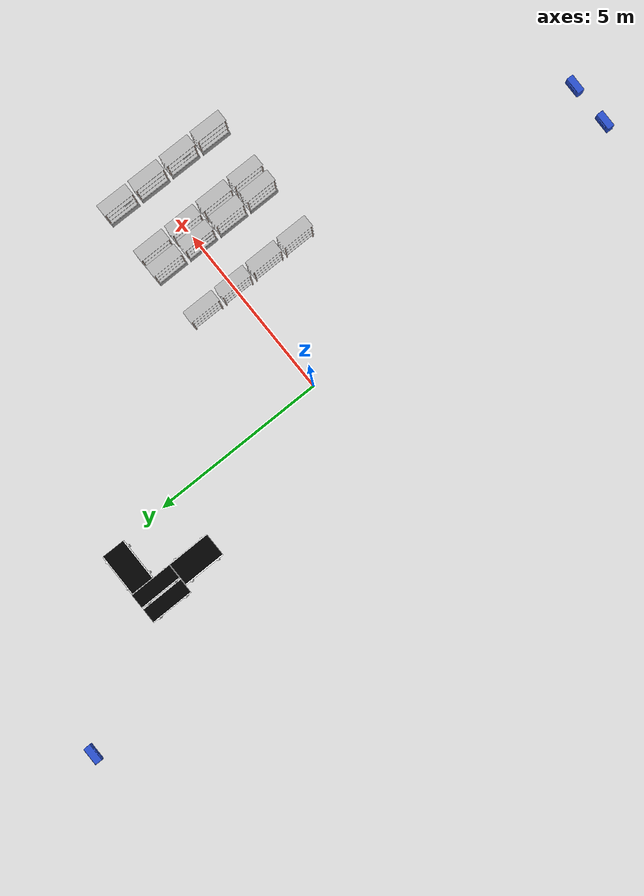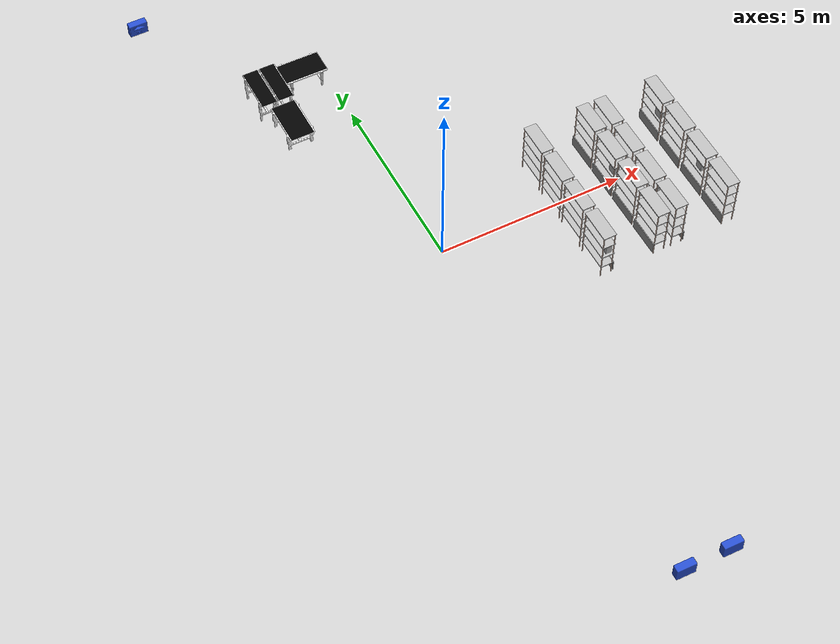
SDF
<sdf version="1.7">
 <world name="default">
  <gravity>0 0 -9.8</gravity>
  <physics name="default_physics" default="0" type="ode">
   <max_step_size>0.001</max_step_size>
   <real_time_factor>1</real_time_factor>
   <real_time_update_rate>1000</real_time_update_rate>
  </physics>
  <magnetic_field>6e-06 2.3e-05 -4.2e-05</magnetic_field>
  <atmosphere type="adiabatic"/>
  <scene><ambient>0.4 0.4 0.4 1</ambient><background>0.7 0.7 0.7 1</background><shadows>1</shadows></scene>
  <audio><device>default</device></audio>
  <spherical_coordinates>
   <surface_model>EARTH_WGS84</surface_model>
   <latitude_deg>0</latitude_deg>
   <longitude_deg>0</longitude_deg>
   <elevation>0</elevation>
   <heading_deg>0</heading_deg>
  </spherical_coordinates>
  <model name="rack">
   <link name="link">
    <inertial>
     <mass>0.1</mass>
     <inertia><ixx>0.01857</ixx><ixy>0</ixy><ixz>0</ixz><iyy>0.015598</iyy><iyz>0</iyz><izz>0.00305</izz></inertia>
    </inertial>
    <visual name="visual1">
     <cast_shadows>0</cast_shadows>
     <geometry><mesh><uri>model://rack/meshes/rack.dae</uri></mesh></geometry>
     <material>
      <shader type="pixel"><normal_map>__default__</normal_map></shader>
      <emissive>0 0 0 1</emissive>
     </material>
    </visual>
    <visual name="visual_2">
     <cast_shadows>0</cast_shadows>
     <geometry><box><size>0.02 0.9 0.31</size></box></geometry>
     <material>
      <lighting>1</lighting>
      <script><uri>file://media/materials/scripts/gazebo.material</uri><name>Gazebo/Grey</name></script>
      <shader type="pixel"><normal_map>__default__</normal_map></shader>
      <ambient>0.3 0.3 0.3 1</ambient>
      <diffuse>0.7 0.7 0.7 1</diffuse>
      <specular>0.01 0.01 0.01 1</specular>
      <emissive>0 0 0 1</emissive>
     </material>
     <pose>-0.185 0 0.22 0 -0 0</pose>
    </visual>
    <collision name="collision_7">
     <pose>0 0 0.36 0 1.57 1.57</pose>
     <geometry><box><size>0.05 0.35 0.91</size></box></geometry>
     <surface>
      <friction>
       <ode><mu>1</mu><mu2>1</mu2><fdir1>0 0 0</fdir1><slip1>0</slip1><slip2>0</slip2></ode>
       <torsional>
        <coefficient>1</coefficient>
        <patch_radius>0</patch_radius>
        <surface_radius>0</surface_radius>
        <use_patch_radius>1</use_patch_radius>
        <ode><slip>0</slip></ode>
       </torsional>
      </friction>
      <bounce><restitution_coefficient>0</restitution_coefficient><threshold>1e+06</threshold></bounce>
      <contact>
       <collide_without_contact>0</collide_without_contact>
       <collide_without_contact_bitmask>1</collide_without_contact_bitmask>
       <collide_bitmask>1</collide_bitmask>
       <ode>
        <soft_cfm>0</soft_cfm>
        <soft_erp>0.2</soft_erp>
        <kp>1e+15</kp>
        <kd>1e+13</kd>
        <max_vel>0.01</max_vel>
        <min_depth>0</min_depth>
       </ode>
       <bullet>
        <split_impulse>1</split_impulse>
        <split_impulse_penetration_threshold>-0.01</split_impulse_penetration_threshold>
        <soft_cfm>0</soft_cfm>
        <soft_erp>0.2</soft_erp>
        <kp>1e+13</kp>
        <kd>1</kd>
       </bullet>
      </contact>
     </surface>
    </collision>
    <collision name="collision_6">
     <pose>0 0 0.725 0 1.57 1.57</pose>
     <geometry><box><size>0.05 0.35 0.91</size></box></geometry>
     <surface>
      <friction>
       <ode><mu>1</mu><mu2>1</mu2><fdir1>0 0 0</fdir1><slip1>0</slip1><slip2>0</slip2></ode>
       <torsional>
        <coefficient>1</coefficient>
        <patch_radius>0</patch_radius>
        <surface_radius>0</surface_radius>
        <use_patch_radius>1</use_patch_radius>
        <ode><slip>0</slip></ode>
       </torsional>
      </friction>
      <bounce><restitution_coefficient>0</restitution_coefficient><threshold>1e+06</threshold></bounce>
      <contact>
       <collide_without_contact>0</collide_without_contact>
       <collide_without_contact_bitmask>1</collide_without_contact_bitmask>
       <collide_bitmask>1</collide_bitmask>
       <ode>
        <soft_cfm>0</soft_cfm>
        <soft_erp>0.2</soft_erp>
        <kp>1e+15</kp>
        <kd>1e+13</kd>
        <max_vel>0.01</max_vel>
        <min_depth>0</min_depth>
       </ode>
       <bullet>
        <split_impulse>1</split_impulse>
        <split_impulse_penetration_threshold>-0.01</split_impulse_penetration_threshold>
        <soft_cfm>0</soft_cfm>
        <soft_erp>0.2</soft_erp>
        <kp>1e+13</kp>
        <kd>1</kd>
       </bullet>
      </contact>
     </surface>
    </collision>
    <collision name="collision_5">
     <pose>0 0 1.09 0 1.57 1.57</pose>
     <geometry><box><size>0.05 0.35 0.91</size></box></geometry>
     <surface>
      <friction>
       <ode><mu>1</mu><mu2>1</mu2><fdir1>0 0 0</fdir1><slip1>0</slip1><slip2>0</slip2></ode>
       <torsional>
        <coefficient>1</coefficient>
        <patch_radius>0</patch_radius>
        <surface_radius>0</surface_radius>
        <use_patch_radius>1</use_patch_radius>
        <ode><slip>0</slip></ode>
       </torsional>
      </friction>
      <bounce><restitution_coefficient>0</restitution_coefficient><threshold>1e+06</threshold></bounce>
      <contact>
       <collide_without_contact>0</collide_without_contact>
       <collide_without_contact_bitmask>1</collide_without_contact_bitmask>
       <collide_bitmask>1</collide_bitmask>
       <ode>
        <soft_cfm>0</soft_cfm>
        <soft_erp>0.2</soft_erp>
        <kp>1e+15</kp>
        <kd>1e+13</kd>
        <max_vel>0.01</max_vel>
        <min_depth>0</min_depth>
       </ode>
       <bullet>
        <split_impulse>1</split_impulse>
        <split_impulse_penetration_threshold>-0.01</split_impulse_penetration_threshold>
        <soft_cfm>0</soft_cfm>
        <soft_erp>0.2</soft_erp>
        <kp>1e+13</kp>
        <kd>1</kd>
       </bullet>
      </contact>
     </surface>
    </collision>
    <collision name="collision_3">
     <pose>0 0 1.455 0 1.57 1.57</pose>
     <geometry><box><size>0.05 0.35 0.91</size></box></geometry>
     <surface>
      <friction>
       <ode><mu>1</mu><mu2>1</mu2><fdir1>0 0 0</fdir1><slip1>0</slip1><slip2>0</slip2></ode>
       <torsional>
        <coefficient>1</coefficient>
        <patch_radius>0</patch_radius>
        <surface_radius>0</surface_radius>
        <use_patch_radius>1</use_patch_radius>
        <ode><slip>0</slip></ode>
       </torsional>
      </friction>
      <bounce><restitution_coefficient>0</restitution_coefficient><threshold>1e+06</threshold></bounce>
      <contact>
       <collide_without_contact>0</collide_without_contact>
       <collide_without_contact_bitmask>1</collide_without_contact_bitmask>
       <collide_bitmask>1</collide_bitmask>
       <ode>
        <soft_cfm>0</soft_cfm>
        <soft_erp>0.2</soft_erp>
        <kp>1e+15</kp>
        <kd>1e+13</kd>
        <max_vel>0.01</max_vel>
        <min_depth>0</min_depth>
       </ode>
       <bullet>
        <split_impulse>1</split_impulse>
        <split_impulse_penetration_threshold>-0.01</split_impulse_penetration_threshold>
        <soft_cfm>0</soft_cfm>
        <soft_erp>0.2</soft_erp>
        <kp>1e+13</kp>
        <kd>1</kd>
       </bullet>
      </contact>
     </surface>
    </collision>
    <collision name="collision_1">
     <pose>0 0.43 0.73 0 -0 1.57</pose>
     <geometry><box><size>0.05 0.36 1.46</size></box></geometry>
     <surface>
      <friction>
       <ode><mu>1</mu><mu2>1</mu2><fdir1>0 0 0</fdir1><slip1>0</slip1><slip2>0</slip2></ode>
       <torsional>
        <coefficient>1</coefficient>
        <patch_radius>0</patch_radius>
        <surface_radius>0</surface_radius>
        <use_patch_radius>1</use_patch_radius>
        <ode><slip>0</slip></ode>
       </torsional>
      </friction>
      <bounce><restitution_coefficient>0</restitution_coefficient><threshold>1e+06</threshold></bounce>
      <contact>
       <collide_without_contact>0</collide_without_contact>
       <collide_without_contact_bitmask>1</collide_without_contact_bitmask>
       <collide_bitmask>1</collide_bitmask>
       <ode>
        <soft_cfm>0</soft_cfm>
        <soft_erp>0.2</soft_erp>
        <kp>1e+15</kp>
        <kd>1e+13</kd>
        <max_vel>0.01</max_vel>
        <min_depth>0</min_depth>
       </ode>
       <bullet>
        <split_impulse>1</split_impulse>
        <split_impulse_penetration_threshold>-0.01</split_impulse_penetration_threshold>
        <soft_cfm>0</soft_cfm>
        <soft_erp>0.2</soft_erp>
        <kp>1e+13</kp>
        <kd>1</kd>
       </bullet>
      </contact>
     </surface>
    </collision>
    <collision name="collision_2">
     <pose>0 -0.43 0.73 0 -0 1.57</pose>
     <geometry><box><size>0.05 0.36 1.46</size></box></geometry>
     <surface>
      <friction>
       <ode><mu>1</mu><mu2>1</mu2><fdir1>0 0 0</fdir1><slip1>0</slip1><slip2>0</slip2></ode>
       <torsional>
        <coefficient>1</coefficient>
        <patch_radius>0</patch_radius>
        <surface_radius>0</surface_radius>
        <use_patch_radius>1</use_patch_radius>
        <ode><slip>0</slip></ode>
       </torsional>
      </friction>
      <bounce><restitution_coefficient>0</restitution_coefficient><threshold>1e+06</threshold></bounce>
      <contact>
       <collide_without_contact>0</collide_without_contact>
       <collide_without_contact_bitmask>1</collide_without_contact_bitmask>
       <collide_bitmask>1</collide_bitmask>
       <ode>
        <soft_cfm>0</soft_cfm>
        <soft_erp>0.2</soft_erp>
        <kp>1e+15</kp>
        <kd>1e+13</kd>
        <max_vel>0.01</max_vel>
        <min_depth>0</min_depth>
       </ode>
       <bullet>
        <split_impulse>1</split_impulse>
        <split_impulse_penetration_threshold>-0.01</split_impulse_penetration_threshold>
        <soft_cfm>0</soft_cfm>
        <soft_erp>0.2</soft_erp>
        <kp>1e+13</kp>
        <kd>1</kd>
       </bullet>
      </contact>
     </surface>
    </collision>
    <collision name="collision">
     <pose>-0.185 0 0.22 0 -0 0</pose>
     <geometry><box><size>0.02 0.9 0.31</size></box></geometry>
     <surface>
      <friction>
       <ode><mu>1</mu><mu2>1</mu2><fdir1>0 0 0</fdir1><slip1>0</slip1><slip2>0</slip2></ode>
       <torsional>
        <coefficient>1</coefficient>
        <patch_radius>0</patch_radius>
        <surface_radius>0</surface_radius>
        <use_patch_radius>1</use_patch_radius>
        <ode><slip>0</slip></ode>
       </torsional>
      </friction>
      <bounce><restitution_coefficient>0</restitution_coefficient><threshold>1e+06</threshold></bounce>
      <contact>
       <collide_without_contact>0</collide_without_contact>
       <collide_without_contact_bitmask>1</collide_without_contact_bitmask>
       <collide_bitmask>1</collide_bitmask>
       <ode>
        <soft_cfm>0</soft_cfm>
        <soft_erp>0.2</soft_erp>
        <kp>1e+15</kp>
        <kd>1e+13</kd>
        <max_vel>0.01</max_vel>
        <min_depth>0</min_depth>
       </ode>
       <bullet>
        <split_impulse>1</split_impulse>
        <split_impulse_penetration_threshold>-0.01</split_impulse_penetration_threshold>
        <soft_cfm>0</soft_cfm>
        <soft_erp>0.2</soft_erp>
        <kp>1e+13</kp>
        <kd>1</kd>
       </bullet>
      </contact>
     </surface>
    </collision>
   </link>
   <static>0</static>
   <pose>6.67799 -1.99962 0.033266 -0.001943 0.000242 -0.010784</pose>
  </model>
  <model name="rack_0">
   <link name="link">
    <inertial>
     <mass>0.1</mass>
     <inertia><ixx>0.01857</ixx><ixy>0</ixy><ixz>0</ixz><iyy>0.015598</iyy><iyz>0</iyz><izz>0.00305</izz></inertia>
    </inertial>
    <visual name="visual1">
     <cast_shadows>0</cast_shadows>
     <geometry><mesh><uri>model://rack/meshes/rack.dae</uri></mesh></geometry>
     <material>
      <shader type="pixel"><normal_map>__default__</normal_map></shader>
      <emissive>0 0 0 1</emissive>
     </material>
    </visual>
    <visual name="visual_2">
     <cast_shadows>0</cast_shadows>
     <geometry><box><size>0.02 0.9 0.31</size></box></geometry>
     <material>
      <lighting>1</lighting>
      <script><uri>file://media/materials/scripts/gazebo.material</uri><name>Gazebo/Grey</name></script>
      <shader type="pixel"><normal_map>__default__</normal_map></shader>
      <ambient>0.3 0.3 0.3 1</ambient>
      <diffuse>0.7 0.7 0.7 1</diffuse>
      <specular>0.01 0.01 0.01 1</specular>
      <emissive>0 0 0 1</emissive>
     </material>
     <pose>-0.185 0 0.22 0 -0 0</pose>
    </visual>
    <collision name="collision_7">
     <pose>0 0 0.36 0 1.57 1.57</pose>
     <geometry><box><size>0.05 0.35 0.91</size></box></geometry>
     <surface>
      <friction>
       <ode><mu>1</mu><mu2>1</mu2><fdir1>0 0 0</fdir1><slip1>0</slip1><slip2>0</slip2></ode>
       <torsional>
        <coefficient>1</coefficient>
        <patch_radius>0</patch_radius>
        <surface_radius>0</surface_radius>
        <use_patch_radius>1</use_patch_radius>
        <ode><slip>0</slip></ode>
       </torsional>
      </friction>
      <bounce><restitution_coefficient>0</restitution_coefficient><threshold>1e+06</threshold></bounce>
      <contact>
       <collide_without_contact>0</collide_without_contact>
       <collide_without_contact_bitmask>1</collide_without_contact_bitmask>
       <collide_bitmask>1</collide_bitmask>
       <ode>
        <soft_cfm>0</soft_cfm>
        <soft_erp>0.2</soft_erp>
        <kp>1e+15</kp>
        <kd>1e+13</kd>
        <max_vel>0.01</max_vel>
        <min_depth>0</min_depth>
       </ode>
       <bullet>
        <split_impulse>1</split_impulse>
        <split_impulse_penetration_threshold>-0.01</split_impulse_penetration_threshold>
        <soft_cfm>0</soft_cfm>
        <soft_erp>0.2</soft_erp>
        <kp>1e+13</kp>
        <kd>1</kd>
       </bullet>
      </contact>
     </surface>
    </collision>
    <collision name="collision_6">
     <pose>0 0 0.725 0 1.57 1.57</pose>
     <geometry><box><size>0.05 0.35 0.91</size></box></geometry>
     <surface>
      <friction>
       <ode><mu>1</mu><mu2>1</mu2><fdir1>0 0 0</fdir1><slip1>0</slip1><slip2>0</slip2></ode>
       <torsional>
        <coefficient>1</coefficient>
        <patch_radius>0</patch_radius>
        <surface_radius>0</surface_radius>
        <use_patch_radius>1</use_patch_radius>
        <ode><slip>0</slip></ode>
       </torsional>
      </friction>
      <bounce><restitution_coefficient>0</restitution_coefficient><threshold>1e+06</threshold></bounce>
      <contact>
       <collide_without_contact>0</collide_without_contact>
       <collide_without_contact_bitmask>1</collide_without_contact_bitmask>
       <collide_bitmask>1</collide_bitmask>
       <ode>
        <soft_cfm>0</soft_cfm>
        <soft_erp>0.2</soft_erp>
        <kp>1e+15</kp>
        <kd>1e+13</kd>
        <max_vel>0.01</max_vel>
        <min_depth>0</min_depth>
       </ode>
       <bullet>
        <split_impulse>1</split_impulse>
        <split_impulse_penetration_threshold>-0.01</split_impulse_penetration_threshold>
        <soft_cfm>0</soft_cfm>
        <soft_erp>0.2</soft_erp>
        <kp>1e+13</kp>
        <kd>1</kd>
       </bullet>
      </contact>
     </surface>
    </collision>
    <collision name="collision_5">
     <pose>0 0 1.09 0 1.57 1.57</pose>
     <geometry><box><size>0.05 0.35 0.91</size></box></geometry>
     <surface>
      <friction>
       <ode><mu>1</mu><mu2>1</mu2><fdir1>0 0 0</fdir1><slip1>0</slip1><slip2>0</slip2></ode>
       <torsional>
        <coefficient>1</coefficient>
        <patch_radius>0</patch_radius>
        <surface_radius>0</surface_radius>
        <use_patch_radius>1</use_patch_radius>
        <ode><slip>0</slip></ode>
       </torsional>
      </friction>
      <bounce><restitution_coefficient>0</restitution_coefficient><threshold>1e+06</threshold></bounce>
      <contact>
       <collide_without_contact>0</collide_without_contact>
       <collide_without_contact_bitmask>1</collide_without_contact_bitmask>
       <collide_bitmask>1</collide_bitmask>
       <ode>
        <soft_cfm>0</soft_cfm>
        <soft_erp>0.2</soft_erp>
        <kp>1e+15</kp>
        <kd>1e+13</kd>
        <max_vel>0.01</max_vel>
        <min_depth>0</min_depth>
       </ode>
       <bullet>
        <split_impulse>1</split_impulse>
        <split_impulse_penetration_threshold>-0.01</split_impulse_penetration_threshold>
        <soft_cfm>0</soft_cfm>
        <soft_erp>0.2</soft_erp>
        <kp>1e+13</kp>
        <kd>1</kd>
       </bullet>
      </contact>
     </surface>
    </collision>
    <collision name="collision_3">
     <pose>0 0 1.455 0 1.57 1.57</pose>
     <geometry><box><size>0.05 0.35 0.91</size></box></geometry>
     <surface>
      <friction>
       <ode><mu>1</mu><mu2>1</mu2><fdir1>0 0 0</fdir1><slip1>0</slip1><slip2>0</slip2></ode>
       <torsional>
        <coefficient>1</coefficient>
        <patch_radius>0</patch_radius>
        <surface_radius>0</surface_radius>
        <use_patch_radius>1</use_patch_radius>
        <ode><slip>0</slip></ode>
       </torsional>
      </friction>
      <bounce><restitution_coefficient>0</restitution_coefficient><threshold>1e+06</threshold></bounce>
      <contact>
       <collide_without_contact>0</collide_without_contact>
       <collide_without_contact_bitmask>1</collide_without_contact_bitmask>
       <collide_bitmask>1</collide_bitmask>
       <ode>
        <soft_cfm>0</soft_cfm>
        <soft_erp>0.2</soft_erp>
        <kp>1e+15</kp>
        <kd>1e+13</kd>
        <max_vel>0.01</max_vel>
        <min_depth>0</min_depth>
       </ode>
       <bullet>
        <split_impulse>1</split_impulse>
        <split_impulse_penetration_threshold>-0.01</split_impulse_penetration_threshold>
        <soft_cfm>0</soft_cfm>
        <soft_erp>0.2</soft_erp>
        <kp>1e+13</kp>
        <kd>1</kd>
       </bullet>
      </contact>
     </surface>
    </collision>
    <collision name="collision_1">
     <pose>0 0.43 0.73 0 -0 1.57</pose>
     <geometry><box><size>0.05 0.36 1.46</size></box></geometry>
     <surface>
      <friction>
       <ode><mu>1</mu><mu2>1</mu2><fdir1>0 0 0</fdir1><slip1>0</slip1><slip2>0</slip2></ode>
       <torsional>
        <coefficient>1</coefficient>
        <patch_radius>0</patch_radius>
        <surface_radius>0</surface_radius>
        <use_patch_radius>1</use_patch_radius>
        <ode><slip>0</slip></ode>
       </torsional>
      </friction>
      <bounce><restitution_coefficient>0</restitution_coefficient><threshold>1e+06</threshold></bounce>
      <contact>
       <collide_without_contact>0</collide_without_contact>
       <collide_without_contact_bitmask>1</collide_without_contact_bitmask>
       <collide_bitmask>1</collide_bitmask>
       <ode>
        <soft_cfm>0</soft_cfm>
        <soft_erp>0.2</soft_erp>
        <kp>1e+15</kp>
        <kd>1e+13</kd>
        <max_vel>0.01</max_vel>
        <min_depth>0</min_depth>
       </ode>
       <bullet>
        <split_impulse>1</split_impulse>
        <split_impulse_penetration_threshold>-0.01</split_impulse_penetration_threshold>
        <soft_cfm>0</soft_cfm>
        <soft_erp>0.2</soft_erp>
        <kp>1e+13</kp>
        <kd>1</kd>
       </bullet>
      </contact>
     </surface>
    </collision>
    <collision name="collision_2">
     <pose>0 -0.43 0.73 0 -0 1.57</pose>
     <geometry><box><size>0.05 0.36 1.46</size></box></geometry>
     <surface>
      <friction>
       <ode><mu>1</mu><mu2>1</mu2><fdir1>0 0 0</fdir1><slip1>0</slip1><slip2>0</slip2></ode>
       <torsional>
        <coefficient>1</coefficient>
        <patch_radius>0</patch_radius>
        <surface_radius>0</surface_radius>
        <use_patch_radius>1</use_patch_radius>
        <ode><slip>0</slip></ode>
       </torsional>
      </friction>
      <bounce><restitution_coefficient>0</restitution_coefficient><threshold>1e+06</threshold></bounce>
      <contact>
       <collide_without_contact>0</collide_without_contact>
       <collide_without_contact_bitmask>1</collide_without_contact_bitmask>
       <collide_bitmask>1</collide_bitmask>
       <ode>
        <soft_cfm>0</soft_cfm>
        <soft_erp>0.2</soft_erp>
        <kp>1e+15</kp>
        <kd>1e+13</kd>
        <max_vel>0.01</max_vel>
        <min_depth>0</min_depth>
       </ode>
       <bullet>
        <split_impulse>1</split_impulse>
        <split_impulse_penetration_threshold>-0.01</split_impulse_penetration_threshold>
        <soft_cfm>0</soft_cfm>
        <soft_erp>0.2</soft_erp>
        <kp>1e+13</kp>
        <kd>1</kd>
       </bullet>
      </contact>
     </surface>
    </collision>
    <collision name="collision">
     <pose>-0.185 0 0.22 0 -0 0</pose>
     <geometry><box><size>0.02 0.9 0.31</size></box></geometry>
     <surface>
      <friction>
       <ode><mu>1</mu><mu2>1</mu2><fdir1>0 0 0</fdir1><slip1>0</slip1><slip2>0</slip2></ode>
       <torsional>
        <coefficient>1</coefficient>
        <patch_radius>0</patch_radius>
        <surface_radius>0</surface_radius>
        <use_patch_radius>1</use_patch_radius>
        <ode><slip>0</slip></ode>
       </torsional>
      </friction>
      <bounce><restitution_coefficient>0</restitution_coefficient><threshold>1e+06</threshold></bounce>
      <contact>
       <collide_without_contact>0</collide_without_contact>
       <collide_without_contact_bitmask>1</collide_without_contact_bitmask>
       <collide_bitmask>1</collide_bitmask>
       <ode>
        <soft_cfm>0</soft_cfm>
        <soft_erp>0.2</soft_erp>
        <kp>1e+15</kp>
        <kd>1e+13</kd>
        <max_vel>0.01</max_vel>
        <min_depth>0</min_depth>
       </ode>
       <bullet>
        <split_impulse>1</split_impulse>
        <split_impulse_penetration_threshold>-0.01</split_impulse_penetration_threshold>
        <soft_cfm>0</soft_cfm>
        <soft_erp>0.2</soft_erp>
        <kp>1e+13</kp>
        <kd>1</kd>
       </bullet>
      </contact>
     </surface>
    </collision>
   </link>
   <static>0</static>
   <pose>6.68734 -0.999831 0.030505 0.000236 -0.004828 -0.004037</pose>
  </model>
  <model name="rack_1">
   <link name="link">
    <inertial>
     <mass>0.1</mass>
     <inertia><ixx>0.01857</ixx><ixy>0</ixy><ixz>0</ixz><iyy>0.015598</iyy><iyz>0</iyz><izz>0.00305</izz></inertia>
    </inertial>
    <visual name="visual1">
     <cast_shadows>0</cast_shadows>
     <geometry><mesh><uri>model://rack/meshes/rack.dae</uri></mesh></geometry>
     <material>
      <shader type="pixel"><normal_map>__default__</normal_map></shader>
      <emissive>0 0 0 1</emissive>
     </material>
    </visual>
    <visual name="visual_2">
     <cast_shadows>0</cast_shadows>
     <geometry><box><size>0.02 0.9 0.31</size></box></geometry>
     <material>
      <lighting>1</lighting>
      <script><uri>file://media/materials/scripts/gazebo.material</uri><name>Gazebo/Grey</name></script>
      <shader type="pixel"><normal_map>__default__</normal_map></shader>
      <ambient>0.3 0.3 0.3 1</ambient>
      <diffuse>0.7 0.7 0.7 1</diffuse>
      <specular>0.01 0.01 0.01 1</specular>
      <emissive>0 0 0 1</emissive>
     </material>
     <pose>-0.185 0 0.22 0 -0 0</pose>
    </visual>
    <collision name="collision_7">
     <pose>0 0 0.36 0 1.57 1.57</pose>
     <geometry><box><size>0.05 0.35 0.91</size></box></geometry>
     <surface>
      <friction>
       <ode><mu>1</mu><mu2>1</mu2><fdir1>0 0 0</fdir1><slip1>0</slip1><slip2>0</slip2></ode>
       <torsional>
        <coefficient>1</coefficient>
        <patch_radius>0</patch_radius>
        <surface_radius>0</surface_radius>
        <use_patch_radius>1</use_patch_radius>
        <ode><slip>0</slip></ode>
       </torsional>
      </friction>
      <bounce><restitution_coefficient>0</restitution_coefficient><threshold>1e+06</threshold></bounce>
      <contact>
       <collide_without_contact>0</collide_without_contact>
       <collide_without_contact_bitmask>1</collide_without_contact_bitmask>
       <collide_bitmask>1</collide_bitmask>
       <ode>
        <soft_cfm>0</soft_cfm>
        <soft_erp>0.2</soft_erp>
        <kp>1e+15</kp>
        <kd>1e+13</kd>
        <max_vel>0.01</max_vel>
        <min_depth>0</min_depth>
       </ode>
       <bullet>
        <split_impulse>1</split_impulse>
        <split_impulse_penetration_threshold>-0.01</split_impulse_penetration_threshold>
        <soft_cfm>0</soft_cfm>
        <soft_erp>0.2</soft_erp>
        <kp>1e+13</kp>
        <kd>1</kd>
       </bullet>
      </contact>
     </surface>
    </collision>
    <collision name="collision_6">
     <pose>0 0 0.725 0 1.57 1.57</pose>
     <geometry><box><size>0.05 0.35 0.91</size></box></geometry>
     <surface>
      <friction>
       <ode><mu>1</mu><mu2>1</mu2><fdir1>0 0 0</fdir1><slip1>0</slip1><slip2>0</slip2></ode>
       <torsional>
        <coefficient>1</coefficient>
        <patch_radius>0</patch_radius>
        <surface_radius>0</surface_radius>
        <use_patch_radius>1</use_patch_radius>
        <ode><slip>0</slip></ode>
       </torsional>
      </friction>
      <bounce><restitution_coefficient>0</restitution_coefficient><threshold>1e+06</threshold></bounce>
      <contact>
       <collide_without_contact>0</collide_without_contact>
       <collide_without_contact_bitmask>1</collide_without_contact_bitmask>
       <collide_bitmask>1</collide_bitmask>
       <ode>
        <soft_cfm>0</soft_cfm>
        <soft_erp>0.2</soft_erp>
        <kp>1e+15</kp>
        <kd>1e+13</kd>
        <max_vel>0.01</max_vel>
        <min_depth>0</min_depth>
       </ode>
       <bullet>
        <split_impulse>1</split_impulse>
        <split_impulse_penetration_threshold>-0.01</split_impulse_penetration_threshold>
        <soft_cfm>0</soft_cfm>
        <soft_erp>0.2</soft_erp>
        <kp>1e+13</kp>
        <kd>1</kd>
       </bullet>
      </contact>
     </surface>
    </collision>
    <collision name="collision_5">
     <pose>0 0 1.09 0 1.57 1.57</pose>
     <geometry><box><size>0.05 0.35 0.91</size></box></geometry>
     <surface>
      <friction>
       <ode><mu>1</mu><mu2>1</mu2><fdir1>0 0 0</fdir1><slip1>0</slip1><slip2>0</slip2></ode>
       <torsional>
        <coefficient>1</coefficient>
        <patch_radius>0</patch_radius>
        <surface_radius>0</surface_radius>
        <use_patch_radius>1</use_patch_radius>
        <ode><slip>0</slip></ode>
       </torsional>
      </friction>
      <bounce><restitution_coefficient>0</restitution_coefficient><threshold>1e+06</threshold></bounce>
      <contact>
       <collide_without_contact>0</collide_without_contact>
       <collide_without_contact_bitmask>1</collide_without_contact_bitmask>
       <collide_bitmask>1</collide_bitmask>
       <ode>
        <soft_cfm>0</soft_cfm>
        <soft_erp>0.2</soft_erp>
        <kp>1e+15</kp>
        <kd>1e+13</kd>
        <max_vel>0.01</max_vel>
        <min_depth>0</min_depth>
       </ode>
       <bullet>
        <split_impulse>1</split_impulse>
        <split_impulse_penetration_threshold>-0.01</split_impulse_penetration_threshold>
        <soft_cfm>0</soft_cfm>
        <soft_erp>0.2</soft_erp>
        <kp>1e+13</kp>
        <kd>1</kd>
       </bullet>
      </contact>
     </surface>
    </collision>
    <collision name="collision_3">
     <pose>0 0 1.455 0 1.57 1.57</pose>
     <geometry><box><size>0.05 0.35 0.91</size></box></geometry>
     <surface>
      <friction>
       <ode><mu>1</mu><mu2>1</mu2><fdir1>0 0 0</fdir1><slip1>0</slip1><slip2>0</slip2></ode>
       <torsional>
        <coefficient>1</coefficient>
        <patch_radius>0</patch_radius>
        <surface_radius>0</surface_radius>
        <use_patch_radius>1</use_patch_radius>
        <ode><slip>0</slip></ode>
       </torsional>
      </friction>
      <bounce><restitution_coefficient>0</restitution_coefficient><threshold>1e+06</threshold></bounce>
      <contact>
       <collide_without_contact>0</collide_without_contact>
       <collide_without_contact_bitmask>1</collide_without_contact_bitmask>
       <collide_bitmask>1</collide_bitmask>
       <ode>
        <soft_cfm>0</soft_cfm>
        <soft_erp>0.2</soft_erp>
        <kp>1e+15</kp>
        <kd>1e+13</kd>
        <max_vel>0.01</max_vel>
        <min_depth>0</min_depth>
       </ode>
       <bullet>
        <split_impulse>1</split_impulse>
        <split_impulse_penetration_threshold>-0.01</split_impulse_penetration_threshold>
        <soft_cfm>0</soft_cfm>
        <soft_erp>0.2</soft_erp>
        <kp>1e+13</kp>
        <kd>1</kd>
       </bullet>
      </contact>
     </surface>
    </collision>
    <collision name="collision_1">
     <pose>0 0.43 0.73 0 -0 1.57</pose>
     <geometry><box><size>0.05 0.36 1.46</size></box></geometry>
     <surface>
      <friction>
       <ode><mu>1</mu><mu2>1</mu2><fdir1>0 0 0</fdir1><slip1>0</slip1><slip2>0</slip2></ode>
       <torsional>
        <coefficient>1</coefficient>
        <patch_radius>0</patch_radius>
        <surface_radius>0</surface_radius>
        <use_patch_radius>1</use_patch_radius>
        <ode><slip>0</slip></ode>
       </torsional>
      </friction>
      <bounce><restitution_coefficient>0</restitution_coefficient><threshold>1e+06</threshold></bounce>
      <contact>
       <collide_without_contact>0</collide_without_contact>
       <collide_without_contact_bitmask>1</collide_without_contact_bitmask>
       <collide_bitmask>1</collide_bitmask>
       <ode>
        <soft_cfm>0</soft_cfm>
        <soft_erp>0.2</soft_erp>
        <kp>1e+15</kp>
        <kd>1e+13</kd>
        <max_vel>0.01</max_vel>
        <min_depth>0</min_depth>
       </ode>
       <bullet>
        <split_impulse>1</split_impulse>
        <split_impulse_penetration_threshold>-0.01</split_impulse_penetration_threshold>
        <soft_cfm>0</soft_cfm>
        <soft_erp>0.2</soft_erp>
        <kp>1e+13</kp>
        <kd>1</kd>
       </bullet>
      </contact>
     </surface>
    </collision>
    <collision name="collision_2">
     <pose>0 -0.43 0.73 0 -0 1.57</pose>
     <geometry><box><size>0.05 0.36 1.46</size></box></geometry>
     <surface>
      <friction>
       <ode><mu>1</mu><mu2>1</mu2><fdir1>0 0 0</fdir1><slip1>0</slip1><slip2>0</slip2></ode>
       <torsional>
        <coefficient>1</coefficient>
        <patch_radius>0</patch_radius>
        <surface_radius>0</surface_radius>
        <use_patch_radius>1</use_patch_radius>
        <ode><slip>0</slip></ode>
       </torsional>
      </friction>
      <bounce><restitution_coefficient>0</restitution_coefficient><threshold>1e+06</threshold></bounce>
      <contact>
       <collide_without_contact>0</collide_without_contact>
       <collide_without_contact_bitmask>1</collide_without_contact_bitmask>
       <collide_bitmask>1</collide_bitmask>
       <ode>
        <soft_cfm>0</soft_cfm>
        <soft_erp>0.2</soft_erp>
        <kp>1e+15</kp>
        <kd>1e+13</kd>
        <max_vel>0.01</max_vel>
        <min_depth>0</min_depth>
       </ode>
       <bullet>
        <split_impulse>1</split_impulse>
        <split_impulse_penetration_threshold>-0.01</split_impulse_penetration_threshold>
        <soft_cfm>0</soft_cfm>
        <soft_erp>0.2</soft_erp>
        <kp>1e+13</kp>
        <kd>1</kd>
       </bullet>
      </contact>
     </surface>
    </collision>
    <collision name="collision">
     <pose>-0.185 0 0.22 0 -0 0</pose>
     <geometry><box><size>0.02 0.9 0.31</size></box></geometry>
     <surface>
      <friction>
       <ode><mu>1</mu><mu2>1</mu2><fdir1>0 0 0</fdir1><slip1>0</slip1><slip2>0</slip2></ode>
       <torsional>
        <coefficient>1</coefficient>
        <patch_radius>0</patch_radius>
        <surface_radius>0</surface_radius>
        <use_patch_radius>1</use_patch_radius>
        <ode><slip>0</slip></ode>
       </torsional>
      </friction>
      <bounce><restitution_coefficient>0</restitution_coefficient><threshold>1e+06</threshold></bounce>
      <contact>
       <collide_without_contact>0</collide_without_contact>
       <collide_without_contact_bitmask>1</collide_without_contact_bitmask>
       <collide_bitmask>1</collide_bitmask>
       <ode>
        <soft_cfm>0</soft_cfm>
        <soft_erp>0.2</soft_erp>
        <kp>1e+15</kp>
        <kd>1e+13</kd>
        <max_vel>0.01</max_vel>
        <min_depth>0</min_depth>
       </ode>
       <bullet>
        <split_impulse>1</split_impulse>
        <split_impulse_penetration_threshold>-0.01</split_impulse_penetration_threshold>
        <soft_cfm>0</soft_cfm>
        <soft_erp>0.2</soft_erp>
        <kp>1e+13</kp>
        <kd>1</kd>
       </bullet>
      </contact>
     </surface>
    </collision>
   </link>
   <static>0</static>
   <pose>6.67854 0.000375 0.033152 -0.001732 0.000288 -0.010437</pose>
  </model>
  <model name="rack_2">
   <link name="link">
    <inertial>
     <mass>0.1</mass>
     <inertia><ixx>0.01857</ixx><ixy>0</ixy><ixz>0</ixz><iyy>0.015598</iyy><iyz>0</iyz><izz>0.00305</izz></inertia>
    </inertial>
    <visual name="visual1">
     <cast_shadows>0</cast_shadows>
     <geometry><mesh><uri>model://rack/meshes/rack.dae</uri></mesh></geometry>
     <material>
      <shader type="pixel"><normal_map>__default__</normal_map></shader>
      <emissive>0 0 0 1</emissive>
     </material>
    </visual>
    <visual name="visual_2">
     <cast_shadows>0</cast_shadows>
     <geometry><box><size>0.02 0.9 0.31</size></box></geometry>
     <material>
      <lighting>1</lighting>
      <script><uri>file://media/materials/scripts/gazebo.material</uri><name>Gazebo/Grey</name></script>
      <shader type="pixel"><normal_map>__default__</normal_map></shader>
      <ambient>0.3 0.3 0.3 1</ambient>
      <diffuse>0.7 0.7 0.7 1</diffuse>
      <specular>0.01 0.01 0.01 1</specular>
      <emissive>0 0 0 1</emissive>
     </material>
     <pose>-0.185 0 0.22 0 -0 0</pose>
    </visual>
    <collision name="collision_7">
     <pose>0 0 0.36 0 1.57 1.57</pose>
     <geometry><box><size>0.05 0.35 0.91</size></box></geometry>
     <surface>
      <friction>
       <ode><mu>1</mu><mu2>1</mu2><fdir1>0 0 0</fdir1><slip1>0</slip1><slip2>0</slip2></ode>
       <torsional>
        <coefficient>1</coefficient>
        <patch_radius>0</patch_radius>
        <surface_radius>0</surface_radius>
        <use_patch_radius>1</use_patch_radius>
        <ode><slip>0</slip></ode>
       </torsional>
      </friction>
      <bounce><restitution_coefficient>0</restitution_coefficient><threshold>1e+06</threshold></bounce>
      <contact>
       <collide_without_contact>0</collide_without_contact>
       <collide_without_contact_bitmask>1</collide_without_contact_bitmask>
       <collide_bitmask>1</collide_bitmask>
       <ode>
        <soft_cfm>0</soft_cfm>
        <soft_erp>0.2</soft_erp>
        <kp>1e+15</kp>
        <kd>1e+13</kd>
        <max_vel>0.01</max_vel>
        <min_depth>0</min_depth>
       </ode>
       <bullet>
        <split_impulse>1</split_impulse>
        <split_impulse_penetration_threshold>-0.01</split_impulse_penetration_threshold>
        <soft_cfm>0</soft_cfm>
        <soft_erp>0.2</soft_erp>
        <kp>1e+13</kp>
        <kd>1</kd>
       </bullet>
      </contact>
     </surface>
    </collision>
    <collision name="collision_6">
     <pose>0 0 0.725 0 1.57 1.57</pose>
     <geometry><box><size>0.05 0.35 0.91</size></box></geometry>
     <surface>
      <friction>
       <ode><mu>1</mu><mu2>1</mu2><fdir1>0 0 0</fdir1><slip1>0</slip1><slip2>0</slip2></ode>
       <torsional>
        <coefficient>1</coefficient>
        <patch_radius>0</patch_radius>
        <surface_radius>0</surface_radius>
        <use_patch_radius>1</use_patch_radius>
        <ode><slip>0</slip></ode>
       </torsional>
      </friction>
      <bounce><restitution_coefficient>0</restitution_coefficient><threshold>1e+06</threshold></bounce>
      <contact>
       <collide_without_contact>0</collide_without_contact>
       <collide_without_contact_bitmask>1</collide_without_contact_bitmask>
       <collide_bitmask>1</collide_bitmask>
       <ode>
        <soft_cfm>0</soft_cfm>
        <soft_erp>0.2</soft_erp>
        <kp>1e+15</kp>
        <kd>1e+13</kd>
        <max_vel>0.01</max_vel>
        <min_depth>0</min_depth>
       </ode>
       <bullet>
        <split_impulse>1</split_impulse>
        <split_impulse_penetration_threshold>-0.01</split_impulse_penetration_threshold>
        <soft_cfm>0</soft_cfm>
        <soft_erp>0.2</soft_erp>
        <kp>1e+13</kp>
        <kd>1</kd>
       </bullet>
      </contact>
     </surface>
    </collision>
    <collision name="collision_5">
     <pose>0 0 1.09 0 1.57 1.57</pose>
     <geometry><box><size>0.05 0.35 0.91</size></box></geometry>
     <surface>
      <friction>
       <ode><mu>1</mu><mu2>1</mu2><fdir1>0 0 0</fdir1><slip1>0</slip1><slip2>0</slip2></ode>
       <torsional>
        <coefficient>1</coefficient>
        <patch_radius>0</patch_radius>
        <surface_radius>0</surface_radius>
        <use_patch_radius>1</use_patch_radius>
        <ode><slip>0</slip></ode>
       </torsional>
      </friction>
      <bounce><restitution_coefficient>0</restitution_coefficient><threshold>1e+06</threshold></bounce>
      <contact>
       <collide_without_contact>0</collide_without_contact>
       <collide_without_contact_bitmask>1</collide_without_contact_bitmask>
       <collide_bitmask>1</collide_bitmask>
       <ode>
        <soft_cfm>0</soft_cfm>
        <soft_erp>0.2</soft_erp>
        <kp>1e+15</kp>
        <kd>1e+13</kd>
        <max_vel>0.01</max_vel>
        <min_depth>0</min_depth>
       </ode>
       <bullet>
        <split_impulse>1</split_impulse>
        <split_impulse_penetration_threshold>-0.01</split_impulse_penetration_threshold>
        <soft_cfm>0</soft_cfm>
        <soft_erp>0.2</soft_erp>
        <kp>1e+13</kp>
        <kd>1</kd>
       </bullet>
      </contact>
     </surface>
    </collision>
    <collision name="collision_3">
     <pose>0 0 1.455 0 1.57 1.57</pose>
     <geometry><box><size>0.05 0.35 0.91</size></box></geometry>
     <surface>
      <friction>
       <ode><mu>1</mu><mu2>1</mu2><fdir1>0 0 0</fdir1><slip1>0</slip1><slip2>0</slip2></ode>
       <torsional>
        <coefficient>1</coefficient>
        <patch_radius>0</patch_radius>
        <surface_radius>0</surface_radius>
        <use_patch_radius>1</use_patch_radius>
        <ode><slip>0</slip></ode>
       </torsional>
      </friction>
      <bounce><restitution_coefficient>0</restitution_coefficient><threshold>1e+06</threshold></bounce>
      <contact>
       <collide_without_contact>0</collide_without_contact>
       <collide_without_contact_bitmask>1</collide_without_contact_bitmask>
       <collide_bitmask>1</collide_bitmask>
       <ode>
        <soft_cfm>0</soft_cfm>
        <soft_erp>0.2</soft_erp>
        <kp>1e+15</kp>
        <kd>1e+13</kd>
        <max_vel>0.01</max_vel>
        <min_depth>0</min_depth>
       </ode>
       <bullet>
        <split_impulse>1</split_impulse>
        <split_impulse_penetration_threshold>-0.01</split_impulse_penetration_threshold>
        <soft_cfm>0</soft_cfm>
        <soft_erp>0.2</soft_erp>
        <kp>1e+13</kp>
        <kd>1</kd>
       </bullet>
      </contact>
     </surface>
    </collision>
    <collision name="collision_1">
     <pose>0 0.43 0.73 0 -0 1.57</pose>
     <geometry><box><size>0.05 0.36 1.46</size></box></geometry>
     <surface>
      <friction>
       <ode><mu>1</mu><mu2>1</mu2><fdir1>0 0 0</fdir1><slip1>0</slip1><slip2>0</slip2></ode>
       <torsional>
        <coefficient>1</coefficient>
        <patch_radius>0</patch_radius>
        <surface_radius>0</surface_radius>
        <use_patch_radius>1</use_patch_radius>
        <ode><slip>0</slip></ode>
       </torsional>
      </friction>
      <bounce><restitution_coefficient>0</restitution_coefficient><threshold>1e+06</threshold></bounce>
      <contact>
       <collide_without_contact>0</collide_without_contact>
       <collide_without_contact_bitmask>1</collide_without_contact_bitmask>
       <collide_bitmask>1</collide_bitmask>
       <ode>
        <soft_cfm>0</soft_cfm>
        <soft_erp>0.2</soft_erp>
        <kp>1e+15</kp>
        <kd>1e+13</kd>
        <max_vel>0.01</max_vel>
        <min_depth>0</min_depth>
       </ode>
       <bullet>
        <split_impulse>1</split_impulse>
        <split_impulse_penetration_threshold>-0.01</split_impulse_penetration_threshold>
        <soft_cfm>0</soft_cfm>
        <soft_erp>0.2</soft_erp>
        <kp>1e+13</kp>
        <kd>1</kd>
       </bullet>
      </contact>
     </surface>
    </collision>
    <collision name="collision_2">
     <pose>0 -0.43 0.73 0 -0 1.57</pose>
     <geometry><box><size>0.05 0.36 1.46</size></box></geometry>
     <surface>
      <friction>
       <ode><mu>1</mu><mu2>1</mu2><fdir1>0 0 0</fdir1><slip1>0</slip1><slip2>0</slip2></ode>
       <torsional>
        <coefficient>1</coefficient>
        <patch_radius>0</patch_radius>
        <surface_radius>0</surface_radius>
        <use_patch_radius>1</use_patch_radius>
        <ode><slip>0</slip></ode>
       </torsional>
      </friction>
      <bounce><restitution_coefficient>0</restitution_coefficient><threshold>1e+06</threshold></bounce>
      <contact>
       <collide_without_contact>0</collide_without_contact>
       <collide_without_contact_bitmask>1</collide_without_contact_bitmask>
       <collide_bitmask>1</collide_bitmask>
       <ode>
        <soft_cfm>0</soft_cfm>
        <soft_erp>0.2</soft_erp>
        <kp>1e+15</kp>
        <kd>1e+13</kd>
        <max_vel>0.01</max_vel>
        <min_depth>0</min_depth>
       </ode>
       <bullet>
        <split_impulse>1</split_impulse>
        <split_impulse_penetration_threshold>-0.01</split_impulse_penetration_threshold>
        <soft_cfm>0</soft_cfm>
        <soft_erp>0.2</soft_erp>
        <kp>1e+13</kp>
        <kd>1</kd>
       </bullet>
      </contact>
     </surface>
    </collision>
    <collision name="collision">
     <pose>-0.185 0 0.22 0 -0 0</pose>
     <geometry><box><size>0.02 0.9 0.31</size></box></geometry>
     <surface>
      <friction>
       <ode><mu>1</mu><mu2>1</mu2><fdir1>0 0 0</fdir1><slip1>0</slip1><slip2>0</slip2></ode>
       <torsional>
        <coefficient>1</coefficient>
        <patch_radius>0</patch_radius>
        <surface_radius>0</surface_radius>
        <use_patch_radius>1</use_patch_radius>
        <ode><slip>0</slip></ode>
       </torsional>
      </friction>
      <bounce><restitution_coefficient>0</restitution_coefficient><threshold>1e+06</threshold></bounce>
      <contact>
       <collide_without_contact>0</collide_without_contact>
       <collide_without_contact_bitmask>1</collide_without_contact_bitmask>
       <collide_bitmask>1</collide_bitmask>
       <ode>
        <soft_cfm>0</soft_cfm>
        <soft_erp>0.2</soft_erp>
        <kp>1e+15</kp>
        <kd>1e+13</kd>
        <max_vel>0.01</max_vel>
        <min_depth>0</min_depth>
       </ode>
       <bullet>
        <split_impulse>1</split_impulse>
        <split_impulse_penetration_threshold>-0.01</split_impulse_penetration_threshold>
        <soft_cfm>0</soft_cfm>
        <soft_erp>0.2</soft_erp>
        <kp>1e+13</kp>
        <kd>1</kd>
       </bullet>
      </contact>
     </surface>
    </collision>
   </link>
   <static>0</static>
   <pose>6.67853 1.00037 0.032986 -0.001626 -0.000937 -0.010437</pose>
  </model>
  <model name="rack_3">
   <link name="link">
    <inertial>
     <mass>0.1</mass>
     <inertia><ixx>0.01857</ixx><ixy>0</ixy><ixz>0</ixz><iyy>0.015598</iyy><iyz>0</iyz><izz>0.00305</izz></inertia>
    </inertial>
    <visual name="visual1">
     <cast_shadows>0</cast_shadows>
     <geometry><mesh><uri>model://rack/meshes/rack.dae</uri></mesh></geometry>
     <material>
      <shader type="pixel"><normal_map>__default__</normal_map></shader>
      <emissive>0 0 0 1</emissive>
     </material>
    </visual>
    <visual name="visual_2">
     <cast_shadows>0</cast_shadows>
     <geometry><box><size>0.02 0.9 0.31</size></box></geometry>
     <material>
      <lighting>1</lighting>
      <script><uri>file://media/materials/scripts/gazebo.material</uri><name>Gazebo/Grey</name></script>
      <shader type="pixel"><normal_map>__default__</normal_map></shader>
      <ambient>0.3 0.3 0.3 1</ambient>
      <diffuse>0.7 0.7 0.7 1</diffuse>
      <specular>0.01 0.01 0.01 1</specular>
      <emissive>0 0 0 1</emissive>
     </material>
     <pose>-0.185 0 0.22 0 -0 0</pose>
    </visual>
    <collision name="collision_7">
     <pose>0 0 0.36 0 1.57 1.57</pose>
     <geometry><box><size>0.05 0.35 0.91</size></box></geometry>
     <surface>
      <friction>
       <ode><mu>1</mu><mu2>1</mu2><fdir1>0 0 0</fdir1><slip1>0</slip1><slip2>0</slip2></ode>
       <torsional>
        <coefficient>1</coefficient>
        <patch_radius>0</patch_radius>
        <surface_radius>0</surface_radius>
        <use_patch_radius>1</use_patch_radius>
        <ode><slip>0</slip></ode>
       </torsional>
      </friction>
      <bounce><restitution_coefficient>0</restitution_coefficient><threshold>1e+06</threshold></bounce>
      <contact>
       <collide_without_contact>0</collide_without_contact>
       <collide_without_contact_bitmask>1</collide_without_contact_bitmask>
       <collide_bitmask>1</collide_bitmask>
       <ode>
        <soft_cfm>0</soft_cfm>
        <soft_erp>0.2</soft_erp>
        <kp>1e+15</kp>
        <kd>1e+13</kd>
        <max_vel>0.01</max_vel>
        <min_depth>0</min_depth>
       </ode>
       <bullet>
        <split_impulse>1</split_impulse>
        <split_impulse_penetration_threshold>-0.01</split_impulse_penetration_threshold>
        <soft_cfm>0</soft_cfm>
        <soft_erp>0.2</soft_erp>
        <kp>1e+13</kp>
        <kd>1</kd>
       </bullet>
      </contact>
     </surface>
    </collision>
    <collision name="collision_6">
     <pose>0 0 0.725 0 1.57 1.57</pose>
     <geometry><box><size>0.05 0.35 0.91</size></box></geometry>
     <surface>
      <friction>
       <ode><mu>1</mu><mu2>1</mu2><fdir1>0 0 0</fdir1><slip1>0</slip1><slip2>0</slip2></ode>
       <torsional>
        <coefficient>1</coefficient>
        <patch_radius>0</patch_radius>
        <surface_radius>0</surface_radius>
        <use_patch_radius>1</use_patch_radius>
        <ode><slip>0</slip></ode>
       </torsional>
      </friction>
      <bounce><restitution_coefficient>0</restitution_coefficient><threshold>1e+06</threshold></bounce>
      <contact>
       <collide_without_contact>0</collide_without_contact>
       <collide_without_contact_bitmask>1</collide_without_contact_bitmask>
       <collide_bitmask>1</collide_bitmask>
       <ode>
        <soft_cfm>0</soft_cfm>
        <soft_erp>0.2</soft_erp>
        <kp>1e+15</kp>
        <kd>1e+13</kd>
        <max_vel>0.01</max_vel>
        <min_depth>0</min_depth>
       </ode>
       <bullet>
        <split_impulse>1</split_impulse>
        <split_impulse_penetration_threshold>-0.01</split_impulse_penetration_threshold>
        <soft_cfm>0</soft_cfm>
        <soft_erp>0.2</soft_erp>
        <kp>1e+13</kp>
        <kd>1</kd>
       </bullet>
      </contact>
     </surface>
    </collision>
    <collision name="collision_5">
     <pose>0 0 1.09 0 1.57 1.57</pose>
     <geometry><box><size>0.05 0.35 0.91</size></box></geometry>
     <surface>
      <friction>
       <ode><mu>1</mu><mu2>1</mu2><fdir1>0 0 0</fdir1><slip1>0</slip1><slip2>0</slip2></ode>
       <torsional>
        <coefficient>1</coefficient>
        <patch_radius>0</patch_radius>
        <surface_radius>0</surface_radius>
        <use_patch_radius>1</use_patch_radius>
        <ode><slip>0</slip></ode>
       </torsional>
      </friction>
      <bounce><restitution_coefficient>0</restitution_coefficient><threshold>1e+06</threshold></bounce>
      <contact>
       <collide_without_contact>0</collide_without_contact>
       <collide_without_contact_bitmask>1</collide_without_contact_bitmask>
       <collide_bitmask>1</collide_bitmask>
       <ode>
        <soft_cfm>0</soft_cfm>
        <soft_erp>0.2</soft_erp>
        <kp>1e+15</kp>
        <kd>1e+13</kd>
        <max_vel>0.01</max_vel>
        <min_depth>0</min_depth>
       </ode>
       <bullet>
        <split_impulse>1</split_impulse>
        <split_impulse_penetration_threshold>-0.01</split_impulse_penetration_threshold>
        <soft_cfm>0</soft_cfm>
        <soft_erp>0.2</soft_erp>
        <kp>1e+13</kp>
        <kd>1</kd>
       </bullet>
      </contact>
     </surface>
    </collision>
    <collision name="collision_3">
     <pose>0 0 1.455 0 1.57 1.57</pose>
     <geometry><box><size>0.05 0.35 0.91</size></box></geometry>
     <surface>
      <friction>
       <ode><mu>1</mu><mu2>1</mu2><fdir1>0 0 0</fdir1><slip1>0</slip1><slip2>0</slip2></ode>
       <torsional>
        <coefficient>1</coefficient>
        <patch_radius>0</patch_radius>
        <surface_radius>0</surface_radius>
        <use_patch_radius>1</use_patch_radius>
        <ode><slip>0</slip></ode>
       </torsional>
      </friction>
      <bounce><restitution_coefficient>0</restitution_coefficient><threshold>1e+06</threshold></bounce>
      <contact>
       <collide_without_contact>0</collide_without_contact>
       <collide_without_contact_bitmask>1</collide_without_contact_bitmask>
       <collide_bitmask>1</collide_bitmask>
       <ode>
        <soft_cfm>0</soft_cfm>
        <soft_erp>0.2</soft_erp>
        <kp>1e+15</kp>
        <kd>1e+13</kd>
        <max_vel>0.01</max_vel>
        <min_depth>0</min_depth>
       </ode>
       <bullet>
        <split_impulse>1</split_impulse>
        <split_impulse_penetration_threshold>-0.01</split_impulse_penetration_threshold>
        <soft_cfm>0</soft_cfm>
        <soft_erp>0.2</soft_erp>
        <kp>1e+13</kp>
        <kd>1</kd>
       </bullet>
      </contact>
     </surface>
    </collision>
    <collision name="collision_1">
     <pose>0 0.43 0.73 0 -0 1.57</pose>
     <geometry><box><size>0.05 0.36 1.46</size></box></geometry>
     <surface>
      <friction>
       <ode><mu>1</mu><mu2>1</mu2><fdir1>0 0 0</fdir1><slip1>0</slip1><slip2>0</slip2></ode>
       <torsional>
        <coefficient>1</coefficient>
        <patch_radius>0</patch_radius>
        <surface_radius>0</surface_radius>
        <use_patch_radius>1</use_patch_radius>
        <ode><slip>0</slip></ode>
       </torsional>
      </friction>
      <bounce><restitution_coefficient>0</restitution_coefficient><threshold>1e+06</threshold></bounce>
      <contact>
       <collide_without_contact>0</collide_without_contact>
       <collide_without_contact_bitmask>1</collide_without_contact_bitmask>
       <collide_bitmask>1</collide_bitmask>
       <ode>
        <soft_cfm>0</soft_cfm>
        <soft_erp>0.2</soft_erp>
        <kp>1e+15</kp>
        <kd>1e+13</kd>
        <max_vel>0.01</max_vel>
        <min_depth>0</min_depth>
       </ode>
       <bullet>
        <split_impulse>1</split_impulse>
        <split_impulse_penetration_threshold>-0.01</split_impulse_penetration_threshold>
        <soft_cfm>0</soft_cfm>
        <soft_erp>0.2</soft_erp>
        <kp>1e+13</kp>
        <kd>1</kd>
       </bullet>
      </contact>
     </surface>
    </collision>
    <collision name="collision_2">
     <pose>0 -0.43 0.73 0 -0 1.57</pose>
     <geometry><box><size>0.05 0.36 1.46</size></box></geometry>
     <surface>
      <friction>
       <ode><mu>1</mu><mu2>1</mu2><fdir1>0 0 0</fdir1><slip1>0</slip1><slip2>0</slip2></ode>
       <torsional>
        <coefficient>1</coefficient>
        <patch_radius>0</patch_radius>
        <surface_radius>0</surface_radius>
        <use_patch_radius>1</use_patch_radius>
        <ode><slip>0</slip></ode>
       </torsional>
      </friction>
      <bounce><restitution_coefficient>0</restitution_coefficient><threshold>1e+06</threshold></bounce>
      <contact>
       <collide_without_contact>0</collide_without_contact>
       <collide_without_contact_bitmask>1</collide_without_contact_bitmask>
       <collide_bitmask>1</collide_bitmask>
       <ode>
        <soft_cfm>0</soft_cfm>
        <soft_erp>0.2</soft_erp>
        <kp>1e+15</kp>
        <kd>1e+13</kd>
        <max_vel>0.01</max_vel>
        <min_depth>0</min_depth>
       </ode>
       <bullet>
        <split_impulse>1</split_impulse>
        <split_impulse_penetration_threshold>-0.01</split_impulse_penetration_threshold>
        <soft_cfm>0</soft_cfm>
        <soft_erp>0.2</soft_erp>
        <kp>1e+13</kp>
        <kd>1</kd>
       </bullet>
      </contact>
     </surface>
    </collision>
    <collision name="collision">
     <pose>-0.185 0 0.22 0 -0 0</pose>
     <geometry><box><size>0.02 0.9 0.31</size></box></geometry>
     <surface>
      <friction>
       <ode><mu>1</mu><mu2>1</mu2><fdir1>0 0 0</fdir1><slip1>0</slip1><slip2>0</slip2></ode>
       <torsional>
        <coefficient>1</coefficient>
        <patch_radius>0</patch_radius>
        <surface_radius>0</surface_radius>
        <use_patch_radius>1</use_patch_radius>
        <ode><slip>0</slip></ode>
       </torsional>
      </friction>
      <bounce><restitution_coefficient>0</restitution_coefficient><threshold>1e+06</threshold></bounce>
      <contact>
       <collide_without_contact>0</collide_without_contact>
       <collide_without_contact_bitmask>1</collide_without_contact_bitmask>
       <collide_bitmask>1</collide_bitmask>
       <ode>
        <soft_cfm>0</soft_cfm>
        <soft_erp>0.2</soft_erp>
        <kp>1e+15</kp>
        <kd>1e+13</kd>
        <max_vel>0.01</max_vel>
        <min_depth>0</min_depth>
       </ode>
       <bullet>
        <split_impulse>1</split_impulse>
        <split_impulse_penetration_threshold>-0.01</split_impulse_penetration_threshold>
        <soft_cfm>0</soft_cfm>
        <soft_erp>0.2</soft_erp>
        <kp>1e+13</kp>
        <kd>1</kd>
       </bullet>
      </contact>
     </surface>
    </collision>
   </link>
   <static>0</static>
   <pose>5.2 1 0.034221 0 -0 3.14</pose>
  </model>
  <model name="rack_4">
   <link name="link">
    <inertial>
     <mass>0.1</mass>
     <inertia><ixx>0.01857</ixx><ixy>0</ixy><ixz>0</ixz><iyy>0.015598</iyy><iyz>0</iyz><izz>0.00305</izz></inertia>
    </inertial>
    <visual name="visual1">
     <cast_shadows>0</cast_shadows>
     <geometry><mesh><uri>model://rack/meshes/rack.dae</uri></mesh></geometry>
     <material>
      <shader type="pixel"><normal_map>__default__</normal_map></shader>
      <emissive>0 0 0 1</emissive>
     </material>
    </visual>
    <visual name="visual_2">
     <cast_shadows>0</cast_shadows>
     <geometry><box><size>0.02 0.9 0.31</size></box></geometry>
     <material>
      <lighting>1</lighting>
      <script><uri>file://media/materials/scripts/gazebo.material</uri><name>Gazebo/Grey</name></script>
      <shader type="pixel"><normal_map>__default__</normal_map></shader>
      <ambient>0.3 0.3 0.3 1</ambient>
      <diffuse>0.7 0.7 0.7 1</diffuse>
      <specular>0.01 0.01 0.01 1</specular>
      <emissive>0 0 0 1</emissive>
     </material>
     <pose>-0.185 0 0.22 0 -0 0</pose>
    </visual>
    <collision name="collision_7">
     <pose>0 0 0.36 0 1.57 1.57</pose>
     <geometry><box><size>0.05 0.35 0.91</size></box></geometry>
     <surface>
      <friction>
       <ode><mu>1</mu><mu2>1</mu2><fdir1>0 0 0</fdir1><slip1>0</slip1><slip2>0</slip2></ode>
       <torsional>
        <coefficient>1</coefficient>
        <patch_radius>0</patch_radius>
        <surface_radius>0</surface_radius>
        <use_patch_radius>1</use_patch_radius>
        <ode><slip>0</slip></ode>
       </torsional>
      </friction>
      <bounce><restitution_coefficient>0</restitution_coefficient><threshold>1e+06</threshold></bounce>
      <contact>
       <collide_without_contact>0</collide_without_contact>
       <collide_without_contact_bitmask>1</collide_without_contact_bitmask>
       <collide_bitmask>1</collide_bitmask>
       <ode>
        <soft_cfm>0</soft_cfm>
        <soft_erp>0.2</soft_erp>
        <kp>1e+15</kp>
        <kd>1e+13</kd>
        <max_vel>0.01</max_vel>
        <min_depth>0</min_depth>
       </ode>
       <bullet>
        <split_impulse>1</split_impulse>
        <split_impulse_penetration_threshold>-0.01</split_impulse_penetration_threshold>
        <soft_cfm>0</soft_cfm>
        <soft_erp>0.2</soft_erp>
        <kp>1e+13</kp>
        <kd>1</kd>
       </bullet>
      </contact>
     </surface>
    </collision>
    <collision name="collision_6">
     <pose>0 0 0.725 0 1.57 1.57</pose>
     <geometry><box><size>0.05 0.35 0.91</size></box></geometry>
     <surface>
      <friction>
       <ode><mu>1</mu><mu2>1</mu2><fdir1>0 0 0</fdir1><slip1>0</slip1><slip2>0</slip2></ode>
       <torsional>
        <coefficient>1</coefficient>
        <patch_radius>0</patch_radius>
        <surface_radius>0</surface_radius>
        <use_patch_radius>1</use_patch_radius>
        <ode><slip>0</slip></ode>
       </torsional>
      </friction>
      <bounce><restitution_coefficient>0</restitution_coefficient><threshold>1e+06</threshold></bounce>
      <contact>
       <collide_without_contact>0</collide_without_contact>
       <collide_without_contact_bitmask>1</collide_without_contact_bitmask>
       <collide_bitmask>1</collide_bitmask>
       <ode>
        <soft_cfm>0</soft_cfm>
        <soft_erp>0.2</soft_erp>
        <kp>1e+15</kp>
        <kd>1e+13</kd>
        <max_vel>0.01</max_vel>
        <min_depth>0</min_depth>
       </ode>
       <bullet>
        <split_impulse>1</split_impulse>
        <split_impulse_penetration_threshold>-0.01</split_impulse_penetration_threshold>
        <soft_cfm>0</soft_cfm>
        <soft_erp>0.2</soft_erp>
        <kp>1e+13</kp>
        <kd>1</kd>
       </bullet>
      </contact>
     </surface>
    </collision>
    <collision name="collision_5">
     <pose>0 0 1.09 0 1.57 1.57</pose>
     <geometry><box><size>0.05 0.35 0.91</size></box></geometry>
     <surface>
      <friction>
       <ode><mu>1</mu><mu2>1</mu2><fdir1>0 0 0</fdir1><slip1>0</slip1><slip2>0</slip2></ode>
       <torsional>
        <coefficient>1</coefficient>
        <patch_radius>0</patch_radius>
        <surface_radius>0</surface_radius>
        <use_patch_radius>1</use_patch_radius>
        <ode><slip>0</slip></ode>
       </torsional>
      </friction>
      <bounce><restitution_coefficient>0</restitution_coefficient><threshold>1e+06</threshold></bounce>
      <contact>
       <collide_without_contact>0</collide_without_contact>
       <collide_without_contact_bitmask>1</collide_without_contact_bitmask>
       <collide_bitmask>1</collide_bitmask>
       <ode>
        <soft_cfm>0</soft_cfm>
        <soft_erp>0.2</soft_erp>
        <kp>1e+15</kp>
        <kd>1e+13</kd>
        <max_vel>0.01</max_vel>
        <min_depth>0</min_depth>
       </ode>
       <bullet>
        <split_impulse>1</split_impulse>
        <split_impulse_penetration_threshold>-0.01</split_impulse_penetration_threshold>
        <soft_cfm>0</soft_cfm>
        <soft_erp>0.2</soft_erp>
        <kp>1e+13</kp>
        <kd>1</kd>
       </bullet>
      </contact>
     </surface>
    </collision>
    <collision name="collision_3">
     <pose>0 0 1.455 0 1.57 1.57</pose>
     <geometry><box><size>0.05 0.35 0.91</size></box></geometry>
     <surface>
      <friction>
       <ode><mu>1</mu><mu2>1</mu2><fdir1>0 0 0</fdir1><slip1>0</slip1><slip2>0</slip2></ode>
       <torsional>
        <coefficient>1</coefficient>
        <patch_radius>0</patch_radius>
        <surface_radius>0</surface_radius>
        <use_patch_radius>1</use_patch_radius>
        <ode><slip>0</slip></ode>
       </torsional>
      </friction>
      <bounce><restitution_coefficient>0</restitution_coefficient><threshold>1e+06</threshold></bounce>
      <contact>
       <collide_without_contact>0</collide_without_contact>
       <collide_without_contact_bitmask>1</collide_without_contact_bitmask>
       <collide_bitmask>1</collide_bitmask>
       <ode>
        <soft_cfm>0</soft_cfm>
        <soft_erp>0.2</soft_erp>
        <kp>1e+15</kp>
        <kd>1e+13</kd>
        <max_vel>0.01</max_vel>
        <min_depth>0</min_depth>
       </ode>
       <bullet>
        <split_impulse>1</split_impulse>
        <split_impulse_penetration_threshold>-0.01</split_impulse_penetration_threshold>
        <soft_cfm>0</soft_cfm>
        <soft_erp>0.2</soft_erp>
        <kp>1e+13</kp>
        <kd>1</kd>
       </bullet>
      </contact>
     </surface>
    </collision>
    <collision name="collision_1">
     <pose>0 0.43 0.73 0 -0 1.57</pose>
     <geometry><box><size>0.05 0.36 1.46</size></box></geometry>
     <surface>
      <friction>
       <ode><mu>1</mu><mu2>1</mu2><fdir1>0 0 0</fdir1><slip1>0</slip1><slip2>0</slip2></ode>
       <torsional>
        <coefficient>1</coefficient>
        <patch_radius>0</patch_radius>
        <surface_radius>0</surface_radius>
        <use_patch_radius>1</use_patch_radius>
        <ode><slip>0</slip></ode>
       </torsional>
      </friction>
      <bounce><restitution_coefficient>0</restitution_coefficient><threshold>1e+06</threshold></bounce>
      <contact>
       <collide_without_contact>0</collide_without_contact>
       <collide_without_contact_bitmask>1</collide_without_contact_bitmask>
       <collide_bitmask>1</collide_bitmask>
       <ode>
        <soft_cfm>0</soft_cfm>
        <soft_erp>0.2</soft_erp>
        <kp>1e+15</kp>
        <kd>1e+13</kd>
        <max_vel>0.01</max_vel>
        <min_depth>0</min_depth>
       </ode>
       <bullet>
        <split_impulse>1</split_impulse>
        <split_impulse_penetration_threshold>-0.01</split_impulse_penetration_threshold>
        <soft_cfm>0</soft_cfm>
        <soft_erp>0.2</soft_erp>
        <kp>1e+13</kp>
        <kd>1</kd>
       </bullet>
      </contact>
     </surface>
    </collision>
    <collision name="collision_2">
     <pose>0 -0.43 0.73 0 -0 1.57</pose>
     <geometry><box><size>0.05 0.36 1.46</size></box></geometry>
     <surface>
      <friction>
       <ode><mu>1</mu><mu2>1</mu2><fdir1>0 0 0</fdir1><slip1>0</slip1><slip2>0</slip2></ode>
       <torsional>
        <coefficient>1</coefficient>
        <patch_radius>0</patch_radius>
        <surface_radius>0</surface_radius>
        <use_patch_radius>1</use_patch_radius>
        <ode><slip>0</slip></ode>
       </torsional>
      </friction>
      <bounce><restitution_coefficient>0</restitution_coefficient><threshold>1e+06</threshold></bounce>
      <contact>
       <collide_without_contact>0</collide_without_contact>
       <collide_without_contact_bitmask>1</collide_without_contact_bitmask>
       <collide_bitmask>1</collide_bitmask>
       <ode>
        <soft_cfm>0</soft_cfm>
        <soft_erp>0.2</soft_erp>
        <kp>1e+15</kp>
        <kd>1e+13</kd>
        <max_vel>0.01</max_vel>
        <min_depth>0</min_depth>
       </ode>
       <bullet>
        <split_impulse>1</split_impulse>
        <split_impulse_penetration_threshold>-0.01</split_impulse_penetration_threshold>
        <soft_cfm>0</soft_cfm>
        <soft_erp>0.2</soft_erp>
        <kp>1e+13</kp>
        <kd>1</kd>
       </bullet>
      </contact>
     </surface>
    </collision>
    <collision name="collision">
     <pose>-0.185 0 0.22 0 -0 0</pose>
     <geometry><box><size>0.02 0.9 0.31</size></box></geometry>
     <surface>
      <friction>
       <ode><mu>1</mu><mu2>1</mu2><fdir1>0 0 0</fdir1><slip1>0</slip1><slip2>0</slip2></ode>
       <torsional>
        <coefficient>1</coefficient>
        <patch_radius>0</patch_radius>
        <surface_radius>0</surface_radius>
        <use_patch_radius>1</use_patch_radius>
        <ode><slip>0</slip></ode>
       </torsional>
      </friction>
      <bounce><restitution_coefficient>0</restitution_coefficient><threshold>1e+06</threshold></bounce>
      <contact>
       <collide_without_contact>0</collide_without_contact>
       <collide_without_contact_bitmask>1</collide_without_contact_bitmask>
       <collide_bitmask>1</collide_bitmask>
       <ode>
        <soft_cfm>0</soft_cfm>
        <soft_erp>0.2</soft_erp>
        <kp>1e+15</kp>
        <kd>1e+13</kd>
        <max_vel>0.01</max_vel>
        <min_depth>0</min_depth>
       </ode>
       <bullet>
        <split_impulse>1</split_impulse>
        <split_impulse_penetration_threshold>-0.01</split_impulse_penetration_threshold>
        <soft_cfm>0</soft_cfm>
        <soft_erp>0.2</soft_erp>
        <kp>1e+13</kp>
        <kd>1</kd>
       </bullet>
      </contact>
     </surface>
    </collision>
   </link>
   <static>0</static>
   <pose>5.2 -0 0.034222 0 -0 3.14</pose>
  </model>
  <model name="rack_5">
   <link name="link">
    <inertial>
     <mass>0.1</mass>
     <inertia><ixx>0.01857</ixx><ixy>0</ixy><ixz>0</ixz><iyy>0.015598</iyy><iyz>0</iyz><izz>0.00305</izz></inertia>
    </inertial>
    <visual name="visual1">
     <cast_shadows>0</cast_shadows>
     <geometry><mesh><uri>model://rack/meshes/rack.dae</uri></mesh></geometry>
     <material>
      <shader type="pixel"><normal_map>__default__</normal_map></shader>
      <emissive>0 0 0 1</emissive>
     </material>
    </visual>
    <visual name="visual_2">
     <cast_shadows>0</cast_shadows>
     <geometry><box><size>0.02 0.9 0.31</size></box></geometry>
     <material>
      <lighting>1</lighting>
      <script><uri>file://media/materials/scripts/gazebo.material</uri><name>Gazebo/Grey</name></script>
      <shader type="pixel"><normal_map>__default__</normal_map></shader>
      <ambient>0.3 0.3 0.3 1</ambient>
      <diffuse>0.7 0.7 0.7 1</diffuse>
      <specular>0.01 0.01 0.01 1</specular>
      <emissive>0 0 0 1</emissive>
     </material>
     <pose>-0.185 0 0.22 0 -0 0</pose>
    </visual>
    <collision name="collision_7">
     <pose>0 0 0.36 0 1.57 1.57</pose>
     <geometry><box><size>0.05 0.35 0.91</size></box></geometry>
     <surface>
      <friction>
       <ode><mu>1</mu><mu2>1</mu2><fdir1>0 0 0</fdir1><slip1>0</slip1><slip2>0</slip2></ode>
       <torsional>
        <coefficient>1</coefficient>
        <patch_radius>0</patch_radius>
        <surface_radius>0</surface_radius>
        <use_patch_radius>1</use_patch_radius>
        <ode><slip>0</slip></ode>
       </torsional>
      </friction>
      <bounce><restitution_coefficient>0</restitution_coefficient><threshold>1e+06</threshold></bounce>
      <contact>
       <collide_without_contact>0</collide_without_contact>
       <collide_without_contact_bitmask>1</collide_without_contact_bitmask>
       <collide_bitmask>1</collide_bitmask>
       <ode>
        <soft_cfm>0</soft_cfm>
        <soft_erp>0.2</soft_erp>
        <kp>1e+15</kp>
        <kd>1e+13</kd>
        <max_vel>0.01</max_vel>
        <min_depth>0</min_depth>
       </ode>
       <bullet>
        <split_impulse>1</split_impulse>
        <split_impulse_penetration_threshold>-0.01</split_impulse_penetration_threshold>
        <soft_cfm>0</soft_cfm>
        <soft_erp>0.2</soft_erp>
        <kp>1e+13</kp>
        <kd>1</kd>
       </bullet>
      </contact>
     </surface>
    </collision>
    <collision name="collision_6">
     <pose>0 0 0.725 0 1.57 1.57</pose>
     <geometry><box><size>0.05 0.35 0.91</size></box></geometry>
     <surface>
      <friction>
       <ode><mu>1</mu><mu2>1</mu2><fdir1>0 0 0</fdir1><slip1>0</slip1><slip2>0</slip2></ode>
       <torsional>
        <coefficient>1</coefficient>
        <patch_radius>0</patch_radius>
        <surface_radius>0</surface_radius>
        <use_patch_radius>1</use_patch_radius>
        <ode><slip>0</slip></ode>
       </torsional>
      </friction>
      <bounce><restitution_coefficient>0</restitution_coefficient><threshold>1e+06</threshold></bounce>
      <contact>
       <collide_without_contact>0</collide_without_contact>
       <collide_without_contact_bitmask>1</collide_without_contact_bitmask>
       <collide_bitmask>1</collide_bitmask>
       <ode>
        <soft_cfm>0</soft_cfm>
        <soft_erp>0.2</soft_erp>
        <kp>1e+15</kp>
        <kd>1e+13</kd>
        <max_vel>0.01</max_vel>
        <min_depth>0</min_depth>
       </ode>
       <bullet>
        <split_impulse>1</split_impulse>
        <split_impulse_penetration_threshold>-0.01</split_impulse_penetration_threshold>
        <soft_cfm>0</soft_cfm>
        <soft_erp>0.2</soft_erp>
        <kp>1e+13</kp>
        <kd>1</kd>
       </bullet>
      </contact>
     </surface>
    </collision>
    <collision name="collision_5">
     <pose>0 0 1.09 0 1.57 1.57</pose>
     <geometry><box><size>0.05 0.35 0.91</size></box></geometry>
     <surface>
      <friction>
       <ode><mu>1</mu><mu2>1</mu2><fdir1>0 0 0</fdir1><slip1>0</slip1><slip2>0</slip2></ode>
       <torsional>
        <coefficient>1</coefficient>
        <patch_radius>0</patch_radius>
        <surface_radius>0</surface_radius>
        <use_patch_radius>1</use_patch_radius>
        <ode><slip>0</slip></ode>
       </torsional>
      </friction>
      <bounce><restitution_coefficient>0</restitution_coefficient><threshold>1e+06</threshold></bounce>
      <contact>
       <collide_without_contact>0</collide_without_contact>
       <collide_without_contact_bitmask>1</collide_without_contact_bitmask>
       <collide_bitmask>1</collide_bitmask>
       <ode>
        <soft_cfm>0</soft_cfm>
        <soft_erp>0.2</soft_erp>
        <kp>1e+15</kp>
        <kd>1e+13</kd>
        <max_vel>0.01</max_vel>
        <min_depth>0</min_depth>
       </ode>
       <bullet>
        <split_impulse>1</split_impulse>
        <split_impulse_penetration_threshold>-0.01</split_impulse_penetration_threshold>
        <soft_cfm>0</soft_cfm>
        <soft_erp>0.2</soft_erp>
        <kp>1e+13</kp>
        <kd>1</kd>
       </bullet>
      </contact>
     </surface>
    </collision>
    <collision name="collision_3">
     <pose>0 0 1.455 0 1.57 1.57</pose>
     <geometry><box><size>0.05 0.35 0.91</size></box></geometry>
     <surface>
      <friction>
       <ode><mu>1</mu><mu2>1</mu2><fdir1>0 0 0</fdir1><slip1>0</slip1><slip2>0</slip2></ode>
       <torsional>
        <coefficient>1</coefficient>
        <patch_radius>0</patch_radius>
        <surface_radius>0</surface_radius>
        <use_patch_radius>1</use_patch_radius>
        <ode><slip>0</slip></ode>
       </torsional>
      </friction>
      <bounce><restitution_coefficient>0</restitution_coefficient><threshold>1e+06</threshold></bounce>
      <contact>
       <collide_without_contact>0</collide_without_contact>
       <collide_without_contact_bitmask>1</collide_without_contact_bitmask>
       <collide_bitmask>1</collide_bitmask>
       <ode>
        <soft_cfm>0</soft_cfm>
        <soft_erp>0.2</soft_erp>
        <kp>1e+15</kp>
        <kd>1e+13</kd>
        <max_vel>0.01</max_vel>
        <min_depth>0</min_depth>
       </ode>
       <bullet>
        <split_impulse>1</split_impulse>
        <split_impulse_penetration_threshold>-0.01</split_impulse_penetration_threshold>
        <soft_cfm>0</soft_cfm>
        <soft_erp>0.2</soft_erp>
        <kp>1e+13</kp>
        <kd>1</kd>
       </bullet>
      </contact>
     </surface>
    </collision>
    <collision name="collision_1">
     <pose>0 0.43 0.73 0 -0 1.57</pose>
     <geometry><box><size>0.05 0.36 1.46</size></box></geometry>
     <surface>
      <friction>
       <ode><mu>1</mu><mu2>1</mu2><fdir1>0 0 0</fdir1><slip1>0</slip1><slip2>0</slip2></ode>
       <torsional>
        <coefficient>1</coefficient>
        <patch_radius>0</patch_radius>
        <surface_radius>0</surface_radius>
        <use_patch_radius>1</use_patch_radius>
        <ode><slip>0</slip></ode>
       </torsional>
      </friction>
      <bounce><restitution_coefficient>0</restitution_coefficient><threshold>1e+06</threshold></bounce>
      <contact>
       <collide_without_contact>0</collide_without_contact>
       <collide_without_contact_bitmask>1</collide_without_contact_bitmask>
       <collide_bitmask>1</collide_bitmask>
       <ode>
        <soft_cfm>0</soft_cfm>
        <soft_erp>0.2</soft_erp>
        <kp>1e+15</kp>
        <kd>1e+13</kd>
        <max_vel>0.01</max_vel>
        <min_depth>0</min_depth>
       </ode>
       <bullet>
        <split_impulse>1</split_impulse>
        <split_impulse_penetration_threshold>-0.01</split_impulse_penetration_threshold>
        <soft_cfm>0</soft_cfm>
        <soft_erp>0.2</soft_erp>
        <kp>1e+13</kp>
        <kd>1</kd>
       </bullet>
      </contact>
     </surface>
    </collision>
    <collision name="collision_2">
     <pose>0 -0.43 0.73 0 -0 1.57</pose>
     <geometry><box><size>0.05 0.36 1.46</size></box></geometry>
     <surface>
      <friction>
       <ode><mu>1</mu><mu2>1</mu2><fdir1>0 0 0</fdir1><slip1>0</slip1><slip2>0</slip2></ode>
       <torsional>
        <coefficient>1</coefficient>
        <patch_radius>0</patch_radius>
        <surface_radius>0</surface_radius>
        <use_patch_radius>1</use_patch_radius>
        <ode><slip>0</slip></ode>
       </torsional>
      </friction>
      <bounce><restitution_coefficient>0</restitution_coefficient><threshold>1e+06</threshold></bounce>
      <contact>
       <collide_without_contact>0</collide_without_contact>
       <collide_without_contact_bitmask>1</collide_without_contact_bitmask>
       <collide_bitmask>1</collide_bitmask>
       <ode>
        <soft_cfm>0</soft_cfm>
        <soft_erp>0.2</soft_erp>
        <kp>1e+15</kp>
        <kd>1e+13</kd>
        <max_vel>0.01</max_vel>
        <min_depth>0</min_depth>
       </ode>
       <bullet>
        <split_impulse>1</split_impulse>
        <split_impulse_penetration_threshold>-0.01</split_impulse_penetration_threshold>
        <soft_cfm>0</soft_cfm>
        <soft_erp>0.2</soft_erp>
        <kp>1e+13</kp>
        <kd>1</kd>
       </bullet>
      </contact>
     </surface>
    </collision>
    <collision name="collision">
     <pose>-0.185 0 0.22 0 -0 0</pose>
     <geometry><box><size>0.02 0.9 0.31</size></box></geometry>
     <surface>
      <friction>
       <ode><mu>1</mu><mu2>1</mu2><fdir1>0 0 0</fdir1><slip1>0</slip1><slip2>0</slip2></ode>
       <torsional>
        <coefficient>1</coefficient>
        <patch_radius>0</patch_radius>
        <surface_radius>0</surface_radius>
        <use_patch_radius>1</use_patch_radius>
        <ode><slip>0</slip></ode>
       </torsional>
      </friction>
      <bounce><restitution_coefficient>0</restitution_coefficient><threshold>1e+06</threshold></bounce>
      <contact>
       <collide_without_contact>0</collide_without_contact>
       <collide_without_contact_bitmask>1</collide_without_contact_bitmask>
       <collide_bitmask>1</collide_bitmask>
       <ode>
        <soft_cfm>0</soft_cfm>
        <soft_erp>0.2</soft_erp>
        <kp>1e+15</kp>
        <kd>1e+13</kd>
        <max_vel>0.01</max_vel>
        <min_depth>0</min_depth>
       </ode>
       <bullet>
        <split_impulse>1</split_impulse>
        <split_impulse_penetration_threshold>-0.01</split_impulse_penetration_threshold>
        <soft_cfm>0</soft_cfm>
        <soft_erp>0.2</soft_erp>
        <kp>1e+13</kp>
        <kd>1</kd>
       </bullet>
      </contact>
     </surface>
    </collision>
   </link>
   <static>0</static>
   <pose>5.2 -1 0.034223 1e-06 1e-06 3.14</pose>
  </model>
  <model name="rack_6">
   <link name="link">
    <inertial>
     <mass>0.1</mass>
     <inertia><ixx>0.01857</ixx><ixy>0</ixy><ixz>0</ixz><iyy>0.015598</iyy><iyz>0</iyz><izz>0.00305</izz></inertia>
    </inertial>
    <visual name="visual1">
     <cast_shadows>0</cast_shadows>
     <geometry><mesh><uri>model://rack/meshes/rack.dae</uri></mesh></geometry>
     <material>
      <shader type="pixel"><normal_map>__default__</normal_map></shader>
      <emissive>0 0 0 1</emissive>
     </material>
    </visual>
    <visual name="visual_2">
     <cast_shadows>0</cast_shadows>
     <geometry><box><size>0.02 0.9 0.31</size></box></geometry>
     <material>
      <lighting>1</lighting>
      <script><uri>file://media/materials/scripts/gazebo.material</uri><name>Gazebo/Grey</name></script>
      <shader type="pixel"><normal_map>__default__</normal_map></shader>
      <ambient>0.3 0.3 0.3 1</ambient>
      <diffuse>0.7 0.7 0.7 1</diffuse>
      <specular>0.01 0.01 0.01 1</specular>
      <emissive>0 0 0 1</emissive>
     </material>
     <pose>-0.185 0 0.22 0 -0 0</pose>
    </visual>
    <collision name="collision_7">
     <pose>0 0 0.36 0 1.57 1.57</pose>
     <geometry><box><size>0.05 0.35 0.91</size></box></geometry>
     <surface>
      <friction>
       <ode><mu>1</mu><mu2>1</mu2><fdir1>0 0 0</fdir1><slip1>0</slip1><slip2>0</slip2></ode>
       <torsional>
        <coefficient>1</coefficient>
        <patch_radius>0</patch_radius>
        <surface_radius>0</surface_radius>
        <use_patch_radius>1</use_patch_radius>
        <ode><slip>0</slip></ode>
       </torsional>
      </friction>
      <bounce><restitution_coefficient>0</restitution_coefficient><threshold>1e+06</threshold></bounce>
      <contact>
       <collide_without_contact>0</collide_without_contact>
       <collide_without_contact_bitmask>1</collide_without_contact_bitmask>
       <collide_bitmask>1</collide_bitmask>
       <ode>
        <soft_cfm>0</soft_cfm>
        <soft_erp>0.2</soft_erp>
        <kp>1e+15</kp>
        <kd>1e+13</kd>
        <max_vel>0.01</max_vel>
        <min_depth>0</min_depth>
       </ode>
       <bullet>
        <split_impulse>1</split_impulse>
        <split_impulse_penetration_threshold>-0.01</split_impulse_penetration_threshold>
        <soft_cfm>0</soft_cfm>
        <soft_erp>0.2</soft_erp>
        <kp>1e+13</kp>
        <kd>1</kd>
       </bullet>
      </contact>
     </surface>
    </collision>
    <collision name="collision_6">
     <pose>0 0 0.725 0 1.57 1.57</pose>
     <geometry><box><size>0.05 0.35 0.91</size></box></geometry>
     <surface>
      <friction>
       <ode><mu>1</mu><mu2>1</mu2><fdir1>0 0 0</fdir1><slip1>0</slip1><slip2>0</slip2></ode>
       <torsional>
        <coefficient>1</coefficient>
        <patch_radius>0</patch_radius>
        <surface_radius>0</surface_radius>
        <use_patch_radius>1</use_patch_radius>
        <ode><slip>0</slip></ode>
       </torsional>
      </friction>
      <bounce><restitution_coefficient>0</restitution_coefficient><threshold>1e+06</threshold></bounce>
      <contact>
       <collide_without_contact>0</collide_without_contact>
       <collide_without_contact_bitmask>1</collide_without_contact_bitmask>
       <collide_bitmask>1</collide_bitmask>
       <ode>
        <soft_cfm>0</soft_cfm>
        <soft_erp>0.2</soft_erp>
        <kp>1e+15</kp>
        <kd>1e+13</kd>
        <max_vel>0.01</max_vel>
        <min_depth>0</min_depth>
       </ode>
       <bullet>
        <split_impulse>1</split_impulse>
        <split_impulse_penetration_threshold>-0.01</split_impulse_penetration_threshold>
        <soft_cfm>0</soft_cfm>
        <soft_erp>0.2</soft_erp>
        <kp>1e+13</kp>
        <kd>1</kd>
       </bullet>
      </contact>
     </surface>
    </collision>
    <collision name="collision_5">
     <pose>0 0 1.09 0 1.57 1.57</pose>
     <geometry><box><size>0.05 0.35 0.91</size></box></geometry>
     <surface>
      <friction>
       <ode><mu>1</mu><mu2>1</mu2><fdir1>0 0 0</fdir1><slip1>0</slip1><slip2>0</slip2></ode>
       <torsional>
        <coefficient>1</coefficient>
        <patch_radius>0</patch_radius>
        <surface_radius>0</surface_radius>
        <use_patch_radius>1</use_patch_radius>
        <ode><slip>0</slip></ode>
       </torsional>
      </friction>
      <bounce><restitution_coefficient>0</restitution_coefficient><threshold>1e+06</threshold></bounce>
      <contact>
       <collide_without_contact>0</collide_without_contact>
       <collide_without_contact_bitmask>1</collide_without_contact_bitmask>
       <collide_bitmask>1</collide_bitmask>
       <ode>
        <soft_cfm>0</soft_cfm>
        <soft_erp>0.2</soft_erp>
        <kp>1e+15</kp>
        <kd>1e+13</kd>
        <max_vel>0.01</max_vel>
        <min_depth>0</min_depth>
       </ode>
       <bullet>
        <split_impulse>1</split_impulse>
        <split_impulse_penetration_threshold>-0.01</split_impulse_penetration_threshold>
        <soft_cfm>0</soft_cfm>
        <soft_erp>0.2</soft_erp>
        <kp>1e+13</kp>
        <kd>1</kd>
       </bullet>
      </contact>
     </surface>
    </collision>
    <collision name="collision_3">
     <pose>0 0 1.455 0 1.57 1.57</pose>
     <geometry><box><size>0.05 0.35 0.91</size></box></geometry>
     <surface>
      <friction>
       <ode><mu>1</mu><mu2>1</mu2><fdir1>0 0 0</fdir1><slip1>0</slip1><slip2>0</slip2></ode>
       <torsional>
        <coefficient>1</coefficient>
        <patch_radius>0</patch_radius>
        <surface_radius>0</surface_radius>
        <use_patch_radius>1</use_patch_radius>
        <ode><slip>0</slip></ode>
       </torsional>
      </friction>
      <bounce><restitution_coefficient>0</restitution_coefficient><threshold>1e+06</threshold></bounce>
      <contact>
       <collide_without_contact>0</collide_without_contact>
       <collide_without_contact_bitmask>1</collide_without_contact_bitmask>
       <collide_bitmask>1</collide_bitmask>
       <ode>
        <soft_cfm>0</soft_cfm>
        <soft_erp>0.2</soft_erp>
        <kp>1e+15</kp>
        <kd>1e+13</kd>
        <max_vel>0.01</max_vel>
        <min_depth>0</min_depth>
       </ode>
       <bullet>
        <split_impulse>1</split_impulse>
        <split_impulse_penetration_threshold>-0.01</split_impulse_penetration_threshold>
        <soft_cfm>0</soft_cfm>
        <soft_erp>0.2</soft_erp>
        <kp>1e+13</kp>
        <kd>1</kd>
       </bullet>
      </contact>
     </surface>
    </collision>
    <collision name="collision_1">
     <pose>0 0.43 0.73 0 -0 1.57</pose>
     <geometry><box><size>0.05 0.36 1.46</size></box></geometry>
     <surface>
      <friction>
       <ode><mu>1</mu><mu2>1</mu2><fdir1>0 0 0</fdir1><slip1>0</slip1><slip2>0</slip2></ode>
       <torsional>
        <coefficient>1</coefficient>
        <patch_radius>0</patch_radius>
        <surface_radius>0</surface_radius>
        <use_patch_radius>1</use_patch_radius>
        <ode><slip>0</slip></ode>
       </torsional>
      </friction>
      <bounce><restitution_coefficient>0</restitution_coefficient><threshold>1e+06</threshold></bounce>
      <contact>
       <collide_without_contact>0</collide_without_contact>
       <collide_without_contact_bitmask>1</collide_without_contact_bitmask>
       <collide_bitmask>1</collide_bitmask>
       <ode>
        <soft_cfm>0</soft_cfm>
        <soft_erp>0.2</soft_erp>
        <kp>1e+15</kp>
        <kd>1e+13</kd>
        <max_vel>0.01</max_vel>
        <min_depth>0</min_depth>
       </ode>
       <bullet>
        <split_impulse>1</split_impulse>
        <split_impulse_penetration_threshold>-0.01</split_impulse_penetration_threshold>
        <soft_cfm>0</soft_cfm>
        <soft_erp>0.2</soft_erp>
        <kp>1e+13</kp>
        <kd>1</kd>
       </bullet>
      </contact>
     </surface>
    </collision>
    <collision name="collision_2">
     <pose>0 -0.43 0.73 0 -0 1.57</pose>
     <geometry><box><size>0.05 0.36 1.46</size></box></geometry>
     <surface>
      <friction>
       <ode><mu>1</mu><mu2>1</mu2><fdir1>0 0 0</fdir1><slip1>0</slip1><slip2>0</slip2></ode>
       <torsional>
        <coefficient>1</coefficient>
        <patch_radius>0</patch_radius>
        <surface_radius>0</surface_radius>
        <use_patch_radius>1</use_patch_radius>
        <ode><slip>0</slip></ode>
       </torsional>
      </friction>
      <bounce><restitution_coefficient>0</restitution_coefficient><threshold>1e+06</threshold></bounce>
      <contact>
       <collide_without_contact>0</collide_without_contact>
       <collide_without_contact_bitmask>1</collide_without_contact_bitmask>
       <collide_bitmask>1</collide_bitmask>
       <ode>
        <soft_cfm>0</soft_cfm>
        <soft_erp>0.2</soft_erp>
        <kp>1e+15</kp>
        <kd>1e+13</kd>
        <max_vel>0.01</max_vel>
        <min_depth>0</min_depth>
       </ode>
       <bullet>
        <split_impulse>1</split_impulse>
        <split_impulse_penetration_threshold>-0.01</split_impulse_penetration_threshold>
        <soft_cfm>0</soft_cfm>
        <soft_erp>0.2</soft_erp>
        <kp>1e+13</kp>
        <kd>1</kd>
       </bullet>
      </contact>
     </surface>
    </collision>
    <collision name="collision">
     <pose>-0.185 0 0.22 0 -0 0</pose>
     <geometry><box><size>0.02 0.9 0.31</size></box></geometry>
     <surface>
      <friction>
       <ode><mu>1</mu><mu2>1</mu2><fdir1>0 0 0</fdir1><slip1>0</slip1><slip2>0</slip2></ode>
       <torsional>
        <coefficient>1</coefficient>
        <patch_radius>0</patch_radius>
        <surface_radius>0</surface_radius>
        <use_patch_radius>1</use_patch_radius>
        <ode><slip>0</slip></ode>
       </torsional>
      </friction>
      <bounce><restitution_coefficient>0</restitution_coefficient><threshold>1e+06</threshold></bounce>
      <contact>
       <collide_without_contact>0</collide_without_contact>
       <collide_without_contact_bitmask>1</collide_without_contact_bitmask>
       <collide_bitmask>1</collide_bitmask>
       <ode>
        <soft_cfm>0</soft_cfm>
        <soft_erp>0.2</soft_erp>
        <kp>1e+15</kp>
        <kd>1e+13</kd>
        <max_vel>0.01</max_vel>
        <min_depth>0</min_depth>
       </ode>
       <bullet>
        <split_impulse>1</split_impulse>
        <split_impulse_penetration_threshold>-0.01</split_impulse_penetration_threshold>
        <soft_cfm>0</soft_cfm>
        <soft_erp>0.2</soft_erp>
        <kp>1e+13</kp>
        <kd>1</kd>
       </bullet>
      </contact>
     </surface>
    </collision>
   </link>
   <static>0</static>
   <pose>5.2 -2 0.034223 0 -0 3.14</pose>
  </model>
  <model name="rack_7">
   <link name="link">
    <inertial>
     <mass>0.1</mass>
     <inertia><ixx>0.01857</ixx><ixy>0</ixy><ixz>0</ixz><iyy>0.015598</iyy><iyz>0</iyz><izz>0.00305</izz></inertia>
    </inertial>
    <visual name="visual1">
     <cast_shadows>0</cast_shadows>
     <geometry><mesh><uri>model://rack/meshes/rack.dae</uri></mesh></geometry>
     <material>
      <shader type="pixel"><normal_map>__default__</normal_map></shader>
      <emissive>0 0 0 1</emissive>
     </material>
    </visual>
    <visual name="visual_2">
     <cast_shadows>0</cast_shadows>
     <geometry><box><size>0.02 0.9 0.31</size></box></geometry>
     <material>
      <lighting>1</lighting>
      <script><uri>file://media/materials/scripts/gazebo.material</uri><name>Gazebo/Grey</name></script>
      <shader type="pixel"><normal_map>__default__</normal_map></shader>
      <ambient>0.3 0.3 0.3 1</ambient>
      <diffuse>0.7 0.7 0.7 1</diffuse>
      <specular>0.01 0.01 0.01 1</specular>
      <emissive>0 0 0 1</emissive>
     </material>
     <pose>-0.185 0 0.22 0 -0 0</pose>
    </visual>
    <collision name="collision_7">
     <pose>0 0 0.36 0 1.57 1.57</pose>
     <geometry><box><size>0.05 0.35 0.91</size></box></geometry>
     <surface>
      <friction>
       <ode><mu>1</mu><mu2>1</mu2><fdir1>0 0 0</fdir1><slip1>0</slip1><slip2>0</slip2></ode>
       <torsional>
        <coefficient>1</coefficient>
        <patch_radius>0</patch_radius>
        <surface_radius>0</surface_radius>
        <use_patch_radius>1</use_patch_radius>
        <ode><slip>0</slip></ode>
       </torsional>
      </friction>
      <bounce><restitution_coefficient>0</restitution_coefficient><threshold>1e+06</threshold></bounce>
      <contact>
       <collide_without_contact>0</collide_without_contact>
       <collide_without_contact_bitmask>1</collide_without_contact_bitmask>
       <collide_bitmask>1</collide_bitmask>
       <ode>
        <soft_cfm>0</soft_cfm>
        <soft_erp>0.2</soft_erp>
        <kp>1e+15</kp>
        <kd>1e+13</kd>
        <max_vel>0.01</max_vel>
        <min_depth>0</min_depth>
       </ode>
       <bullet>
        <split_impulse>1</split_impulse>
        <split_impulse_penetration_threshold>-0.01</split_impulse_penetration_threshold>
        <soft_cfm>0</soft_cfm>
        <soft_erp>0.2</soft_erp>
        <kp>1e+13</kp>
        <kd>1</kd>
       </bullet>
      </contact>
     </surface>
    </collision>
    <collision name="collision_6">
     <pose>0 0 0.725 0 1.57 1.57</pose>
     <geometry><box><size>0.05 0.35 0.91</size></box></geometry>
     <surface>
      <friction>
       <ode><mu>1</mu><mu2>1</mu2><fdir1>0 0 0</fdir1><slip1>0</slip1><slip2>0</slip2></ode>
       <torsional>
        <coefficient>1</coefficient>
        <patch_radius>0</patch_radius>
        <surface_radius>0</surface_radius>
        <use_patch_radius>1</use_patch_radius>
        <ode><slip>0</slip></ode>
       </torsional>
      </friction>
      <bounce><restitution_coefficient>0</restitution_coefficient><threshold>1e+06</threshold></bounce>
      <contact>
       <collide_without_contact>0</collide_without_contact>
       <collide_without_contact_bitmask>1</collide_without_contact_bitmask>
       <collide_bitmask>1</collide_bitmask>
       <ode>
        <soft_cfm>0</soft_cfm>
        <soft_erp>0.2</soft_erp>
        <kp>1e+15</kp>
        <kd>1e+13</kd>
        <max_vel>0.01</max_vel>
        <min_depth>0</min_depth>
       </ode>
       <bullet>
        <split_impulse>1</split_impulse>
        <split_impulse_penetration_threshold>-0.01</split_impulse_penetration_threshold>
        <soft_cfm>0</soft_cfm>
        <soft_erp>0.2</soft_erp>
        <kp>1e+13</kp>
        <kd>1</kd>
       </bullet>
      </contact>
     </surface>
    </collision>
    <collision name="collision_5">
     <pose>0 0 1.09 0 1.57 1.57</pose>
     <geometry><box><size>0.05 0.35 0.91</size></box></geometry>
     <surface>
      <friction>
       <ode><mu>1</mu><mu2>1</mu2><fdir1>0 0 0</fdir1><slip1>0</slip1><slip2>0</slip2></ode>
       <torsional>
        <coefficient>1</coefficient>
        <patch_radius>0</patch_radius>
        <surface_radius>0</surface_radius>
        <use_patch_radius>1</use_patch_radius>
        <ode><slip>0</slip></ode>
       </torsional>
      </friction>
      <bounce><restitution_coefficient>0</restitution_coefficient><threshold>1e+06</threshold></bounce>
      <contact>
       <collide_without_contact>0</collide_without_contact>
       <collide_without_contact_bitmask>1</collide_without_contact_bitmask>
       <collide_bitmask>1</collide_bitmask>
       <ode>
        <soft_cfm>0</soft_cfm>
        <soft_erp>0.2</soft_erp>
        <kp>1e+15</kp>
        <kd>1e+13</kd>
        <max_vel>0.01</max_vel>
        <min_depth>0</min_depth>
       </ode>
       <bullet>
        <split_impulse>1</split_impulse>
        <split_impulse_penetration_threshold>-0.01</split_impulse_penetration_threshold>
        <soft_cfm>0</soft_cfm>
        <soft_erp>0.2</soft_erp>
        <kp>1e+13</kp>
        <kd>1</kd>
       </bullet>
      </contact>
     </surface>
    </collision>
    <collision name="collision_3">
     <pose>0 0 1.455 0 1.57 1.57</pose>
     <geometry><box><size>0.05 0.35 0.91</size></box></geometry>
     <surface>
      <friction>
       <ode><mu>1</mu><mu2>1</mu2><fdir1>0 0 0</fdir1><slip1>0</slip1><slip2>0</slip2></ode>
       <torsional>
        <coefficient>1</coefficient>
        <patch_radius>0</patch_radius>
        <surface_radius>0</surface_radius>
        <use_patch_radius>1</use_patch_radius>
        <ode><slip>0</slip></ode>
       </torsional>
      </friction>
      <bounce><restitution_coefficient>0</restitution_coefficient><threshold>1e+06</threshold></bounce>
      <contact>
       <collide_without_contact>0</collide_without_contact>
       <collide_without_contact_bitmask>1</collide_without_contact_bitmask>
       <collide_bitmask>1</collide_bitmask>
       <ode>
        <soft_cfm>0</soft_cfm>
        <soft_erp>0.2</soft_erp>
        <kp>1e+15</kp>
        <kd>1e+13</kd>
        <max_vel>0.01</max_vel>
        <min_depth>0</min_depth>
       </ode>
       <bullet>
        <split_impulse>1</split_impulse>
        <split_impulse_penetration_threshold>-0.01</split_impulse_penetration_threshold>
        <soft_cfm>0</soft_cfm>
        <soft_erp>0.2</soft_erp>
        <kp>1e+13</kp>
        <kd>1</kd>
       </bullet>
      </contact>
     </surface>
    </collision>
    <collision name="collision_1">
     <pose>0 0.43 0.73 0 -0 1.57</pose>
     <geometry><box><size>0.05 0.36 1.46</size></box></geometry>
     <surface>
      <friction>
       <ode><mu>1</mu><mu2>1</mu2><fdir1>0 0 0</fdir1><slip1>0</slip1><slip2>0</slip2></ode>
       <torsional>
        <coefficient>1</coefficient>
        <patch_radius>0</patch_radius>
        <surface_radius>0</surface_radius>
        <use_patch_radius>1</use_patch_radius>
        <ode><slip>0</slip></ode>
       </torsional>
      </friction>
      <bounce><restitution_coefficient>0</restitution_coefficient><threshold>1e+06</threshold></bounce>
      <contact>
       <collide_without_contact>0</collide_without_contact>
       <collide_without_contact_bitmask>1</collide_without_contact_bitmask>
       <collide_bitmask>1</collide_bitmask>
       <ode>
        <soft_cfm>0</soft_cfm>
        <soft_erp>0.2</soft_erp>
        <kp>1e+15</kp>
        <kd>1e+13</kd>
        <max_vel>0.01</max_vel>
        <min_depth>0</min_depth>
       </ode>
       <bullet>
        <split_impulse>1</split_impulse>
        <split_impulse_penetration_threshold>-0.01</split_impulse_penetration_threshold>
        <soft_cfm>0</soft_cfm>
        <soft_erp>0.2</soft_erp>
        <kp>1e+13</kp>
        <kd>1</kd>
       </bullet>
      </contact>
     </surface>
    </collision>
    <collision name="collision_2">
     <pose>0 -0.43 0.73 0 -0 1.57</pose>
     <geometry><box><size>0.05 0.36 1.46</size></box></geometry>
     <surface>
      <friction>
       <ode><mu>1</mu><mu2>1</mu2><fdir1>0 0 0</fdir1><slip1>0</slip1><slip2>0</slip2></ode>
       <torsional>
        <coefficient>1</coefficient>
        <patch_radius>0</patch_radius>
        <surface_radius>0</surface_radius>
        <use_patch_radius>1</use_patch_radius>
        <ode><slip>0</slip></ode>
       </torsional>
      </friction>
      <bounce><restitution_coefficient>0</restitution_coefficient><threshold>1e+06</threshold></bounce>
      <contact>
       <collide_without_contact>0</collide_without_contact>
       <collide_without_contact_bitmask>1</collide_without_contact_bitmask>
       <collide_bitmask>1</collide_bitmask>
       <ode>
        <soft_cfm>0</soft_cfm>
        <soft_erp>0.2</soft_erp>
        <kp>1e+15</kp>
        <kd>1e+13</kd>
        <max_vel>0.01</max_vel>
        <min_depth>0</min_depth>
       </ode>
       <bullet>
        <split_impulse>1</split_impulse>
        <split_impulse_penetration_threshold>-0.01</split_impulse_penetration_threshold>
        <soft_cfm>0</soft_cfm>
        <soft_erp>0.2</soft_erp>
        <kp>1e+13</kp>
        <kd>1</kd>
       </bullet>
      </contact>
     </surface>
    </collision>
    <collision name="collision">
     <pose>-0.185 0 0.22 0 -0 0</pose>
     <geometry><box><size>0.02 0.9 0.31</size></box></geometry>
     <surface>
      <friction>
       <ode><mu>1</mu><mu2>1</mu2><fdir1>0 0 0</fdir1><slip1>0</slip1><slip2>0</slip2></ode>
       <torsional>
        <coefficient>1</coefficient>
        <patch_radius>0</patch_radius>
        <surface_radius>0</surface_radius>
        <use_patch_radius>1</use_patch_radius>
        <ode><slip>0</slip></ode>
       </torsional>
      </friction>
      <bounce><restitution_coefficient>0</restitution_coefficient><threshold>1e+06</threshold></bounce>
      <contact>
       <collide_without_contact>0</collide_without_contact>
       <collide_without_contact_bitmask>1</collide_without_contact_bitmask>
       <collide_bitmask>1</collide_bitmask>
       <ode>
        <soft_cfm>0</soft_cfm>
        <soft_erp>0.2</soft_erp>
        <kp>1e+15</kp>
        <kd>1e+13</kd>
        <max_vel>0.01</max_vel>
        <min_depth>0</min_depth>
       </ode>
       <bullet>
        <split_impulse>1</split_impulse>
        <split_impulse_penetration_threshold>-0.01</split_impulse_penetration_threshold>
        <soft_cfm>0</soft_cfm>
        <soft_erp>0.2</soft_erp>
        <kp>1e+13</kp>
        <kd>1</kd>
       </bullet>
      </contact>
     </surface>
    </collision>
   </link>
   <static>0</static>
   <pose>4.7 1 0.034211 0 -0 0</pose>
  </model>
  <model name="rack_8">
   <link name="link">
    <inertial>
     <mass>0.1</mass>
     <inertia><ixx>0.01857</ixx><ixy>0</ixy><ixz>0</ixz><iyy>0.015598</iyy><iyz>0</iyz><izz>0.00305</izz></inertia>
    </inertial>
    <visual name="visual1">
     <cast_shadows>0</cast_shadows>
     <geometry><mesh><uri>model://rack/meshes/rack.dae</uri></mesh></geometry>
     <material>
      <shader type="pixel"><normal_map>__default__</normal_map></shader>
      <emissive>0 0 0 1</emissive>
     </material>
    </visual>
    <visual name="visual_2">
     <cast_shadows>0</cast_shadows>
     <geometry><box><size>0.02 0.9 0.31</size></box></geometry>
     <material>
      <lighting>1</lighting>
      <script><uri>file://media/materials/scripts/gazebo.material</uri><name>Gazebo/Grey</name></script>
      <shader type="pixel"><normal_map>__default__</normal_map></shader>
      <ambient>0.3 0.3 0.3 1</ambient>
      <diffuse>0.7 0.7 0.7 1</diffuse>
      <specular>0.01 0.01 0.01 1</specular>
      <emissive>0 0 0 1</emissive>
     </material>
     <pose>-0.185 0 0.22 0 -0 0</pose>
    </visual>
    <collision name="collision_7">
     <pose>0 0 0.36 0 1.57 1.57</pose>
     <geometry><box><size>0.05 0.35 0.91</size></box></geometry>
     <surface>
      <friction>
       <ode><mu>1</mu><mu2>1</mu2><fdir1>0 0 0</fdir1><slip1>0</slip1><slip2>0</slip2></ode>
       <torsional>
        <coefficient>1</coefficient>
        <patch_radius>0</patch_radius>
        <surface_radius>0</surface_radius>
        <use_patch_radius>1</use_patch_radius>
        <ode><slip>0</slip></ode>
       </torsional>
      </friction>
      <bounce><restitution_coefficient>0</restitution_coefficient><threshold>1e+06</threshold></bounce>
      <contact>
       <collide_without_contact>0</collide_without_contact>
       <collide_without_contact_bitmask>1</collide_without_contact_bitmask>
       <collide_bitmask>1</collide_bitmask>
       <ode>
        <soft_cfm>0</soft_cfm>
        <soft_erp>0.2</soft_erp>
        <kp>1e+15</kp>
        <kd>1e+13</kd>
        <max_vel>0.01</max_vel>
        <min_depth>0</min_depth>
       </ode>
       <bullet>
        <split_impulse>1</split_impulse>
        <split_impulse_penetration_threshold>-0.01</split_impulse_penetration_threshold>
        <soft_cfm>0</soft_cfm>
        <soft_erp>0.2</soft_erp>
        <kp>1e+13</kp>
        <kd>1</kd>
       </bullet>
      </contact>
     </surface>
    </collision>
    <collision name="collision_6">
     <pose>0 0 0.725 0 1.57 1.57</pose>
     <geometry><box><size>0.05 0.35 0.91</size></box></geometry>
     <surface>
      <friction>
       <ode><mu>1</mu><mu2>1</mu2><fdir1>0 0 0</fdir1><slip1>0</slip1><slip2>0</slip2></ode>
       <torsional>
        <coefficient>1</coefficient>
        <patch_radius>0</patch_radius>
        <surface_radius>0</surface_radius>
        <use_patch_radius>1</use_patch_radius>
        <ode><slip>0</slip></ode>
       </torsional>
      </friction>
      <bounce><restitution_coefficient>0</restitution_coefficient><threshold>1e+06</threshold></bounce>
      <contact>
       <collide_without_contact>0</collide_without_contact>
       <collide_without_contact_bitmask>1</collide_without_contact_bitmask>
       <collide_bitmask>1</collide_bitmask>
       <ode>
        <soft_cfm>0</soft_cfm>
        <soft_erp>0.2</soft_erp>
        <kp>1e+15</kp>
        <kd>1e+13</kd>
        <max_vel>0.01</max_vel>
        <min_depth>0</min_depth>
       </ode>
       <bullet>
        <split_impulse>1</split_impulse>
        <split_impulse_penetration_threshold>-0.01</split_impulse_penetration_threshold>
        <soft_cfm>0</soft_cfm>
        <soft_erp>0.2</soft_erp>
        <kp>1e+13</kp>
        <kd>1</kd>
       </bullet>
      </contact>
     </surface>
    </collision>
    <collision name="collision_5">
     <pose>0 0 1.09 0 1.57 1.57</pose>
     <geometry><box><size>0.05 0.35 0.91</size></box></geometry>
     <surface>
      <friction>
       <ode><mu>1</mu><mu2>1</mu2><fdir1>0 0 0</fdir1><slip1>0</slip1><slip2>0</slip2></ode>
       <torsional>
        <coefficient>1</coefficient>
        <patch_radius>0</patch_radius>
        <surface_radius>0</surface_radius>
        <use_patch_radius>1</use_patch_radius>
        <ode><slip>0</slip></ode>
       </torsional>
      </friction>
      <bounce><restitution_coefficient>0</restitution_coefficient><threshold>1e+06</threshold></bounce>
      <contact>
       <collide_without_contact>0</collide_without_contact>
       <collide_without_contact_bitmask>1</collide_without_contact_bitmask>
       <collide_bitmask>1</collide_bitmask>
       <ode>
        <soft_cfm>0</soft_cfm>
        <soft_erp>0.2</soft_erp>
        <kp>1e+15</kp>
        <kd>1e+13</kd>
        <max_vel>0.01</max_vel>
        <min_depth>0</min_depth>
       </ode>
       <bullet>
        <split_impulse>1</split_impulse>
        <split_impulse_penetration_threshold>-0.01</split_impulse_penetration_threshold>
        <soft_cfm>0</soft_cfm>
        <soft_erp>0.2</soft_erp>
        <kp>1e+13</kp>
        <kd>1</kd>
       </bullet>
      </contact>
     </surface>
    </collision>
    <collision name="collision_3">
     <pose>0 0 1.455 0 1.57 1.57</pose>
     <geometry><box><size>0.05 0.35 0.91</size></box></geometry>
     <surface>
      <friction>
       <ode><mu>1</mu><mu2>1</mu2><fdir1>0 0 0</fdir1><slip1>0</slip1><slip2>0</slip2></ode>
       <torsional>
        <coefficient>1</coefficient>
        <patch_radius>0</patch_radius>
        <surface_radius>0</surface_radius>
        <use_patch_radius>1</use_patch_radius>
        <ode><slip>0</slip></ode>
       </torsional>
      </friction>
      <bounce><restitution_coefficient>0</restitution_coefficient><threshold>1e+06</threshold></bounce>
      <contact>
       <collide_without_contact>0</collide_without_contact>
       <collide_without_contact_bitmask>1</collide_without_contact_bitmask>
       <collide_bitmask>1</collide_bitmask>
       <ode>
        <soft_cfm>0</soft_cfm>
        <soft_erp>0.2</soft_erp>
        <kp>1e+15</kp>
        <kd>1e+13</kd>
        <max_vel>0.01</max_vel>
        <min_depth>0</min_depth>
       </ode>
       <bullet>
        <split_impulse>1</split_impulse>
        <split_impulse_penetration_threshold>-0.01</split_impulse_penetration_threshold>
        <soft_cfm>0</soft_cfm>
        <soft_erp>0.2</soft_erp>
        <kp>1e+13</kp>
        <kd>1</kd>
       </bullet>
      </contact>
     </surface>
    </collision>
    <collision name="collision_1">
     <pose>0 0.43 0.73 0 -0 1.57</pose>
     <geometry><box><size>0.05 0.36 1.46</size></box></geometry>
     <surface>
      <friction>
       <ode><mu>1</mu><mu2>1</mu2><fdir1>0 0 0</fdir1><slip1>0</slip1><slip2>0</slip2></ode>
       <torsional>
        <coefficient>1</coefficient>
        <patch_radius>0</patch_radius>
        <surface_radius>0</surface_radius>
        <use_patch_radius>1</use_patch_radius>
        <ode><slip>0</slip></ode>
       </torsional>
      </friction>
      <bounce><restitution_coefficient>0</restitution_coefficient><threshold>1e+06</threshold></bounce>
      <contact>
       <collide_without_contact>0</collide_without_contact>
       <collide_without_contact_bitmask>1</collide_without_contact_bitmask>
       <collide_bitmask>1</collide_bitmask>
       <ode>
        <soft_cfm>0</soft_cfm>
        <soft_erp>0.2</soft_erp>
        <kp>1e+15</kp>
        <kd>1e+13</kd>
        <max_vel>0.01</max_vel>
        <min_depth>0</min_depth>
       </ode>
       <bullet>
        <split_impulse>1</split_impulse>
        <split_impulse_penetration_threshold>-0.01</split_impulse_penetration_threshold>
        <soft_cfm>0</soft_cfm>
        <soft_erp>0.2</soft_erp>
        <kp>1e+13</kp>
        <kd>1</kd>
       </bullet>
      </contact>
     </surface>
    </collision>
    <collision name="collision_2">
     <pose>0 -0.43 0.73 0 -0 1.57</pose>
     <geometry><box><size>0.05 0.36 1.46</size></box></geometry>
     <surface>
      <friction>
       <ode><mu>1</mu><mu2>1</mu2><fdir1>0 0 0</fdir1><slip1>0</slip1><slip2>0</slip2></ode>
       <torsional>
        <coefficient>1</coefficient>
        <patch_radius>0</patch_radius>
        <surface_radius>0</surface_radius>
        <use_patch_radius>1</use_patch_radius>
        <ode><slip>0</slip></ode>
       </torsional>
      </friction>
      <bounce><restitution_coefficient>0</restitution_coefficient><threshold>1e+06</threshold></bounce>
      <contact>
       <collide_without_contact>0</collide_without_contact>
       <collide_without_contact_bitmask>1</collide_without_contact_bitmask>
       <collide_bitmask>1</collide_bitmask>
       <ode>
        <soft_cfm>0</soft_cfm>
        <soft_erp>0.2</soft_erp>
        <kp>1e+15</kp>
        <kd>1e+13</kd>
        <max_vel>0.01</max_vel>
        <min_depth>0</min_depth>
       </ode>
       <bullet>
        <split_impulse>1</split_impulse>
        <split_impulse_penetration_threshold>-0.01</split_impulse_penetration_threshold>
        <soft_cfm>0</soft_cfm>
        <soft_erp>0.2</soft_erp>
        <kp>1e+13</kp>
        <kd>1</kd>
       </bullet>
      </contact>
     </surface>
    </collision>
    <collision name="collision">
     <pose>-0.185 0 0.22 0 -0 0</pose>
     <geometry><box><size>0.02 0.9 0.31</size></box></geometry>
     <surface>
      <friction>
       <ode><mu>1</mu><mu2>1</mu2><fdir1>0 0 0</fdir1><slip1>0</slip1><slip2>0</slip2></ode>
       <torsional>
        <coefficient>1</coefficient>
        <patch_radius>0</patch_radius>
        <surface_radius>0</surface_radius>
        <use_patch_radius>1</use_patch_radius>
        <ode><slip>0</slip></ode>
       </torsional>
      </friction>
      <bounce><restitution_coefficient>0</restitution_coefficient><threshold>1e+06</threshold></bounce>
      <contact>
       <collide_without_contact>0</collide_without_contact>
       <collide_without_contact_bitmask>1</collide_without_contact_bitmask>
       <collide_bitmask>1</collide_bitmask>
       <ode>
        <soft_cfm>0</soft_cfm>
        <soft_erp>0.2</soft_erp>
        <kp>1e+15</kp>
        <kd>1e+13</kd>
        <max_vel>0.01</max_vel>
        <min_depth>0</min_depth>
       </ode>
       <bullet>
        <split_impulse>1</split_impulse>
        <split_impulse_penetration_threshold>-0.01</split_impulse_penetration_threshold>
        <soft_cfm>0</soft_cfm>
        <soft_erp>0.2</soft_erp>
        <kp>1e+13</kp>
        <kd>1</kd>
       </bullet>
      </contact>
     </surface>
    </collision>
   </link>
   <static>0</static>
   <pose>4.7 0 0.034213 1e-06 4e-06 -2e-06</pose>
  </model>
  <model name="rack_9">
   <link name="link">
    <inertial>
     <mass>0.1</mass>
     <inertia><ixx>0.01857</ixx><ixy>0</ixy><ixz>0</ixz><iyy>0.015598</iyy><iyz>0</iyz><izz>0.00305</izz></inertia>
    </inertial>
    <visual name="visual1">
     <cast_shadows>0</cast_shadows>
     <geometry><mesh><uri>model://rack/meshes/rack.dae</uri></mesh></geometry>
     <material>
      <shader type="pixel"><normal_map>__default__</normal_map></shader>
      <emissive>0 0 0 1</emissive>
     </material>
    </visual>
    <visual name="visual_2">
     <cast_shadows>0</cast_shadows>
     <geometry><box><size>0.02 0.9 0.31</size></box></geometry>
     <material>
      <lighting>1</lighting>
      <script><uri>file://media/materials/scripts/gazebo.material</uri><name>Gazebo/Grey</name></script>
      <shader type="pixel"><normal_map>__default__</normal_map></shader>
      <ambient>0.3 0.3 0.3 1</ambient>
      <diffuse>0.7 0.7 0.7 1</diffuse>
      <specular>0.01 0.01 0.01 1</specular>
      <emissive>0 0 0 1</emissive>
     </material>
     <pose>-0.185 0 0.22 0 -0 0</pose>
    </visual>
    <collision name="collision_7">
     <pose>0 0 0.36 0 1.57 1.57</pose>
     <geometry><box><size>0.05 0.35 0.91</size></box></geometry>
     <surface>
      <friction>
       <ode><mu>1</mu><mu2>1</mu2><fdir1>0 0 0</fdir1><slip1>0</slip1><slip2>0</slip2></ode>
       <torsional>
        <coefficient>1</coefficient>
        <patch_radius>0</patch_radius>
        <surface_radius>0</surface_radius>
        <use_patch_radius>1</use_patch_radius>
        <ode><slip>0</slip></ode>
       </torsional>
      </friction>
      <bounce><restitution_coefficient>0</restitution_coefficient><threshold>1e+06</threshold></bounce>
      <contact>
       <collide_without_contact>0</collide_without_contact>
       <collide_without_contact_bitmask>1</collide_without_contact_bitmask>
       <collide_bitmask>1</collide_bitmask>
       <ode>
        <soft_cfm>0</soft_cfm>
        <soft_erp>0.2</soft_erp>
        <kp>1e+15</kp>
        <kd>1e+13</kd>
        <max_vel>0.01</max_vel>
        <min_depth>0</min_depth>
       </ode>
       <bullet>
        <split_impulse>1</split_impulse>
        <split_impulse_penetration_threshold>-0.01</split_impulse_penetration_threshold>
        <soft_cfm>0</soft_cfm>
        <soft_erp>0.2</soft_erp>
        <kp>1e+13</kp>
        <kd>1</kd>
       </bullet>
      </contact>
     </surface>
    </collision>
    <collision name="collision_6">
     <pose>0 0 0.725 0 1.57 1.57</pose>
     <geometry><box><size>0.05 0.35 0.91</size></box></geometry>
     <surface>
      <friction>
       <ode><mu>1</mu><mu2>1</mu2><fdir1>0 0 0</fdir1><slip1>0</slip1><slip2>0</slip2></ode>
       <torsional>
        <coefficient>1</coefficient>
        <patch_radius>0</patch_radius>
        <surface_radius>0</surface_radius>
        <use_patch_radius>1</use_patch_radius>
        <ode><slip>0</slip></ode>
       </torsional>
      </friction>
      <bounce><restitution_coefficient>0</restitution_coefficient><threshold>1e+06</threshold></bounce>
      <contact>
       <collide_without_contact>0</collide_without_contact>
       <collide_without_contact_bitmask>1</collide_without_contact_bitmask>
       <collide_bitmask>1</collide_bitmask>
       <ode>
        <soft_cfm>0</soft_cfm>
        <soft_erp>0.2</soft_erp>
        <kp>1e+15</kp>
        <kd>1e+13</kd>
        <max_vel>0.01</max_vel>
        <min_depth>0</min_depth>
       </ode>
       <bullet>
        <split_impulse>1</split_impulse>
        <split_impulse_penetration_threshold>-0.01</split_impulse_penetration_threshold>
        <soft_cfm>0</soft_cfm>
        <soft_erp>0.2</soft_erp>
        <kp>1e+13</kp>
        <kd>1</kd>
       </bullet>
      </contact>
     </surface>
    </collision>
    <collision name="collision_5">
     <pose>0 0 1.09 0 1.57 1.57</pose>
     <geometry><box><size>0.05 0.35 0.91</size></box></geometry>
     <surface>
      <friction>
       <ode><mu>1</mu><mu2>1</mu2><fdir1>0 0 0</fdir1><slip1>0</slip1><slip2>0</slip2></ode>
       <torsional>
        <coefficient>1</coefficient>
        <patch_radius>0</patch_radius>
        <surface_radius>0</surface_radius>
        <use_patch_radius>1</use_patch_radius>
        <ode><slip>0</slip></ode>
       </torsional>
      </friction>
      <bounce><restitution_coefficient>0</restitution_coefficient><threshold>1e+06</threshold></bounce>
      <contact>
       <collide_without_contact>0</collide_without_contact>
       <collide_without_contact_bitmask>1</collide_without_contact_bitmask>
       <collide_bitmask>1</collide_bitmask>
       <ode>
        <soft_cfm>0</soft_cfm>
        <soft_erp>0.2</soft_erp>
        <kp>1e+15</kp>
        <kd>1e+13</kd>
        <max_vel>0.01</max_vel>
        <min_depth>0</min_depth>
       </ode>
       <bullet>
        <split_impulse>1</split_impulse>
        <split_impulse_penetration_threshold>-0.01</split_impulse_penetration_threshold>
        <soft_cfm>0</soft_cfm>
        <soft_erp>0.2</soft_erp>
        <kp>1e+13</kp>
        <kd>1</kd>
       </bullet>
      </contact>
     </surface>
    </collision>
    <collision name="collision_3">
     <pose>0 0 1.455 0 1.57 1.57</pose>
     <geometry><box><size>0.05 0.35 0.91</size></box></geometry>
     <surface>
      <friction>
       <ode><mu>1</mu><mu2>1</mu2><fdir1>0 0 0</fdir1><slip1>0</slip1><slip2>0</slip2></ode>
       <torsional>
        <coefficient>1</coefficient>
        <patch_radius>0</patch_radius>
        <surface_radius>0</surface_radius>
        <use_patch_radius>1</use_patch_radius>
        <ode><slip>0</slip></ode>
       </torsional>
      </friction>
      <bounce><restitution_coefficient>0</restitution_coefficient><threshold>1e+06</threshold></bounce>
      <contact>
       <collide_without_contact>0</collide_without_contact>
       <collide_without_contact_bitmask>1</collide_without_contact_bitmask>
       <collide_bitmask>1</collide_bitmask>
       <ode>
        <soft_cfm>0</soft_cfm>
        <soft_erp>0.2</soft_erp>
        <kp>1e+15</kp>
        <kd>1e+13</kd>
        <max_vel>0.01</max_vel>
        <min_depth>0</min_depth>
       </ode>
       <bullet>
        <split_impulse>1</split_impulse>
        <split_impulse_penetration_threshold>-0.01</split_impulse_penetration_threshold>
        <soft_cfm>0</soft_cfm>
        <soft_erp>0.2</soft_erp>
        <kp>1e+13</kp>
        <kd>1</kd>
       </bullet>
      </contact>
     </surface>
    </collision>
    <collision name="collision_1">
     <pose>0 0.43 0.73 0 -0 1.57</pose>
     <geometry><box><size>0.05 0.36 1.46</size></box></geometry>
     <surface>
      <friction>
       <ode><mu>1</mu><mu2>1</mu2><fdir1>0 0 0</fdir1><slip1>0</slip1><slip2>0</slip2></ode>
       <torsional>
        <coefficient>1</coefficient>
        <patch_radius>0</patch_radius>
        <surface_radius>0</surface_radius>
        <use_patch_radius>1</use_patch_radius>
        <ode><slip>0</slip></ode>
       </torsional>
      </friction>
      <bounce><restitution_coefficient>0</restitution_coefficient><threshold>1e+06</threshold></bounce>
      <contact>
       <collide_without_contact>0</collide_without_contact>
       <collide_without_contact_bitmask>1</collide_without_contact_bitmask>
       <collide_bitmask>1</collide_bitmask>
       <ode>
        <soft_cfm>0</soft_cfm>
        <soft_erp>0.2</soft_erp>
        <kp>1e+15</kp>
        <kd>1e+13</kd>
        <max_vel>0.01</max_vel>
        <min_depth>0</min_depth>
       </ode>
       <bullet>
        <split_impulse>1</split_impulse>
        <split_impulse_penetration_threshold>-0.01</split_impulse_penetration_threshold>
        <soft_cfm>0</soft_cfm>
        <soft_erp>0.2</soft_erp>
        <kp>1e+13</kp>
        <kd>1</kd>
       </bullet>
      </contact>
     </surface>
    </collision>
    <collision name="collision_2">
     <pose>0 -0.43 0.73 0 -0 1.57</pose>
     <geometry><box><size>0.05 0.36 1.46</size></box></geometry>
     <surface>
      <friction>
       <ode><mu>1</mu><mu2>1</mu2><fdir1>0 0 0</fdir1><slip1>0</slip1><slip2>0</slip2></ode>
       <torsional>
        <coefficient>1</coefficient>
        <patch_radius>0</patch_radius>
        <surface_radius>0</surface_radius>
        <use_patch_radius>1</use_patch_radius>
        <ode><slip>0</slip></ode>
       </torsional>
      </friction>
      <bounce><restitution_coefficient>0</restitution_coefficient><threshold>1e+06</threshold></bounce>
      <contact>
       <collide_without_contact>0</collide_without_contact>
       <collide_without_contact_bitmask>1</collide_without_contact_bitmask>
       <collide_bitmask>1</collide_bitmask>
       <ode>
        <soft_cfm>0</soft_cfm>
        <soft_erp>0.2</soft_erp>
        <kp>1e+15</kp>
        <kd>1e+13</kd>
        <max_vel>0.01</max_vel>
        <min_depth>0</min_depth>
       </ode>
       <bullet>
        <split_impulse>1</split_impulse>
        <split_impulse_penetration_threshold>-0.01</split_impulse_penetration_threshold>
        <soft_cfm>0</soft_cfm>
        <soft_erp>0.2</soft_erp>
        <kp>1e+13</kp>
        <kd>1</kd>
       </bullet>
      </contact>
     </surface>
    </collision>
    <collision name="collision">
     <pose>-0.185 0 0.22 0 -0 0</pose>
     <geometry><box><size>0.02 0.9 0.31</size></box></geometry>
     <surface>
      <friction>
       <ode><mu>1</mu><mu2>1</mu2><fdir1>0 0 0</fdir1><slip1>0</slip1><slip2>0</slip2></ode>
       <torsional>
        <coefficient>1</coefficient>
        <patch_radius>0</patch_radius>
        <surface_radius>0</surface_radius>
        <use_patch_radius>1</use_patch_radius>
        <ode><slip>0</slip></ode>
       </torsional>
      </friction>
      <bounce><restitution_coefficient>0</restitution_coefficient><threshold>1e+06</threshold></bounce>
      <contact>
       <collide_without_contact>0</collide_without_contact>
       <collide_without_contact_bitmask>1</collide_without_contact_bitmask>
       <collide_bitmask>1</collide_bitmask>
       <ode>
        <soft_cfm>0</soft_cfm>
        <soft_erp>0.2</soft_erp>
        <kp>1e+15</kp>
        <kd>1e+13</kd>
        <max_vel>0.01</max_vel>
        <min_depth>0</min_depth>
       </ode>
       <bullet>
        <split_impulse>1</split_impulse>
        <split_impulse_penetration_threshold>-0.01</split_impulse_penetration_threshold>
        <soft_cfm>0</soft_cfm>
        <soft_erp>0.2</soft_erp>
        <kp>1e+13</kp>
        <kd>1</kd>
       </bullet>
      </contact>
     </surface>
    </collision>
   </link>
   <static>0</static>
   <pose>4.7 -1 0.034216 0 -0 0</pose>
  </model>
  <model name="rack_10">
   <link name="link">
    <inertial>
     <mass>0.1</mass>
     <inertia><ixx>0.01857</ixx><ixy>0</ixy><ixz>0</ixz><iyy>0.015598</iyy><iyz>0</iyz><izz>0.00305</izz></inertia>
    </inertial>
    <visual name="visual1">
     <cast_shadows>0</cast_shadows>
     <geometry><mesh><uri>model://rack/meshes/rack.dae</uri></mesh></geometry>
     <material>
      <shader type="pixel"><normal_map>__default__</normal_map></shader>
      <emissive>0 0 0 1</emissive>
     </material>
    </visual>
    <visual name="visual_2">
     <cast_shadows>0</cast_shadows>
     <geometry><box><size>0.02 0.9 0.31</size></box></geometry>
     <material>
      <lighting>1</lighting>
      <script><uri>file://media/materials/scripts/gazebo.material</uri><name>Gazebo/Grey</name></script>
      <shader type="pixel"><normal_map>__default__</normal_map></shader>
      <ambient>0.3 0.3 0.3 1</ambient>
      <diffuse>0.7 0.7 0.7 1</diffuse>
      <specular>0.01 0.01 0.01 1</specular>
      <emissive>0 0 0 1</emissive>
     </material>
     <pose>-0.185 0 0.22 0 -0 0</pose>
    </visual>
    <collision name="collision_7">
     <pose>0 0 0.36 0 1.57 1.57</pose>
     <geometry><box><size>0.05 0.35 0.91</size></box></geometry>
     <surface>
      <friction>
       <ode><mu>1</mu><mu2>1</mu2><fdir1>0 0 0</fdir1><slip1>0</slip1><slip2>0</slip2></ode>
       <torsional>
        <coefficient>1</coefficient>
        <patch_radius>0</patch_radius>
        <surface_radius>0</surface_radius>
        <use_patch_radius>1</use_patch_radius>
        <ode><slip>0</slip></ode>
       </torsional>
      </friction>
      <bounce><restitution_coefficient>0</restitution_coefficient><threshold>1e+06</threshold></bounce>
      <contact>
       <collide_without_contact>0</collide_without_contact>
       <collide_without_contact_bitmask>1</collide_without_contact_bitmask>
       <collide_bitmask>1</collide_bitmask>
       <ode>
        <soft_cfm>0</soft_cfm>
        <soft_erp>0.2</soft_erp>
        <kp>1e+15</kp>
        <kd>1e+13</kd>
        <max_vel>0.01</max_vel>
        <min_depth>0</min_depth>
       </ode>
       <bullet>
        <split_impulse>1</split_impulse>
        <split_impulse_penetration_threshold>-0.01</split_impulse_penetration_threshold>
        <soft_cfm>0</soft_cfm>
        <soft_erp>0.2</soft_erp>
        <kp>1e+13</kp>
        <kd>1</kd>
       </bullet>
      </contact>
     </surface>
    </collision>
    <collision name="collision_6">
     <pose>0 0 0.725 0 1.57 1.57</pose>
     <geometry><box><size>0.05 0.35 0.91</size></box></geometry>
     <surface>
      <friction>
       <ode><mu>1</mu><mu2>1</mu2><fdir1>0 0 0</fdir1><slip1>0</slip1><slip2>0</slip2></ode>
       <torsional>
        <coefficient>1</coefficient>
        <patch_radius>0</patch_radius>
        <surface_radius>0</surface_radius>
        <use_patch_radius>1</use_patch_radius>
        <ode><slip>0</slip></ode>
       </torsional>
      </friction>
      <bounce><restitution_coefficient>0</restitution_coefficient><threshold>1e+06</threshold></bounce>
      <contact>
       <collide_without_contact>0</collide_without_contact>
       <collide_without_contact_bitmask>1</collide_without_contact_bitmask>
       <collide_bitmask>1</collide_bitmask>
       <ode>
        <soft_cfm>0</soft_cfm>
        <soft_erp>0.2</soft_erp>
        <kp>1e+15</kp>
        <kd>1e+13</kd>
        <max_vel>0.01</max_vel>
        <min_depth>0</min_depth>
       </ode>
       <bullet>
        <split_impulse>1</split_impulse>
        <split_impulse_penetration_threshold>-0.01</split_impulse_penetration_threshold>
        <soft_cfm>0</soft_cfm>
        <soft_erp>0.2</soft_erp>
        <kp>1e+13</kp>
        <kd>1</kd>
       </bullet>
      </contact>
     </surface>
    </collision>
    <collision name="collision_5">
     <pose>0 0 1.09 0 1.57 1.57</pose>
     <geometry><box><size>0.05 0.35 0.91</size></box></geometry>
     <surface>
      <friction>
       <ode><mu>1</mu><mu2>1</mu2><fdir1>0 0 0</fdir1><slip1>0</slip1><slip2>0</slip2></ode>
       <torsional>
        <coefficient>1</coefficient>
        <patch_radius>0</patch_radius>
        <surface_radius>0</surface_radius>
        <use_patch_radius>1</use_patch_radius>
        <ode><slip>0</slip></ode>
       </torsional>
      </friction>
      <bounce><restitution_coefficient>0</restitution_coefficient><threshold>1e+06</threshold></bounce>
      <contact>
       <collide_without_contact>0</collide_without_contact>
       <collide_without_contact_bitmask>1</collide_without_contact_bitmask>
       <collide_bitmask>1</collide_bitmask>
       <ode>
        <soft_cfm>0</soft_cfm>
        <soft_erp>0.2</soft_erp>
        <kp>1e+15</kp>
        <kd>1e+13</kd>
        <max_vel>0.01</max_vel>
        <min_depth>0</min_depth>
       </ode>
       <bullet>
        <split_impulse>1</split_impulse>
        <split_impulse_penetration_threshold>-0.01</split_impulse_penetration_threshold>
        <soft_cfm>0</soft_cfm>
        <soft_erp>0.2</soft_erp>
        <kp>1e+13</kp>
        <kd>1</kd>
       </bullet>
      </contact>
     </surface>
    </collision>
    <collision name="collision_3">
     <pose>0 0 1.455 0 1.57 1.57</pose>
     <geometry><box><size>0.05 0.35 0.91</size></box></geometry>
     <surface>
      <friction>
       <ode><mu>1</mu><mu2>1</mu2><fdir1>0 0 0</fdir1><slip1>0</slip1><slip2>0</slip2></ode>
       <torsional>
        <coefficient>1</coefficient>
        <patch_radius>0</patch_radius>
        <surface_radius>0</surface_radius>
        <use_patch_radius>1</use_patch_radius>
        <ode><slip>0</slip></ode>
       </torsional>
      </friction>
      <bounce><restitution_coefficient>0</restitution_coefficient><threshold>1e+06</threshold></bounce>
      <contact>
       <collide_without_contact>0</collide_without_contact>
       <collide_without_contact_bitmask>1</collide_without_contact_bitmask>
       <collide_bitmask>1</collide_bitmask>
       <ode>
        <soft_cfm>0</soft_cfm>
        <soft_erp>0.2</soft_erp>
        <kp>1e+15</kp>
        <kd>1e+13</kd>
        <max_vel>0.01</max_vel>
        <min_depth>0</min_depth>
       </ode>
       <bullet>
        <split_impulse>1</split_impulse>
        <split_impulse_penetration_threshold>-0.01</split_impulse_penetration_threshold>
        <soft_cfm>0</soft_cfm>
        <soft_erp>0.2</soft_erp>
        <kp>1e+13</kp>
        <kd>1</kd>
       </bullet>
      </contact>
     </surface>
    </collision>
    <collision name="collision_1">
     <pose>0 0.43 0.73 0 -0 1.57</pose>
     <geometry><box><size>0.05 0.36 1.46</size></box></geometry>
     <surface>
      <friction>
       <ode><mu>1</mu><mu2>1</mu2><fdir1>0 0 0</fdir1><slip1>0</slip1><slip2>0</slip2></ode>
       <torsional>
        <coefficient>1</coefficient>
        <patch_radius>0</patch_radius>
        <surface_radius>0</surface_radius>
        <use_patch_radius>1</use_patch_radius>
        <ode><slip>0</slip></ode>
       </torsional>
      </friction>
      <bounce><restitution_coefficient>0</restitution_coefficient><threshold>1e+06</threshold></bounce>
      <contact>
       <collide_without_contact>0</collide_without_contact>
       <collide_without_contact_bitmask>1</collide_without_contact_bitmask>
       <collide_bitmask>1</collide_bitmask>
       <ode>
        <soft_cfm>0</soft_cfm>
        <soft_erp>0.2</soft_erp>
        <kp>1e+15</kp>
        <kd>1e+13</kd>
        <max_vel>0.01</max_vel>
        <min_depth>0</min_depth>
       </ode>
       <bullet>
        <split_impulse>1</split_impulse>
        <split_impulse_penetration_threshold>-0.01</split_impulse_penetration_threshold>
        <soft_cfm>0</soft_cfm>
        <soft_erp>0.2</soft_erp>
        <kp>1e+13</kp>
        <kd>1</kd>
       </bullet>
      </contact>
     </surface>
    </collision>
    <collision name="collision_2">
     <pose>0 -0.43 0.73 0 -0 1.57</pose>
     <geometry><box><size>0.05 0.36 1.46</size></box></geometry>
     <surface>
      <friction>
       <ode><mu>1</mu><mu2>1</mu2><fdir1>0 0 0</fdir1><slip1>0</slip1><slip2>0</slip2></ode>
       <torsional>
        <coefficient>1</coefficient>
        <patch_radius>0</patch_radius>
        <surface_radius>0</surface_radius>
        <use_patch_radius>1</use_patch_radius>
        <ode><slip>0</slip></ode>
       </torsional>
      </friction>
      <bounce><restitution_coefficient>0</restitution_coefficient><threshold>1e+06</threshold></bounce>
      <contact>
       <collide_without_contact>0</collide_without_contact>
       <collide_without_contact_bitmask>1</collide_without_contact_bitmask>
       <collide_bitmask>1</collide_bitmask>
       <ode>
        <soft_cfm>0</soft_cfm>
        <soft_erp>0.2</soft_erp>
        <kp>1e+15</kp>
        <kd>1e+13</kd>
        <max_vel>0.01</max_vel>
        <min_depth>0</min_depth>
       </ode>
       <bullet>
        <split_impulse>1</split_impulse>
        <split_impulse_penetration_threshold>-0.01</split_impulse_penetration_threshold>
        <soft_cfm>0</soft_cfm>
        <soft_erp>0.2</soft_erp>
        <kp>1e+13</kp>
        <kd>1</kd>
       </bullet>
      </contact>
     </surface>
    </collision>
    <collision name="collision">
     <pose>-0.185 0 0.22 0 -0 0</pose>
     <geometry><box><size>0.02 0.9 0.31</size></box></geometry>
     <surface>
      <friction>
       <ode><mu>1</mu><mu2>1</mu2><fdir1>0 0 0</fdir1><slip1>0</slip1><slip2>0</slip2></ode>
       <torsional>
        <coefficient>1</coefficient>
        <patch_radius>0</patch_radius>
        <surface_radius>0</surface_radius>
        <use_patch_radius>1</use_patch_radius>
        <ode><slip>0</slip></ode>
       </torsional>
      </friction>
      <bounce><restitution_coefficient>0</restitution_coefficient><threshold>1e+06</threshold></bounce>
      <contact>
       <collide_without_contact>0</collide_without_contact>
       <collide_without_contact_bitmask>1</collide_without_contact_bitmask>
       <collide_bitmask>1</collide_bitmask>
       <ode>
        <soft_cfm>0</soft_cfm>
        <soft_erp>0.2</soft_erp>
        <kp>1e+15</kp>
        <kd>1e+13</kd>
        <max_vel>0.01</max_vel>
        <min_depth>0</min_depth>
       </ode>
       <bullet>
        <split_impulse>1</split_impulse>
        <split_impulse_penetration_threshold>-0.01</split_impulse_penetration_threshold>
        <soft_cfm>0</soft_cfm>
        <soft_erp>0.2</soft_erp>
        <kp>1e+13</kp>
        <kd>1</kd>
       </bullet>
      </contact>
     </surface>
    </collision>
   </link>
   <static>0</static>
   <pose>4.7 -2 0.034218 0 -0 0</pose>
  </model>
  <model name="rack_11">
   <link name="link">
    <inertial>
     <mass>0.1</mass>
     <inertia><ixx>0.01857</ixx><ixy>0</ixy><ixz>0</ixz><iyy>0.015598</iyy><iyz>0</iyz><izz>0.00305</izz></inertia>
    </inertial>
    <visual name="visual1">
     <cast_shadows>0</cast_shadows>
     <geometry><mesh><uri>model://rack/meshes/rack.dae</uri></mesh></geometry>
     <material>
      <shader type="pixel"><normal_map>__default__</normal_map></shader>
      <emissive>0 0 0 1</emissive>
     </material>
    </visual>
    <visual name="visual_2">
     <cast_shadows>0</cast_shadows>
     <geometry><box><size>0.02 0.9 0.31</size></box></geometry>
     <material>
      <lighting>1</lighting>
      <script><uri>file://media/materials/scripts/gazebo.material</uri><name>Gazebo/Grey</name></script>
      <shader type="pixel"><normal_map>__default__</normal_map></shader>
      <ambient>0.3 0.3 0.3 1</ambient>
      <diffuse>0.7 0.7 0.7 1</diffuse>
      <specular>0.01 0.01 0.01 1</specular>
      <emissive>0 0 0 1</emissive>
     </material>
     <pose>-0.185 0 0.22 0 -0 0</pose>
    </visual>
    <collision name="collision_7">
     <pose>0 0 0.36 0 1.57 1.57</pose>
     <geometry><box><size>0.05 0.35 0.91</size></box></geometry>
     <surface>
      <friction>
       <ode><mu>1</mu><mu2>1</mu2><fdir1>0 0 0</fdir1><slip1>0</slip1><slip2>0</slip2></ode>
       <torsional>
        <coefficient>1</coefficient>
        <patch_radius>0</patch_radius>
        <surface_radius>0</surface_radius>
        <use_patch_radius>1</use_patch_radius>
        <ode><slip>0</slip></ode>
       </torsional>
      </friction>
      <bounce><restitution_coefficient>0</restitution_coefficient><threshold>1e+06</threshold></bounce>
      <contact>
       <collide_without_contact>0</collide_without_contact>
       <collide_without_contact_bitmask>1</collide_without_contact_bitmask>
       <collide_bitmask>1</collide_bitmask>
       <ode>
        <soft_cfm>0</soft_cfm>
        <soft_erp>0.2</soft_erp>
        <kp>1e+15</kp>
        <kd>1e+13</kd>
        <max_vel>0.01</max_vel>
        <min_depth>0</min_depth>
       </ode>
       <bullet>
        <split_impulse>1</split_impulse>
        <split_impulse_penetration_threshold>-0.01</split_impulse_penetration_threshold>
        <soft_cfm>0</soft_cfm>
        <soft_erp>0.2</soft_erp>
        <kp>1e+13</kp>
        <kd>1</kd>
       </bullet>
      </contact>
     </surface>
    </collision>
    <collision name="collision_6">
     <pose>0 0 0.725 0 1.57 1.57</pose>
     <geometry><box><size>0.05 0.35 0.91</size></box></geometry>
     <surface>
      <friction>
       <ode><mu>1</mu><mu2>1</mu2><fdir1>0 0 0</fdir1><slip1>0</slip1><slip2>0</slip2></ode>
       <torsional>
        <coefficient>1</coefficient>
        <patch_radius>0</patch_radius>
        <surface_radius>0</surface_radius>
        <use_patch_radius>1</use_patch_radius>
        <ode><slip>0</slip></ode>
       </torsional>
      </friction>
      <bounce><restitution_coefficient>0</restitution_coefficient><threshold>1e+06</threshold></bounce>
      <contact>
       <collide_without_contact>0</collide_without_contact>
       <collide_without_contact_bitmask>1</collide_without_contact_bitmask>
       <collide_bitmask>1</collide_bitmask>
       <ode>
        <soft_cfm>0</soft_cfm>
        <soft_erp>0.2</soft_erp>
        <kp>1e+15</kp>
        <kd>1e+13</kd>
        <max_vel>0.01</max_vel>
        <min_depth>0</min_depth>
       </ode>
       <bullet>
        <split_impulse>1</split_impulse>
        <split_impulse_penetration_threshold>-0.01</split_impulse_penetration_threshold>
        <soft_cfm>0</soft_cfm>
        <soft_erp>0.2</soft_erp>
        <kp>1e+13</kp>
        <kd>1</kd>
       </bullet>
      </contact>
     </surface>
    </collision>
    <collision name="collision_5">
     <pose>0 0 1.09 0 1.57 1.57</pose>
     <geometry><box><size>0.05 0.35 0.91</size></box></geometry>
     <surface>
      <friction>
       <ode><mu>1</mu><mu2>1</mu2><fdir1>0 0 0</fdir1><slip1>0</slip1><slip2>0</slip2></ode>
       <torsional>
        <coefficient>1</coefficient>
        <patch_radius>0</patch_radius>
        <surface_radius>0</surface_radius>
        <use_patch_radius>1</use_patch_radius>
        <ode><slip>0</slip></ode>
       </torsional>
      </friction>
      <bounce><restitution_coefficient>0</restitution_coefficient><threshold>1e+06</threshold></bounce>
      <contact>
       <collide_without_contact>0</collide_without_contact>
       <collide_without_contact_bitmask>1</collide_without_contact_bitmask>
       <collide_bitmask>1</collide_bitmask>
       <ode>
        <soft_cfm>0</soft_cfm>
        <soft_erp>0.2</soft_erp>
        <kp>1e+15</kp>
        <kd>1e+13</kd>
        <max_vel>0.01</max_vel>
        <min_depth>0</min_depth>
       </ode>
       <bullet>
        <split_impulse>1</split_impulse>
        <split_impulse_penetration_threshold>-0.01</split_impulse_penetration_threshold>
        <soft_cfm>0</soft_cfm>
        <soft_erp>0.2</soft_erp>
        <kp>1e+13</kp>
        <kd>1</kd>
       </bullet>
      </contact>
     </surface>
    </collision>
    <collision name="collision_3">
     <pose>0 0 1.455 0 1.57 1.57</pose>
     <geometry><box><size>0.05 0.35 0.91</size></box></geometry>
     <surface>
      <friction>
       <ode><mu>1</mu><mu2>1</mu2><fdir1>0 0 0</fdir1><slip1>0</slip1><slip2>0</slip2></ode>
       <torsional>
        <coefficient>1</coefficient>
        <patch_radius>0</patch_radius>
        <surface_radius>0</surface_radius>
        <use_patch_radius>1</use_patch_radius>
        <ode><slip>0</slip></ode>
       </torsional>
      </friction>
      <bounce><restitution_coefficient>0</restitution_coefficient><threshold>1e+06</threshold></bounce>
      <contact>
       <collide_without_contact>0</collide_without_contact>
       <collide_without_contact_bitmask>1</collide_without_contact_bitmask>
       <collide_bitmask>1</collide_bitmask>
       <ode>
        <soft_cfm>0</soft_cfm>
        <soft_erp>0.2</soft_erp>
        <kp>1e+15</kp>
        <kd>1e+13</kd>
        <max_vel>0.01</max_vel>
        <min_depth>0</min_depth>
       </ode>
       <bullet>
        <split_impulse>1</split_impulse>
        <split_impulse_penetration_threshold>-0.01</split_impulse_penetration_threshold>
        <soft_cfm>0</soft_cfm>
        <soft_erp>0.2</soft_erp>
        <kp>1e+13</kp>
        <kd>1</kd>
       </bullet>
      </contact>
     </surface>
    </collision>
    <collision name="collision_1">
     <pose>0 0.43 0.73 0 -0 1.57</pose>
     <geometry><box><size>0.05 0.36 1.46</size></box></geometry>
     <surface>
      <friction>
       <ode><mu>1</mu><mu2>1</mu2><fdir1>0 0 0</fdir1><slip1>0</slip1><slip2>0</slip2></ode>
       <torsional>
        <coefficient>1</coefficient>
        <patch_radius>0</patch_radius>
        <surface_radius>0</surface_radius>
        <use_patch_radius>1</use_patch_radius>
        <ode><slip>0</slip></ode>
       </torsional>
      </friction>
      <bounce><restitution_coefficient>0</restitution_coefficient><threshold>1e+06</threshold></bounce>
      <contact>
       <collide_without_contact>0</collide_without_contact>
       <collide_without_contact_bitmask>1</collide_without_contact_bitmask>
       <collide_bitmask>1</collide_bitmask>
       <ode>
        <soft_cfm>0</soft_cfm>
        <soft_erp>0.2</soft_erp>
        <kp>1e+15</kp>
        <kd>1e+13</kd>
        <max_vel>0.01</max_vel>
        <min_depth>0</min_depth>
       </ode>
       <bullet>
        <split_impulse>1</split_impulse>
        <split_impulse_penetration_threshold>-0.01</split_impulse_penetration_threshold>
        <soft_cfm>0</soft_cfm>
        <soft_erp>0.2</soft_erp>
        <kp>1e+13</kp>
        <kd>1</kd>
       </bullet>
      </contact>
     </surface>
    </collision>
    <collision name="collision_2">
     <pose>0 -0.43 0.73 0 -0 1.57</pose>
     <geometry><box><size>0.05 0.36 1.46</size></box></geometry>
     <surface>
      <friction>
       <ode><mu>1</mu><mu2>1</mu2><fdir1>0 0 0</fdir1><slip1>0</slip1><slip2>0</slip2></ode>
       <torsional>
        <coefficient>1</coefficient>
        <patch_radius>0</patch_radius>
        <surface_radius>0</surface_radius>
        <use_patch_radius>1</use_patch_radius>
        <ode><slip>0</slip></ode>
       </torsional>
      </friction>
      <bounce><restitution_coefficient>0</restitution_coefficient><threshold>1e+06</threshold></bounce>
      <contact>
       <collide_without_contact>0</collide_without_contact>
       <collide_without_contact_bitmask>1</collide_without_contact_bitmask>
       <collide_bitmask>1</collide_bitmask>
       <ode>
        <soft_cfm>0</soft_cfm>
        <soft_erp>0.2</soft_erp>
        <kp>1e+15</kp>
        <kd>1e+13</kd>
        <max_vel>0.01</max_vel>
        <min_depth>0</min_depth>
       </ode>
       <bullet>
        <split_impulse>1</split_impulse>
        <split_impulse_penetration_threshold>-0.01</split_impulse_penetration_threshold>
        <soft_cfm>0</soft_cfm>
        <soft_erp>0.2</soft_erp>
        <kp>1e+13</kp>
        <kd>1</kd>
       </bullet>
      </contact>
     </surface>
    </collision>
    <collision name="collision">
     <pose>-0.185 0 0.22 0 -0 0</pose>
     <geometry><box><size>0.02 0.9 0.31</size></box></geometry>
     <surface>
      <friction>
       <ode><mu>1</mu><mu2>1</mu2><fdir1>0 0 0</fdir1><slip1>0</slip1><slip2>0</slip2></ode>
       <torsional>
        <coefficient>1</coefficient>
        <patch_radius>0</patch_radius>
        <surface_radius>0</surface_radius>
        <use_patch_radius>1</use_patch_radius>
        <ode><slip>0</slip></ode>
       </torsional>
      </friction>
      <bounce><restitution_coefficient>0</restitution_coefficient><threshold>1e+06</threshold></bounce>
      <contact>
       <collide_without_contact>0</collide_without_contact>
       <collide_without_contact_bitmask>1</collide_without_contact_bitmask>
       <collide_bitmask>1</collide_bitmask>
       <ode>
        <soft_cfm>0</soft_cfm>
        <soft_erp>0.2</soft_erp>
        <kp>1e+15</kp>
        <kd>1e+13</kd>
        <max_vel>0.01</max_vel>
        <min_depth>0</min_depth>
       </ode>
       <bullet>
        <split_impulse>1</split_impulse>
        <split_impulse_penetration_threshold>-0.01</split_impulse_penetration_threshold>
        <soft_cfm>0</soft_cfm>
        <soft_erp>0.2</soft_erp>
        <kp>1e+13</kp>
        <kd>1</kd>
       </bullet>
      </contact>
     </surface>
    </collision>
   </link>
   <static>0</static>
   <pose>3.2 1 0.034143 1e-06 2e-06 3.14</pose>
  </model>
  <model name="rack_12">
   <link name="link">
    <inertial>
     <mass>0.1</mass>
     <inertia><ixx>0.01857</ixx><ixy>0</ixy><ixz>0</ixz><iyy>0.015598</iyy><iyz>0</iyz><izz>0.00305</izz></inertia>
    </inertial>
    <visual name="visual1">
     <cast_shadows>0</cast_shadows>
     <geometry><mesh><uri>model://rack/meshes/rack.dae</uri></mesh></geometry>
     <material>
      <shader type="pixel"><normal_map>__default__</normal_map></shader>
      <emissive>0 0 0 1</emissive>
     </material>
    </visual>
    <visual name="visual_2">
     <cast_shadows>0</cast_shadows>
     <geometry><box><size>0.02 0.9 0.31</size></box></geometry>
     <material>
      <lighting>1</lighting>
      <script><uri>file://media/materials/scripts/gazebo.material</uri><name>Gazebo/Grey</name></script>
      <shader type="pixel"><normal_map>__default__</normal_map></shader>
      <ambient>0.3 0.3 0.3 1</ambient>
      <diffuse>0.7 0.7 0.7 1</diffuse>
      <specular>0.01 0.01 0.01 1</specular>
      <emissive>0 0 0 1</emissive>
     </material>
     <pose>-0.185 0 0.22 0 -0 0</pose>
    </visual>
    <collision name="collision_7">
     <pose>0 0 0.36 0 1.57 1.57</pose>
     <geometry><box><size>0.05 0.35 0.91</size></box></geometry>
     <surface>
      <friction>
       <ode><mu>1</mu><mu2>1</mu2><fdir1>0 0 0</fdir1><slip1>0</slip1><slip2>0</slip2></ode>
       <torsional>
        <coefficient>1</coefficient>
        <patch_radius>0</patch_radius>
        <surface_radius>0</surface_radius>
        <use_patch_radius>1</use_patch_radius>
        <ode><slip>0</slip></ode>
       </torsional>
      </friction>
      <bounce><restitution_coefficient>0</restitution_coefficient><threshold>1e+06</threshold></bounce>
      <contact>
       <collide_without_contact>0</collide_without_contact>
       <collide_without_contact_bitmask>1</collide_without_contact_bitmask>
       <collide_bitmask>1</collide_bitmask>
       <ode>
        <soft_cfm>0</soft_cfm>
        <soft_erp>0.2</soft_erp>
        <kp>1e+15</kp>
        <kd>1e+13</kd>
        <max_vel>0.01</max_vel>
        <min_depth>0</min_depth>
       </ode>
       <bullet>
        <split_impulse>1</split_impulse>
        <split_impulse_penetration_threshold>-0.01</split_impulse_penetration_threshold>
        <soft_cfm>0</soft_cfm>
        <soft_erp>0.2</soft_erp>
        <kp>1e+13</kp>
        <kd>1</kd>
       </bullet>
      </contact>
     </surface>
    </collision>
    <collision name="collision_6">
     <pose>0 0 0.725 0 1.57 1.57</pose>
     <geometry><box><size>0.05 0.35 0.91</size></box></geometry>
     <surface>
      <friction>
       <ode><mu>1</mu><mu2>1</mu2><fdir1>0 0 0</fdir1><slip1>0</slip1><slip2>0</slip2></ode>
       <torsional>
        <coefficient>1</coefficient>
        <patch_radius>0</patch_radius>
        <surface_radius>0</surface_radius>
        <use_patch_radius>1</use_patch_radius>
        <ode><slip>0</slip></ode>
       </torsional>
      </friction>
      <bounce><restitution_coefficient>0</restitution_coefficient><threshold>1e+06</threshold></bounce>
      <contact>
       <collide_without_contact>0</collide_without_contact>
       <collide_without_contact_bitmask>1</collide_without_contact_bitmask>
       <collide_bitmask>1</collide_bitmask>
       <ode>
        <soft_cfm>0</soft_cfm>
        <soft_erp>0.2</soft_erp>
        <kp>1e+15</kp>
        <kd>1e+13</kd>
        <max_vel>0.01</max_vel>
        <min_depth>0</min_depth>
       </ode>
       <bullet>
        <split_impulse>1</split_impulse>
        <split_impulse_penetration_threshold>-0.01</split_impulse_penetration_threshold>
        <soft_cfm>0</soft_cfm>
        <soft_erp>0.2</soft_erp>
        <kp>1e+13</kp>
        <kd>1</kd>
       </bullet>
      </contact>
     </surface>
    </collision>
    <collision name="collision_5">
     <pose>0 0 1.09 0 1.57 1.57</pose>
     <geometry><box><size>0.05 0.35 0.91</size></box></geometry>
     <surface>
      <friction>
       <ode><mu>1</mu><mu2>1</mu2><fdir1>0 0 0</fdir1><slip1>0</slip1><slip2>0</slip2></ode>
       <torsional>
        <coefficient>1</coefficient>
        <patch_radius>0</patch_radius>
        <surface_radius>0</surface_radius>
        <use_patch_radius>1</use_patch_radius>
        <ode><slip>0</slip></ode>
       </torsional>
      </friction>
      <bounce><restitution_coefficient>0</restitution_coefficient><threshold>1e+06</threshold></bounce>
      <contact>
       <collide_without_contact>0</collide_without_contact>
       <collide_without_contact_bitmask>1</collide_without_contact_bitmask>
       <collide_bitmask>1</collide_bitmask>
       <ode>
        <soft_cfm>0</soft_cfm>
        <soft_erp>0.2</soft_erp>
        <kp>1e+15</kp>
        <kd>1e+13</kd>
        <max_vel>0.01</max_vel>
        <min_depth>0</min_depth>
       </ode>
       <bullet>
        <split_impulse>1</split_impulse>
        <split_impulse_penetration_threshold>-0.01</split_impulse_penetration_threshold>
        <soft_cfm>0</soft_cfm>
        <soft_erp>0.2</soft_erp>
        <kp>1e+13</kp>
        <kd>1</kd>
       </bullet>
      </contact>
     </surface>
    </collision>
    <collision name="collision_3">
     <pose>0 0 1.455 0 1.57 1.57</pose>
     <geometry><box><size>0.05 0.35 0.91</size></box></geometry>
     <surface>
      <friction>
       <ode><mu>1</mu><mu2>1</mu2><fdir1>0 0 0</fdir1><slip1>0</slip1><slip2>0</slip2></ode>
       <torsional>
        <coefficient>1</coefficient>
        <patch_radius>0</patch_radius>
        <surface_radius>0</surface_radius>
        <use_patch_radius>1</use_patch_radius>
        <ode><slip>0</slip></ode>
       </torsional>
      </friction>
      <bounce><restitution_coefficient>0</restitution_coefficient><threshold>1e+06</threshold></bounce>
      <contact>
       <collide_without_contact>0</collide_without_contact>
       <collide_without_contact_bitmask>1</collide_without_contact_bitmask>
       <collide_bitmask>1</collide_bitmask>
       <ode>
        <soft_cfm>0</soft_cfm>
        <soft_erp>0.2</soft_erp>
        <kp>1e+15</kp>
        <kd>1e+13</kd>
        <max_vel>0.01</max_vel>
        <min_depth>0</min_depth>
       </ode>
       <bullet>
        <split_impulse>1</split_impulse>
        <split_impulse_penetration_threshold>-0.01</split_impulse_penetration_threshold>
        <soft_cfm>0</soft_cfm>
        <soft_erp>0.2</soft_erp>
        <kp>1e+13</kp>
        <kd>1</kd>
       </bullet>
      </contact>
     </surface>
    </collision>
    <collision name="collision_1">
     <pose>0 0.43 0.73 0 -0 1.57</pose>
     <geometry><box><size>0.05 0.36 1.46</size></box></geometry>
     <surface>
      <friction>
       <ode><mu>1</mu><mu2>1</mu2><fdir1>0 0 0</fdir1><slip1>0</slip1><slip2>0</slip2></ode>
       <torsional>
        <coefficient>1</coefficient>
        <patch_radius>0</patch_radius>
        <surface_radius>0</surface_radius>
        <use_patch_radius>1</use_patch_radius>
        <ode><slip>0</slip></ode>
       </torsional>
      </friction>
      <bounce><restitution_coefficient>0</restitution_coefficient><threshold>1e+06</threshold></bounce>
      <contact>
       <collide_without_contact>0</collide_without_contact>
       <collide_without_contact_bitmask>1</collide_without_contact_bitmask>
       <collide_bitmask>1</collide_bitmask>
       <ode>
        <soft_cfm>0</soft_cfm>
        <soft_erp>0.2</soft_erp>
        <kp>1e+15</kp>
        <kd>1e+13</kd>
        <max_vel>0.01</max_vel>
        <min_depth>0</min_depth>
       </ode>
       <bullet>
        <split_impulse>1</split_impulse>
        <split_impulse_penetration_threshold>-0.01</split_impulse_penetration_threshold>
        <soft_cfm>0</soft_cfm>
        <soft_erp>0.2</soft_erp>
        <kp>1e+13</kp>
        <kd>1</kd>
       </bullet>
      </contact>
     </surface>
    </collision>
    <collision name="collision_2">
     <pose>0 -0.43 0.73 0 -0 1.57</pose>
     <geometry><box><size>0.05 0.36 1.46</size></box></geometry>
     <surface>
      <friction>
       <ode><mu>1</mu><mu2>1</mu2><fdir1>0 0 0</fdir1><slip1>0</slip1><slip2>0</slip2></ode>
       <torsional>
        <coefficient>1</coefficient>
        <patch_radius>0</patch_radius>
        <surface_radius>0</surface_radius>
        <use_patch_radius>1</use_patch_radius>
        <ode><slip>0</slip></ode>
       </torsional>
      </friction>
      <bounce><restitution_coefficient>0</restitution_coefficient><threshold>1e+06</threshold></bounce>
      <contact>
       <collide_without_contact>0</collide_without_contact>
       <collide_without_contact_bitmask>1</collide_without_contact_bitmask>
       <collide_bitmask>1</collide_bitmask>
       <ode>
        <soft_cfm>0</soft_cfm>
        <soft_erp>0.2</soft_erp>
        <kp>1e+15</kp>
        <kd>1e+13</kd>
        <max_vel>0.01</max_vel>
        <min_depth>0</min_depth>
       </ode>
       <bullet>
        <split_impulse>1</split_impulse>
        <split_impulse_penetration_threshold>-0.01</split_impulse_penetration_threshold>
        <soft_cfm>0</soft_cfm>
        <soft_erp>0.2</soft_erp>
        <kp>1e+13</kp>
        <kd>1</kd>
       </bullet>
      </contact>
     </surface>
    </collision>
    <collision name="collision">
     <pose>-0.185 0 0.22 0 -0 0</pose>
     <geometry><box><size>0.02 0.9 0.31</size></box></geometry>
     <surface>
      <friction>
       <ode><mu>1</mu><mu2>1</mu2><fdir1>0 0 0</fdir1><slip1>0</slip1><slip2>0</slip2></ode>
       <torsional>
        <coefficient>1</coefficient>
        <patch_radius>0</patch_radius>
        <surface_radius>0</surface_radius>
        <use_patch_radius>1</use_patch_radius>
        <ode><slip>0</slip></ode>
       </torsional>
      </friction>
      <bounce><restitution_coefficient>0</restitution_coefficient><threshold>1e+06</threshold></bounce>
      <contact>
       <collide_without_contact>0</collide_without_contact>
       <collide_without_contact_bitmask>1</collide_without_contact_bitmask>
       <collide_bitmask>1</collide_bitmask>
       <ode>
        <soft_cfm>0</soft_cfm>
        <soft_erp>0.2</soft_erp>
        <kp>1e+15</kp>
        <kd>1e+13</kd>
        <max_vel>0.01</max_vel>
        <min_depth>0</min_depth>
       </ode>
       <bullet>
        <split_impulse>1</split_impulse>
        <split_impulse_penetration_threshold>-0.01</split_impulse_penetration_threshold>
        <soft_cfm>0</soft_cfm>
        <soft_erp>0.2</soft_erp>
        <kp>1e+13</kp>
        <kd>1</kd>
       </bullet>
      </contact>
     </surface>
    </collision>
   </link>
   <static>0</static>
   <pose>3.2 -0 0.03417 0 -0 3.14</pose>
  </model>
  <model name="rack_13">
   <link name="link">
    <inertial>
     <mass>0.1</mass>
     <inertia><ixx>0.01857</ixx><ixy>0</ixy><ixz>0</ixz><iyy>0.015598</iyy><iyz>0</iyz><izz>0.00305</izz></inertia>
    </inertial>
    <visual name="visual1">
     <cast_shadows>0</cast_shadows>
     <geometry><mesh><uri>model://rack/meshes/rack.dae</uri></mesh></geometry>
     <material>
      <shader type="pixel"><normal_map>__default__</normal_map></shader>
      <emissive>0 0 0 1</emissive>
     </material>
    </visual>
    <visual name="visual_2">
     <cast_shadows>0</cast_shadows>
     <geometry><box><size>0.02 0.9 0.31</size></box></geometry>
     <material>
      <lighting>1</lighting>
      <script><uri>file://media/materials/scripts/gazebo.material</uri><name>Gazebo/Grey</name></script>
      <shader type="pixel"><normal_map>__default__</normal_map></shader>
      <ambient>0.3 0.3 0.3 1</ambient>
      <diffuse>0.7 0.7 0.7 1</diffuse>
      <specular>0.01 0.01 0.01 1</specular>
      <emissive>0 0 0 1</emissive>
     </material>
     <pose>-0.185 0 0.22 0 -0 0</pose>
    </visual>
    <collision name="collision_7">
     <pose>0 0 0.36 0 1.57 1.57</pose>
     <geometry><box><size>0.05 0.35 0.91</size></box></geometry>
     <surface>
      <friction>
       <ode><mu>1</mu><mu2>1</mu2><fdir1>0 0 0</fdir1><slip1>0</slip1><slip2>0</slip2></ode>
       <torsional>
        <coefficient>1</coefficient>
        <patch_radius>0</patch_radius>
        <surface_radius>0</surface_radius>
        <use_patch_radius>1</use_patch_radius>
        <ode><slip>0</slip></ode>
       </torsional>
      </friction>
      <bounce><restitution_coefficient>0</restitution_coefficient><threshold>1e+06</threshold></bounce>
      <contact>
       <collide_without_contact>0</collide_without_contact>
       <collide_without_contact_bitmask>1</collide_without_contact_bitmask>
       <collide_bitmask>1</collide_bitmask>
       <ode>
        <soft_cfm>0</soft_cfm>
        <soft_erp>0.2</soft_erp>
        <kp>1e+15</kp>
        <kd>1e+13</kd>
        <max_vel>0.01</max_vel>
        <min_depth>0</min_depth>
       </ode>
       <bullet>
        <split_impulse>1</split_impulse>
        <split_impulse_penetration_threshold>-0.01</split_impulse_penetration_threshold>
        <soft_cfm>0</soft_cfm>
        <soft_erp>0.2</soft_erp>
        <kp>1e+13</kp>
        <kd>1</kd>
       </bullet>
      </contact>
     </surface>
    </collision>
    <collision name="collision_6">
     <pose>0 0 0.725 0 1.57 1.57</pose>
     <geometry><box><size>0.05 0.35 0.91</size></box></geometry>
     <surface>
      <friction>
       <ode><mu>1</mu><mu2>1</mu2><fdir1>0 0 0</fdir1><slip1>0</slip1><slip2>0</slip2></ode>
       <torsional>
        <coefficient>1</coefficient>
        <patch_radius>0</patch_radius>
        <surface_radius>0</surface_radius>
        <use_patch_radius>1</use_patch_radius>
        <ode><slip>0</slip></ode>
       </torsional>
      </friction>
      <bounce><restitution_coefficient>0</restitution_coefficient><threshold>1e+06</threshold></bounce>
      <contact>
       <collide_without_contact>0</collide_without_contact>
       <collide_without_contact_bitmask>1</collide_without_contact_bitmask>
       <collide_bitmask>1</collide_bitmask>
       <ode>
        <soft_cfm>0</soft_cfm>
        <soft_erp>0.2</soft_erp>
        <kp>1e+15</kp>
        <kd>1e+13</kd>
        <max_vel>0.01</max_vel>
        <min_depth>0</min_depth>
       </ode>
       <bullet>
        <split_impulse>1</split_impulse>
        <split_impulse_penetration_threshold>-0.01</split_impulse_penetration_threshold>
        <soft_cfm>0</soft_cfm>
        <soft_erp>0.2</soft_erp>
        <kp>1e+13</kp>
        <kd>1</kd>
       </bullet>
      </contact>
     </surface>
    </collision>
    <collision name="collision_5">
     <pose>0 0 1.09 0 1.57 1.57</pose>
     <geometry><box><size>0.05 0.35 0.91</size></box></geometry>
     <surface>
      <friction>
       <ode><mu>1</mu><mu2>1</mu2><fdir1>0 0 0</fdir1><slip1>0</slip1><slip2>0</slip2></ode>
       <torsional>
        <coefficient>1</coefficient>
        <patch_radius>0</patch_radius>
        <surface_radius>0</surface_radius>
        <use_patch_radius>1</use_patch_radius>
        <ode><slip>0</slip></ode>
       </torsional>
      </friction>
      <bounce><restitution_coefficient>0</restitution_coefficient><threshold>1e+06</threshold></bounce>
      <contact>
       <collide_without_contact>0</collide_without_contact>
       <collide_without_contact_bitmask>1</collide_without_contact_bitmask>
       <collide_bitmask>1</collide_bitmask>
       <ode>
        <soft_cfm>0</soft_cfm>
        <soft_erp>0.2</soft_erp>
        <kp>1e+15</kp>
        <kd>1e+13</kd>
        <max_vel>0.01</max_vel>
        <min_depth>0</min_depth>
       </ode>
       <bullet>
        <split_impulse>1</split_impulse>
        <split_impulse_penetration_threshold>-0.01</split_impulse_penetration_threshold>
        <soft_cfm>0</soft_cfm>
        <soft_erp>0.2</soft_erp>
        <kp>1e+13</kp>
        <kd>1</kd>
       </bullet>
      </contact>
     </surface>
    </collision>
    <collision name="collision_3">
     <pose>0 0 1.455 0 1.57 1.57</pose>
     <geometry><box><size>0.05 0.35 0.91</size></box></geometry>
     <surface>
      <friction>
       <ode><mu>1</mu><mu2>1</mu2><fdir1>0 0 0</fdir1><slip1>0</slip1><slip2>0</slip2></ode>
       <torsional>
        <coefficient>1</coefficient>
        <patch_radius>0</patch_radius>
        <surface_radius>0</surface_radius>
        <use_patch_radius>1</use_patch_radius>
        <ode><slip>0</slip></ode>
       </torsional>
      </friction>
      <bounce><restitution_coefficient>0</restitution_coefficient><threshold>1e+06</threshold></bounce>
      <contact>
       <collide_without_contact>0</collide_without_contact>
       <collide_without_contact_bitmask>1</collide_without_contact_bitmask>
       <collide_bitmask>1</collide_bitmask>
       <ode>
        <soft_cfm>0</soft_cfm>
        <soft_erp>0.2</soft_erp>
        <kp>1e+15</kp>
        <kd>1e+13</kd>
        <max_vel>0.01</max_vel>
        <min_depth>0</min_depth>
       </ode>
       <bullet>
        <split_impulse>1</split_impulse>
        <split_impulse_penetration_threshold>-0.01</split_impulse_penetration_threshold>
        <soft_cfm>0</soft_cfm>
        <soft_erp>0.2</soft_erp>
        <kp>1e+13</kp>
        <kd>1</kd>
       </bullet>
      </contact>
     </surface>
    </collision>
    <collision name="collision_1">
     <pose>0 0.43 0.73 0 -0 1.57</pose>
     <geometry><box><size>0.05 0.36 1.46</size></box></geometry>
     <surface>
      <friction>
       <ode><mu>1</mu><mu2>1</mu2><fdir1>0 0 0</fdir1><slip1>0</slip1><slip2>0</slip2></ode>
       <torsional>
        <coefficient>1</coefficient>
        <patch_radius>0</patch_radius>
        <surface_radius>0</surface_radius>
        <use_patch_radius>1</use_patch_radius>
        <ode><slip>0</slip></ode>
       </torsional>
      </friction>
      <bounce><restitution_coefficient>0</restitution_coefficient><threshold>1e+06</threshold></bounce>
      <contact>
       <collide_without_contact>0</collide_without_contact>
       <collide_without_contact_bitmask>1</collide_without_contact_bitmask>
       <collide_bitmask>1</collide_bitmask>
       <ode>
        <soft_cfm>0</soft_cfm>
        <soft_erp>0.2</soft_erp>
        <kp>1e+15</kp>
        <kd>1e+13</kd>
        <max_vel>0.01</max_vel>
        <min_depth>0</min_depth>
       </ode>
       <bullet>
        <split_impulse>1</split_impulse>
        <split_impulse_penetration_threshold>-0.01</split_impulse_penetration_threshold>
        <soft_cfm>0</soft_cfm>
        <soft_erp>0.2</soft_erp>
        <kp>1e+13</kp>
        <kd>1</kd>
       </bullet>
      </contact>
     </surface>
    </collision>
    <collision name="collision_2">
     <pose>0 -0.43 0.73 0 -0 1.57</pose>
     <geometry><box><size>0.05 0.36 1.46</size></box></geometry>
     <surface>
      <friction>
       <ode><mu>1</mu><mu2>1</mu2><fdir1>0 0 0</fdir1><slip1>0</slip1><slip2>0</slip2></ode>
       <torsional>
        <coefficient>1</coefficient>
        <patch_radius>0</patch_radius>
        <surface_radius>0</surface_radius>
        <use_patch_radius>1</use_patch_radius>
        <ode><slip>0</slip></ode>
       </torsional>
      </friction>
      <bounce><restitution_coefficient>0</restitution_coefficient><threshold>1e+06</threshold></bounce>
      <contact>
       <collide_without_contact>0</collide_without_contact>
       <collide_without_contact_bitmask>1</collide_without_contact_bitmask>
       <collide_bitmask>1</collide_bitmask>
       <ode>
        <soft_cfm>0</soft_cfm>
        <soft_erp>0.2</soft_erp>
        <kp>1e+15</kp>
        <kd>1e+13</kd>
        <max_vel>0.01</max_vel>
        <min_depth>0</min_depth>
       </ode>
       <bullet>
        <split_impulse>1</split_impulse>
        <split_impulse_penetration_threshold>-0.01</split_impulse_penetration_threshold>
        <soft_cfm>0</soft_cfm>
        <soft_erp>0.2</soft_erp>
        <kp>1e+13</kp>
        <kd>1</kd>
       </bullet>
      </contact>
     </surface>
    </collision>
    <collision name="collision">
     <pose>-0.185 0 0.22 0 -0 0</pose>
     <geometry><box><size>0.02 0.9 0.31</size></box></geometry>
     <surface>
      <friction>
       <ode><mu>1</mu><mu2>1</mu2><fdir1>0 0 0</fdir1><slip1>0</slip1><slip2>0</slip2></ode>
       <torsional>
        <coefficient>1</coefficient>
        <patch_radius>0</patch_radius>
        <surface_radius>0</surface_radius>
        <use_patch_radius>1</use_patch_radius>
        <ode><slip>0</slip></ode>
       </torsional>
      </friction>
      <bounce><restitution_coefficient>0</restitution_coefficient><threshold>1e+06</threshold></bounce>
      <contact>
       <collide_without_contact>0</collide_without_contact>
       <collide_without_contact_bitmask>1</collide_without_contact_bitmask>
       <collide_bitmask>1</collide_bitmask>
       <ode>
        <soft_cfm>0</soft_cfm>
        <soft_erp>0.2</soft_erp>
        <kp>1e+15</kp>
        <kd>1e+13</kd>
        <max_vel>0.01</max_vel>
        <min_depth>0</min_depth>
       </ode>
       <bullet>
        <split_impulse>1</split_impulse>
        <split_impulse_penetration_threshold>-0.01</split_impulse_penetration_threshold>
        <soft_cfm>0</soft_cfm>
        <soft_erp>0.2</soft_erp>
        <kp>1e+13</kp>
        <kd>1</kd>
       </bullet>
      </contact>
     </surface>
    </collision>
   </link>
   <static>0</static>
   <pose>3.2 -1 0.034199 0 -0 3.14</pose>
  </model>
  <model name="rack_14">
   <link name="link">
    <inertial>
     <mass>0.1</mass>
     <inertia><ixx>0.01857</ixx><ixy>0</ixy><ixz>0</ixz><iyy>0.015598</iyy><iyz>0</iyz><izz>0.00305</izz></inertia>
    </inertial>
    <visual name="visual1">
     <cast_shadows>0</cast_shadows>
     <geometry><mesh><uri>model://rack/meshes/rack.dae</uri></mesh></geometry>
     <material>
      <shader type="pixel"><normal_map>__default__</normal_map></shader>
      <emissive>0 0 0 1</emissive>
     </material>
    </visual>
    <visual name="visual_2">
     <cast_shadows>0</cast_shadows>
     <geometry><box><size>0.02 0.9 0.31</size></box></geometry>
     <material>
      <lighting>1</lighting>
      <script><uri>file://media/materials/scripts/gazebo.material</uri><name>Gazebo/Grey</name></script>
      <shader type="pixel"><normal_map>__default__</normal_map></shader>
      <ambient>0.3 0.3 0.3 1</ambient>
      <diffuse>0.7 0.7 0.7 1</diffuse>
      <specular>0.01 0.01 0.01 1</specular>
      <emissive>0 0 0 1</emissive>
     </material>
     <pose>-0.185 0 0.22 0 -0 0</pose>
    </visual>
    <collision name="collision_7">
     <pose>0 0 0.36 0 1.57 1.57</pose>
     <geometry><box><size>0.05 0.35 0.91</size></box></geometry>
     <surface>
      <friction>
       <ode><mu>1</mu><mu2>1</mu2><fdir1>0 0 0</fdir1><slip1>0</slip1><slip2>0</slip2></ode>
       <torsional>
        <coefficient>1</coefficient>
        <patch_radius>0</patch_radius>
        <surface_radius>0</surface_radius>
        <use_patch_radius>1</use_patch_radius>
        <ode><slip>0</slip></ode>
       </torsional>
      </friction>
      <bounce><restitution_coefficient>0</restitution_coefficient><threshold>1e+06</threshold></bounce>
      <contact>
       <collide_without_contact>0</collide_without_contact>
       <collide_without_contact_bitmask>1</collide_without_contact_bitmask>
       <collide_bitmask>1</collide_bitmask>
       <ode>
        <soft_cfm>0</soft_cfm>
        <soft_erp>0.2</soft_erp>
        <kp>1e+15</kp>
        <kd>1e+13</kd>
        <max_vel>0.01</max_vel>
        <min_depth>0</min_depth>
       </ode>
       <bullet>
        <split_impulse>1</split_impulse>
        <split_impulse_penetration_threshold>-0.01</split_impulse_penetration_threshold>
        <soft_cfm>0</soft_cfm>
        <soft_erp>0.2</soft_erp>
        <kp>1e+13</kp>
        <kd>1</kd>
       </bullet>
      </contact>
     </surface>
    </collision>
    <collision name="collision_6">
     <pose>0 0 0.725 0 1.57 1.57</pose>
     <geometry><box><size>0.05 0.35 0.91</size></box></geometry>
     <surface>
      <friction>
       <ode><mu>1</mu><mu2>1</mu2><fdir1>0 0 0</fdir1><slip1>0</slip1><slip2>0</slip2></ode>
       <torsional>
        <coefficient>1</coefficient>
        <patch_radius>0</patch_radius>
        <surface_radius>0</surface_radius>
        <use_patch_radius>1</use_patch_radius>
        <ode><slip>0</slip></ode>
       </torsional>
      </friction>
      <bounce><restitution_coefficient>0</restitution_coefficient><threshold>1e+06</threshold></bounce>
      <contact>
       <collide_without_contact>0</collide_without_contact>
       <collide_without_contact_bitmask>1</collide_without_contact_bitmask>
       <collide_bitmask>1</collide_bitmask>
       <ode>
        <soft_cfm>0</soft_cfm>
        <soft_erp>0.2</soft_erp>
        <kp>1e+15</kp>
        <kd>1e+13</kd>
        <max_vel>0.01</max_vel>
        <min_depth>0</min_depth>
       </ode>
       <bullet>
        <split_impulse>1</split_impulse>
        <split_impulse_penetration_threshold>-0.01</split_impulse_penetration_threshold>
        <soft_cfm>0</soft_cfm>
        <soft_erp>0.2</soft_erp>
        <kp>1e+13</kp>
        <kd>1</kd>
       </bullet>
      </contact>
     </surface>
    </collision>
    <collision name="collision_5">
     <pose>0 0 1.09 0 1.57 1.57</pose>
     <geometry><box><size>0.05 0.35 0.91</size></box></geometry>
     <surface>
      <friction>
       <ode><mu>1</mu><mu2>1</mu2><fdir1>0 0 0</fdir1><slip1>0</slip1><slip2>0</slip2></ode>
       <torsional>
        <coefficient>1</coefficient>
        <patch_radius>0</patch_radius>
        <surface_radius>0</surface_radius>
        <use_patch_radius>1</use_patch_radius>
        <ode><slip>0</slip></ode>
       </torsional>
      </friction>
      <bounce><restitution_coefficient>0</restitution_coefficient><threshold>1e+06</threshold></bounce>
      <contact>
       <collide_without_contact>0</collide_without_contact>
       <collide_without_contact_bitmask>1</collide_without_contact_bitmask>
       <collide_bitmask>1</collide_bitmask>
       <ode>
        <soft_cfm>0</soft_cfm>
        <soft_erp>0.2</soft_erp>
        <kp>1e+15</kp>
        <kd>1e+13</kd>
        <max_vel>0.01</max_vel>
        <min_depth>0</min_depth>
       </ode>
       <bullet>
        <split_impulse>1</split_impulse>
        <split_impulse_penetration_threshold>-0.01</split_impulse_penetration_threshold>
        <soft_cfm>0</soft_cfm>
        <soft_erp>0.2</soft_erp>
        <kp>1e+13</kp>
        <kd>1</kd>
       </bullet>
      </contact>
     </surface>
    </collision>
    <collision name="collision_3">
     <pose>0 0 1.455 0 1.57 1.57</pose>
     <geometry><box><size>0.05 0.35 0.91</size></box></geometry>
     <surface>
      <friction>
       <ode><mu>1</mu><mu2>1</mu2><fdir1>0 0 0</fdir1><slip1>0</slip1><slip2>0</slip2></ode>
       <torsional>
        <coefficient>1</coefficient>
        <patch_radius>0</patch_radius>
        <surface_radius>0</surface_radius>
        <use_patch_radius>1</use_patch_radius>
        <ode><slip>0</slip></ode>
       </torsional>
      </friction>
      <bounce><restitution_coefficient>0</restitution_coefficient><threshold>1e+06</threshold></bounce>
      <contact>
       <collide_without_contact>0</collide_without_contact>
       <collide_without_contact_bitmask>1</collide_without_contact_bitmask>
       <collide_bitmask>1</collide_bitmask>
       <ode>
        <soft_cfm>0</soft_cfm>
        <soft_erp>0.2</soft_erp>
        <kp>1e+15</kp>
        <kd>1e+13</kd>
        <max_vel>0.01</max_vel>
        <min_depth>0</min_depth>
       </ode>
       <bullet>
        <split_impulse>1</split_impulse>
        <split_impulse_penetration_threshold>-0.01</split_impulse_penetration_threshold>
        <soft_cfm>0</soft_cfm>
        <soft_erp>0.2</soft_erp>
        <kp>1e+13</kp>
        <kd>1</kd>
       </bullet>
      </contact>
     </surface>
    </collision>
    <collision name="collision_1">
     <pose>0 0.43 0.73 0 -0 1.57</pose>
     <geometry><box><size>0.05 0.36 1.46</size></box></geometry>
     <surface>
      <friction>
       <ode><mu>1</mu><mu2>1</mu2><fdir1>0 0 0</fdir1><slip1>0</slip1><slip2>0</slip2></ode>
       <torsional>
        <coefficient>1</coefficient>
        <patch_radius>0</patch_radius>
        <surface_radius>0</surface_radius>
        <use_patch_radius>1</use_patch_radius>
        <ode><slip>0</slip></ode>
       </torsional>
      </friction>
      <bounce><restitution_coefficient>0</restitution_coefficient><threshold>1e+06</threshold></bounce>
      <contact>
       <collide_without_contact>0</collide_without_contact>
       <collide_without_contact_bitmask>1</collide_without_contact_bitmask>
       <collide_bitmask>1</collide_bitmask>
       <ode>
        <soft_cfm>0</soft_cfm>
        <soft_erp>0.2</soft_erp>
        <kp>1e+15</kp>
        <kd>1e+13</kd>
        <max_vel>0.01</max_vel>
        <min_depth>0</min_depth>
       </ode>
       <bullet>
        <split_impulse>1</split_impulse>
        <split_impulse_penetration_threshold>-0.01</split_impulse_penetration_threshold>
        <soft_cfm>0</soft_cfm>
        <soft_erp>0.2</soft_erp>
        <kp>1e+13</kp>
        <kd>1</kd>
       </bullet>
      </contact>
     </surface>
    </collision>
    <collision name="collision_2">
     <pose>0 -0.43 0.73 0 -0 1.57</pose>
     <geometry><box><size>0.05 0.36 1.46</size></box></geometry>
     <surface>
      <friction>
       <ode><mu>1</mu><mu2>1</mu2><fdir1>0 0 0</fdir1><slip1>0</slip1><slip2>0</slip2></ode>
       <torsional>
        <coefficient>1</coefficient>
        <patch_radius>0</patch_radius>
        <surface_radius>0</surface_radius>
        <use_patch_radius>1</use_patch_radius>
        <ode><slip>0</slip></ode>
       </torsional>
      </friction>
      <bounce><restitution_coefficient>0</restitution_coefficient><threshold>1e+06</threshold></bounce>
      <contact>
       <collide_without_contact>0</collide_without_contact>
       <collide_without_contact_bitmask>1</collide_without_contact_bitmask>
       <collide_bitmask>1</collide_bitmask>
       <ode>
        <soft_cfm>0</soft_cfm>
        <soft_erp>0.2</soft_erp>
        <kp>1e+15</kp>
        <kd>1e+13</kd>
        <max_vel>0.01</max_vel>
        <min_depth>0</min_depth>
       </ode>
       <bullet>
        <split_impulse>1</split_impulse>
        <split_impulse_penetration_threshold>-0.01</split_impulse_penetration_threshold>
        <soft_cfm>0</soft_cfm>
        <soft_erp>0.2</soft_erp>
        <kp>1e+13</kp>
        <kd>1</kd>
       </bullet>
      </contact>
     </surface>
    </collision>
    <collision name="collision">
     <pose>-0.185 0 0.22 0 -0 0</pose>
     <geometry><box><size>0.02 0.9 0.31</size></box></geometry>
     <surface>
      <friction>
       <ode><mu>1</mu><mu2>1</mu2><fdir1>0 0 0</fdir1><slip1>0</slip1><slip2>0</slip2></ode>
       <torsional>
        <coefficient>1</coefficient>
        <patch_radius>0</patch_radius>
        <surface_radius>0</surface_radius>
        <use_patch_radius>1</use_patch_radius>
        <ode><slip>0</slip></ode>
       </torsional>
      </friction>
      <bounce><restitution_coefficient>0</restitution_coefficient><threshold>1e+06</threshold></bounce>
      <contact>
       <collide_without_contact>0</collide_without_contact>
       <collide_without_contact_bitmask>1</collide_without_contact_bitmask>
       <collide_bitmask>1</collide_bitmask>
       <ode>
        <soft_cfm>0</soft_cfm>
        <soft_erp>0.2</soft_erp>
        <kp>1e+15</kp>
        <kd>1e+13</kd>
        <max_vel>0.01</max_vel>
        <min_depth>0</min_depth>
       </ode>
       <bullet>
        <split_impulse>1</split_impulse>
        <split_impulse_penetration_threshold>-0.01</split_impulse_penetration_threshold>
        <soft_cfm>0</soft_cfm>
        <soft_erp>0.2</soft_erp>
        <kp>1e+13</kp>
        <kd>1</kd>
       </bullet>
      </contact>
     </surface>
    </collision>
   </link>
   <static>0</static>
   <pose>3.2 -2 0.034205 0 -1e-06 3.14</pose>
  </model>
  <model name="conveyor_belt">
   <model name="conveyorbelt_fixed">
    <static>1</static>
    <link name="belt_visual">
     <visual name="visual">
      <geometry>
       <mesh><scale>1 1 1</scale><uri>model://conveyor_belt/meshes/conveyor_belt.dae</uri></mesh>
      </geometry>
     </visual>
     <collision name="collision">
      <geometry>
       <mesh><scale>1 1 1</scale><uri>model://conveyor_belt/meshes/conveyor_belt.dae</uri></mesh>
      </geometry>
      <origin xyz="0.0 0.0 0" rpy="0.0 0.0 0.0"/>
     </collision>
    </link>
   </model>
   <joint name="belt_joint" type="prismatic">
    <parent>conveyorbelt_fixed::belt_visual</parent>
    <child>conveyorbelt_moving::belt_moving</child>
    <axis>
     <xyz expressed_in="__model__">0 1 0</xyz>
     <limit><lower>0</lower><upper>0.01</upper></limit>
     <dynamics><spring_reference>0</spring_reference><spring_stiffness>0</spring_stiffness></dynamics>
    </axis>
   </joint>
   <plugin name="ros2_conveyorbelt_plugin" filename="libros2_conveyorbelt_plugin.so">
    <max_velocity>1.0</max_velocity>
    <publish_rate>1000</publish_rate>
   </plugin>
   <pose>-1.96341 6.31759 0 0 -0 0</pose>
  </model>
  <model name="conveyor_belt_0">
   <model name="conveyorbelt_fixed">
    <static>1</static>
    <link name="belt_visual">
     <visual name="visual">
      <geometry>
       <mesh><scale>1 1 1</scale><uri>model://conveyor_belt/meshes/conveyor_belt.dae</uri></mesh>
      </geometry>
     </visual>
     <collision name="collision">
      <geometry>
       <mesh><scale>1 1 1</scale><uri>model://conveyor_belt/meshes/conveyor_belt.dae</uri></mesh>
      </geometry>
      <origin xyz="0.0 0.0 0" rpy="0.0 0.0 0.0"/>
     </collision>
    </link>
   </model>
   <joint name="belt_joint" type="prismatic">
    <parent>conveyorbelt_fixed::belt_visual</parent>
    <child>conveyorbelt_moving::belt_moving</child>
    <axis>
     <xyz expressed_in="__model__">0 1 0</xyz>
     <limit><lower>0</lower><upper>0.01</upper></limit>
     <dynamics><spring_reference>0</spring_reference><spring_stiffness>0</spring_stiffness></dynamics>
    </axis>
   </joint>
   <plugin name="ros2_conveyorbelt_plugin" filename="libros2_conveyorbelt_plugin.so">
    <max_velocity>1.0</max_velocity>
    <publish_rate>1000</publish_rate>
   </plugin>
   <pose>-1.49894 6.31714 0 0 -0 0</pose>
  </model>
  <model name="conveyor_belt_drop">
   <model name="conveyorbelt_fixed">
    <static>1</static>
    <link name="belt_visual">
     <visual name="visual">
      <geometry>
       <mesh><scale>1 1 1</scale><uri>model://drop_conveyor_belt/meshes/conveyor_belt.dae</uri></mesh>
      </geometry>
     </visual>
     <collision name="collision">
      <geometry>
       <mesh><scale>1 1 1</scale><uri>model://drop_conveyor_belt/meshes/conveyor_belt.dae</uri></mesh>
      </geometry>
      <origin xyz="0.0 0.0 0" rpy="0.0 0.0 0.0"/>
     </collision>
    </link>
   </model>
   <joint name="belt_joint" type="prismatic">
    <parent>conveyorbelt_fixed::belt_visual</parent>
    <child>conveyorbelt_moving::belt_moving</child>
    <axis>
     <xyz expressed_in="__model__">0 1 0</xyz>
     <limit><lower>0</lower><upper>0.01</upper></limit>
     <dynamics><spring_reference>0</spring_reference><spring_stiffness>0</spring_stiffness></dynamics>
    </axis>
   </joint>
   <pose>-1.60469 5.11226 0 0 -0 0</pose>
  </model>
  <model name="conveyor_belt_drop_0">
   <model name="conveyorbelt_fixed">
    <static>1</static>
    <link name="belt_visual">
     <visual name="visual">
      <geometry>
       <mesh><scale>1 1 1</scale><uri>model://drop_conveyor_belt/meshes/conveyor_belt.dae</uri></mesh>
      </geometry>
     </visual>
     <collision name="collision">
      <geometry>
       <mesh><scale>1 1 1</scale><uri>model://drop_conveyor_belt/meshes/conveyor_belt.dae</uri></mesh>
      </geometry>
      <origin xyz="0.0 0.0 0" rpy="0.0 0.0 0.0"/>
     </collision>
    </link>
   </model>
   <joint name="belt_joint" type="prismatic">
    <parent>conveyorbelt_fixed::belt_visual</parent>
    <child>conveyorbelt_moving::belt_moving</child>
    <axis>
     <xyz expressed_in="__model__">0 1 0</xyz>
     <limit><lower>0</lower><upper>0.01</upper></limit>
     <dynamics><spring_reference>0</spring_reference><spring_stiffness>0</spring_stiffness></dynamics>
    </axis>
   </joint>
   <pose>-0.66348 6.58208 0.035125 0.000497 -0.002765 1.56539</pose>
  </model>
  <model name="charging_dock">
   <link name="link_0">
    <inertial>
     <mass>1</mass>
     <inertia>
      <ixx>0.166667</ixx>
      <ixy>0</ixy>
      <ixz>0</ixz>
      <iyy>0.166667</iyy>
      <iyz>0</iyz>
      <izz>0.166667</izz>
     </inertia>
    </inertial>
    <visual name="visual">
     <geometry>
      <mesh><uri>model://charging_dock/charging_dock.stl</uri><scale>0.001 0.001 0.001</scale></mesh>
     </geometry>
     <material>
      <lighting>1</lighting>
      <script><uri>file://media/materials/scripts/gazebo.material</uri><name>Gazebo/Blue</name></script>
      <shader type="pixel"><normal_map>__default__</normal_map></shader>
      <ambient>0.3 0.3 0.3 1</ambient>
      <diffuse>0.7 0.7 0.7 1</diffuse>
      <specular>0.01 0.01 0.01 1</specular>
      <emissive>0 0 0 1</emissive>
     </material>
    </visual>
    <collision name="collision">
     <geometry>
      <mesh><uri>model://charging_dock/charging_dock.stl</uri><scale>0.001 0.001 0.001</scale></mesh>
     </geometry>
     <surface>
      <friction>
       <ode><mu>1</mu><mu2>1</mu2><fdir1>0 0 0</fdir1><slip1>0</slip1><slip2>0</slip2></ode>
       <torsional>
        <coefficient>1</coefficient>
        <patch_radius>0</patch_radius>
        <surface_radius>0</surface_radius>
        <use_patch_radius>1</use_patch_radius>
        <ode><slip>0</slip></ode>
       </torsional>
      </friction>
      <bounce><restitution_coefficient>0</restitution_coefficient><threshold>1e+06</threshold></bounce>
      <contact>
       <collide_without_contact>0</collide_without_contact>
       <collide_without_contact_bitmask>1</collide_without_contact_bitmask>
       <collide_bitmask>1</collide_bitmask>
       <ode>
        <soft_cfm>0</soft_cfm>
        <soft_erp>0.2</soft_erp>
        <kp>1e+13</kp>
        <kd>1</kd>
        <max_vel>0.01</max_vel>
        <min_depth>0</min_depth>
       </ode>
       <bullet>
        <split_impulse>1</split_impulse>
        <split_impulse_penetration_threshold>-0.01</split_impulse_penetration_threshold>
        <soft_cfm>0</soft_cfm>
        <soft_erp>0.2</soft_erp>
        <kp>1e+13</kp>
        <kd>1</kd>
       </bullet>
      </contact>
     </surface>
    </collision>
   </link>
   <static>0</static>
   <pose>-3.77413 10.2156 0.034232 1.6e-05 -2e-05 -1.56999</pose>
  </model>
  <model name="charging_dock_0">
   <link name="link_0">
    <inertial>
     <mass>1</mass>
     <inertia>
      <ixx>0.166667</ixx>
      <ixy>0</ixy>
      <ixz>0</ixz>
      <iyy>0.166667</iyy>
      <iyz>0</iyz>
      <izz>0.166667</izz>
     </inertia>
    </inertial>
    <visual name="visual">
     <geometry>
      <mesh><uri>model://charging_dock/charging_dock.stl</uri><scale>0.001 0.001 0.001</scale></mesh>
     </geometry>
     <material>
      <lighting>1</lighting>
      <script><uri>file://media/materials/scripts/gazebo.material</uri><name>Gazebo/Blue</name></script>
      <shader type="pixel"><normal_map>__default__</normal_map></shader>
      <ambient>0.3 0.3 0.3 1</ambient>
      <diffuse>0.7 0.7 0.7 1</diffuse>
      <specular>0.01 0.01 0.01 1</specular>
      <emissive>0 0 0 1</emissive>
     </material>
    </visual>
    <collision name="collision">
     <geometry>
      <mesh><uri>model://charging_dock/charging_dock.stl</uri><scale>0.001 0.001 0.001</scale></mesh>
     </geometry>
     <surface>
      <friction>
       <ode><mu>1</mu><mu2>1</mu2><fdir1>0 0 0</fdir1><slip1>0</slip1><slip2>0</slip2></ode>
       <torsional>
        <coefficient>1</coefficient>
        <patch_radius>0</patch_radius>
        <surface_radius>0</surface_radius>
        <use_patch_radius>1</use_patch_radius>
        <ode><slip>0</slip></ode>
       </torsional>
      </friction>
      <bounce><restitution_coefficient>0</restitution_coefficient><threshold>1e+06</threshold></bounce>
      <contact>
       <collide_without_contact>0</collide_without_contact>
       <collide_without_contact_bitmask>1</collide_without_contact_bitmask>
       <collide_bitmask>1</collide_bitmask>
       <ode>
        <soft_cfm>0</soft_cfm>
        <soft_erp>0.2</soft_erp>
        <kp>1e+13</kp>
        <kd>1</kd>
        <max_vel>0.01</max_vel>
        <min_depth>0</min_depth>
       </ode>
       <bullet>
        <split_impulse>1</split_impulse>
        <split_impulse_penetration_threshold>-0.01</split_impulse_penetration_threshold>
        <soft_cfm>0</soft_cfm>
        <soft_erp>0.2</soft_erp>
        <kp>1e+13</kp>
        <kd>1</kd>
       </bullet>
      </contact>
     </surface>
    </collision>
   </link>
   <static>0</static>
   <pose>1.80379 -10.2103 0.034225 3e-06 7e-06 1.54693</pose>
  </model>
  <model name="charging_dock_0_clone">
   <link name="link_0">
    <inertial>
     <mass>1</mass>
     <inertia>
      <ixx>0.166667</ixx>
      <ixy>0</ixy>
      <ixz>0</ixz>
      <iyy>0.166667</iyy>
      <iyz>0</iyz>
      <izz>0.166667</izz>
     </inertia>
    </inertial>
    <visual name="visual">
     <geometry>
      <mesh><uri>model://charging_dock/charging_dock.stl</uri><scale>0.001 0.001 0.001</scale></mesh>
     </geometry>
     <material>
      <lighting>1</lighting>
      <script><uri>file://media/materials/scripts/gazebo.material</uri><name>Gazebo/Blue</name></script>
      <shader type="pixel"><normal_map>__default__</normal_map></shader>
      <ambient>0.3 0.3 0.3 1</ambient>
      <diffuse>0.7 0.7 0.7 1</diffuse>
      <specular>0.01 0.01 0.01 1</specular>
      <emissive>0 0 0 1</emissive>
     </material>
    </visual>
    <collision name="collision">
     <geometry>
      <mesh><uri>model://charging_dock/charging_dock.stl</uri><scale>0.001 0.001 0.001</scale></mesh>
     </geometry>
     <surface>
      <friction>
       <ode><mu>1</mu><mu2>1</mu2><fdir1>0 0 0</fdir1><slip1>0</slip1><slip2>0</slip2></ode>
       <torsional>
        <coefficient>1</coefficient>
        <patch_radius>0</patch_radius>
        <surface_radius>0</surface_radius>
        <use_patch_radius>1</use_patch_radius>
        <ode><slip>0</slip></ode>
       </torsional>
      </friction>
      <bounce><restitution_coefficient>0</restitution_coefficient><threshold>1e+06</threshold></bounce>
      <contact>
       <collide_without_contact>0</collide_without_contact>
       <collide_without_contact_bitmask>1</collide_without_contact_bitmask>
       <collide_bitmask>1</collide_bitmask>
       <ode>
        <soft_cfm>0</soft_cfm>
        <soft_erp>0.2</soft_erp>
        <kp>1e+13</kp>
        <kd>1</kd>
        <max_vel>0.01</max_vel>
        <min_depth>0</min_depth>
       </ode>
       <bullet>
        <split_impulse>1</split_impulse>
        <split_impulse_penetration_threshold>-0.01</split_impulse_penetration_threshold>
        <soft_cfm>0</soft_cfm>
        <soft_erp>0.2</soft_erp>
        <kp>1e+13</kp>
        <kd>1</kd>
       </bullet>
      </contact>
     </surface>
    </collision>
   </link>
   <static>0</static>
   <pose>0.586358 -10.2097 0.034229 2.3e-05 -0 1.54423</pose>
  </model>
  <model name="box">
   <link name="link">
    <inertial>
     <inertia>
      <ixx>0.00220983</ixx>
      <ixy>0</ixy>
      <ixz>0</ixz>
      <iyy>0.00128087</iyy>
      <iyz>0</iyz>
      <izz>0.00244903</izz>
     </inertia>
     <mass>0.01</mass>
    </inertial>
    <visual name="visual1">
     <cast_shadows>0</cast_shadows>
     <geometry><mesh><uri>model://box/meshes/box.dae</uri></mesh></geometry>
     <material>
      <shader type="pixel"><normal_map>__default__</normal_map></shader>
      <emissive>0 0 0 1</emissive>
     </material>
     <pose>0 0 -0.12 0 -0 0</pose>
    </visual>
    <collision name="collision_0">
     <geometry><box><size>0.16 0.22 0.24</size></box></geometry>
     <surface>
      <friction>
       <ode><mu>1</mu><mu2>1</mu2><fdir1>0 0 0</fdir1><slip1>0</slip1><slip2>0</slip2></ode>
       <torsional>
        <coefficient>1</coefficient>
        <patch_radius>0</patch_radius>
        <surface_radius>0</surface_radius>
        <use_patch_radius>1</use_patch_radius>
        <ode><slip>0</slip></ode>
       </torsional>
      </friction>
      <bounce><restitution_coefficient>0</restitution_coefficient><threshold>1e+06</threshold></bounce>
      <contact>
       <collide_without_contact>0</collide_without_contact>
       <collide_without_contact_bitmask>1</collide_without_contact_bitmask>
       <collide_bitmask>1</collide_bitmask>
       <ode>
        <soft_cfm>0</soft_cfm>
        <soft_erp>0.2</soft_erp>
        <kp>1e+13</kp>
        <kd>1</kd>
        <max_vel>0.01</max_vel>
        <min_depth>0</min_depth>
       </ode>
       <bullet>
        <split_impulse>1</split_impulse>
        <split_impulse_penetration_threshold>-0.01</split_impulse_penetration_threshold>
        <soft_cfm>0</soft_cfm>
        <soft_erp>0.2</soft_erp>
        <kp>1e+13</kp>
        <kd>1</kd>
       </bullet>
      </contact>
     </surface>
    </collision>
   </link>
   <static>0</static>
   <pose>6.64377 -1.15044 0.900153 -0.001068 0.004825 3.13075</pose>
  </model>
  <model name="box_clone">
   <link name="link">
    <inertial>
     <inertia>
      <ixx>0.00220983</ixx>
      <ixy>0</ixy>
      <ixz>0</ixz>
      <iyy>0.00128087</iyy>
      <iyz>0</iyz>
      <izz>0.00244903</izz>
     </inertia>
     <mass>0.01</mass>
    </inertial>
    <visual name="visual1">
     <cast_shadows>0</cast_shadows>
     <geometry><mesh><uri>model://box/meshes/box.dae</uri></mesh></geometry>
     <material>
      <shader type="pixel"><normal_map>__default__</normal_map></shader>
      <emissive>0 0 0 1</emissive>
     </material>
     <pose>0 0 -0.12 0 -0 0</pose>
    </visual>
    <collision name="collision_0">
     <geometry><box><size>0.16 0.22 0.24</size></box></geometry>
     <surface>
      <friction>
       <ode><mu>1</mu><mu2>1</mu2><fdir1>0 0 0</fdir1><slip1>0</slip1><slip2>0</slip2></ode>
       <torsional>
        <coefficient>1</coefficient>
        <patch_radius>0</patch_radius>
        <surface_radius>0</surface_radius>
        <use_patch_radius>1</use_patch_radius>
        <ode><slip>0</slip></ode>
       </torsional>
      </friction>
      <bounce><restitution_coefficient>0</restitution_coefficient><threshold>1e+06</threshold></bounce>
      <contact>
       <collide_without_contact>0</collide_without_contact>
       <collide_without_contact_bitmask>1</collide_without_contact_bitmask>
       <collide_bitmask>1</collide_bitmask>
       <ode>
        <soft_cfm>0</soft_cfm>
        <soft_erp>0.2</soft_erp>
        <kp>1e+13</kp>
        <kd>1</kd>
        <max_vel>0.01</max_vel>
        <min_depth>0</min_depth>
       </ode>
       <bullet>
        <split_impulse>1</split_impulse>
        <split_impulse_penetration_threshold>-0.01</split_impulse_penetration_threshold>
        <soft_cfm>0</soft_cfm>
        <soft_erp>0.2</soft_erp>
        <kp>1e+13</kp>
        <kd>1</kd>
       </bullet>
      </contact>
     </surface>
    </collision>
   </link>
   <static>0</static>
   <pose>6.6328 0.77864 0.90313 0.000842 0.000928 -3.1372</pose>
  </model>
  <model name="box_clone_0">
   <link name="link">
    <inertial>
     <inertia>
      <ixx>0.00220983</ixx>
      <ixy>0</ixy>
      <ixz>0</ixz>
      <iyy>0.00128087</iyy>
      <iyz>0</iyz>
      <izz>0.00244903</izz>
     </inertia>
     <mass>0.01</mass>
    </inertial>
    <visual name="visual1">
     <cast_shadows>0</cast_shadows>
     <geometry><mesh><uri>model://box/meshes/box.dae</uri></mesh></geometry>
     <material>
      <shader type="pixel"><normal_map>__default__</normal_map></shader>
      <emissive>0 0 0 1</emissive>
     </material>
     <pose>0 0 -0.12 0 -0 0</pose>
    </visual>
    <collision name="collision_0">
     <geometry><box><size>0.16 0.22 0.24</size></box></geometry>
     <surface>
      <friction>
       <ode><mu>1</mu><mu2>1</mu2><fdir1>0 0 0</fdir1><slip1>0</slip1><slip2>0</slip2></ode>
       <torsional>
        <coefficient>1</coefficient>
        <patch_radius>0</patch_radius>
        <surface_radius>0</surface_radius>
        <use_patch_radius>1</use_patch_radius>
        <ode><slip>0</slip></ode>
       </torsional>
      </friction>
      <bounce><restitution_coefficient>0</restitution_coefficient><threshold>1e+06</threshold></bounce>
      <contact>
       <collide_without_contact>0</collide_without_contact>
       <collide_without_contact_bitmask>1</collide_without_contact_bitmask>
       <collide_bitmask>1</collide_bitmask>
       <ode>
        <soft_cfm>0</soft_cfm>
        <soft_erp>0.2</soft_erp>
        <kp>1e+13</kp>
        <kd>1</kd>
        <max_vel>0.01</max_vel>
        <min_depth>0</min_depth>
       </ode>
       <bullet>
        <split_impulse>1</split_impulse>
        <split_impulse_penetration_threshold>-0.01</split_impulse_penetration_threshold>
        <soft_cfm>0</soft_cfm>
        <soft_erp>0.2</soft_erp>
        <kp>1e+13</kp>
        <kd>1</kd>
       </bullet>
      </contact>
     </surface>
    </collision>
   </link>
   <static>0</static>
   <pose>4.66085 -0.266401 0.904001 -0.0008 -9e-06 3.13906</pose>
  </model>
  <model name="box_clone_0_clone">
   <link name="link">
    <inertial>
     <inertia>
      <ixx>0.00220983</ixx>
      <ixy>0</ixy>
      <ixz>0</ixz>
      <iyy>0.00128087</iyy>
      <iyz>0</iyz>
      <izz>0.00244903</izz>
     </inertia>
     <mass>0.01</mass>
    </inertial>
    <visual name="visual1">
     <cast_shadows>0</cast_shadows>
     <geometry><mesh><uri>model://box/meshes/box.dae</uri></mesh></geometry>
     <material>
      <shader type="pixel"><normal_map>__default__</normal_map></shader>
      <emissive>0 0 0 1</emissive>
     </material>
     <pose>0 0 -0.12 0 -0 0</pose>
    </visual>
    <collision name="collision_0">
     <geometry><box><size>0.16 0.22 0.24</size></box></geometry>
     <surface>
      <friction>
       <ode><mu>1</mu><mu2>1</mu2><fdir1>0 0 0</fdir1><slip1>0</slip1><slip2>0</slip2></ode>
       <torsional>
        <coefficient>1</coefficient>
        <patch_radius>0</patch_radius>
        <surface_radius>0</surface_radius>
        <use_patch_radius>1</use_patch_radius>
        <ode><slip>0</slip></ode>
       </torsional>
      </friction>
      <bounce><restitution_coefficient>0</restitution_coefficient><threshold>1e+06</threshold></bounce>
      <contact>
       <collide_without_contact>0</collide_without_contact>
       <collide_without_contact_bitmask>1</collide_without_contact_bitmask>
       <collide_bitmask>1</collide_bitmask>
       <ode>
        <soft_cfm>0</soft_cfm>
        <soft_erp>0.2</soft_erp>
        <kp>1e+13</kp>
        <kd>1</kd>
        <max_vel>0.01</max_vel>
        <min_depth>0</min_depth>
       </ode>
       <bullet>
        <split_impulse>1</split_impulse>
        <split_impulse_penetration_threshold>-0.01</split_impulse_penetration_threshold>
        <soft_cfm>0</soft_cfm>
        <soft_erp>0.2</soft_erp>
        <kp>1e+13</kp>
        <kd>1</kd>
       </bullet>
      </contact>
     </surface>
    </collision>
   </link>
   <static>0</static>
   <pose>5.26386 -1.24153 0.904415 -0.0008 -2e-06 -0.003583</pose>
  </model>
  <model name="box_clone_0_clone_0">
   <link name="link">
    <inertial>
     <inertia>
      <ixx>0.00220983</ixx>
      <ixy>0</ixy>
      <ixz>0</ixz>
      <iyy>0.00128087</iyy>
      <iyz>0</iyz>
      <izz>0.00244903</izz>
     </inertia>
     <mass>0.01</mass>
    </inertial>
    <visual name="visual1">
     <cast_shadows>0</cast_shadows>
     <geometry><mesh><uri>model://box/meshes/box.dae</uri></mesh></geometry>
     <material>
      <shader type="pixel"><normal_map>__default__</normal_map></shader>
      <emissive>0 0 0 1</emissive>
     </material>
     <pose>0 0 -0.12 0 -0 0</pose>
    </visual>
    <collision name="collision_0">
     <geometry><box><size>0.16 0.22 0.24</size></box></geometry>
     <surface>
      <friction>
       <ode><mu>1</mu><mu2>1</mu2><fdir1>0 0 0</fdir1><slip1>0</slip1><slip2>0</slip2></ode>
       <torsional>
        <coefficient>1</coefficient>
        <patch_radius>0</patch_radius>
        <surface_radius>0</surface_radius>
        <use_patch_radius>1</use_patch_radius>
        <ode><slip>0</slip></ode>
       </torsional>
      </friction>
      <bounce><restitution_coefficient>0</restitution_coefficient><threshold>1e+06</threshold></bounce>
      <contact>
       <collide_without_contact>0</collide_without_contact>
       <collide_without_contact_bitmask>1</collide_without_contact_bitmask>
       <collide_bitmask>1</collide_bitmask>
       <ode>
        <soft_cfm>0</soft_cfm>
        <soft_erp>0.2</soft_erp>
        <kp>1e+13</kp>
        <kd>1</kd>
        <max_vel>0.01</max_vel>
        <min_depth>0</min_depth>
       </ode>
       <bullet>
        <split_impulse>1</split_impulse>
        <split_impulse_penetration_threshold>-0.01</split_impulse_penetration_threshold>
        <soft_cfm>0</soft_cfm>
        <soft_erp>0.2</soft_erp>
        <kp>1e+13</kp>
        <kd>1</kd>
       </bullet>
      </contact>
     </surface>
    </collision>
   </link>
   <static>0</static>
   <pose>3.25 -2.28031 0.904425 -0.00078 2e-06 5.2e-05</pose>
  </model>
  <model name="box_clone_0_clone_0_clone">
   <link name="link">
    <inertial>
     <inertia>
      <ixx>0.00220983</ixx>
      <ixy>0</ixy>
      <ixz>0</ixz>
      <iyy>0.00128087</iyy>
      <iyz>0</iyz>
      <izz>0.00244903</izz>
     </inertia>
     <mass>0.01</mass>
    </inertial>
    <visual name="visual1">
     <cast_shadows>0</cast_shadows>
     <geometry><mesh><uri>model://box/meshes/box.dae</uri></mesh></geometry>
     <material>
      <shader type="pixel"><normal_map>__default__</normal_map></shader>
      <emissive>0 0 0 1</emissive>
     </material>
     <pose>0 0 -0.12 0 -0 0</pose>
    </visual>
    <collision name="collision_0">
     <geometry><box><size>0.16 0.22 0.24</size></box></geometry>
     <surface>
      <friction>
       <ode><mu>1</mu><mu2>1</mu2><fdir1>0 0 0</fdir1><slip1>0</slip1><slip2>0</slip2></ode>
       <torsional>
        <coefficient>1</coefficient>
        <patch_radius>0</patch_radius>
        <surface_radius>0</surface_radius>
        <use_patch_radius>1</use_patch_radius>
        <ode><slip>0</slip></ode>
       </torsional>
      </friction>
      <bounce><restitution_coefficient>0</restitution_coefficient><threshold>1e+06</threshold></bounce>
      <contact>
       <collide_without_contact>0</collide_without_contact>
       <collide_without_contact_bitmask>1</collide_without_contact_bitmask>
       <collide_bitmask>1</collide_bitmask>
       <ode>
        <soft_cfm>0</soft_cfm>
        <soft_erp>0.2</soft_erp>
        <kp>1e+13</kp>
        <kd>1</kd>
        <max_vel>0.01</max_vel>
        <min_depth>0</min_depth>
       </ode>
       <bullet>
        <split_impulse>1</split_impulse>
        <split_impulse_penetration_threshold>-0.01</split_impulse_penetration_threshold>
        <soft_cfm>0</soft_cfm>
        <soft_erp>0.2</soft_erp>
        <kp>1e+13</kp>
        <kd>1</kd>
       </bullet>
      </contact>
     </surface>
    </collision>
   </link>
   <static>0</static>
   <pose>3.25 0.997875 0.904144 -0.000798 0 8.9e-05</pose>
  </model>
  <light name="Warehouse_CeilingLight_003_clone" type="point">
   <pose>4.84603 -0.488817 9 0 -0 0</pose>
   <diffuse>0.5 0.5 0.5 1</diffuse>
   <specular>0.2 0.2 0.2 1</specular>
   <direction>0.099015 0.099015 -0.990148</direction>
   <attenuation>
    <range>80</range>
    <constant>0.3</constant>
    <linear>0.01</linear>
    <quadratic>0.001</quadratic>
   </attenuation>
  </light>
  <light name="user_point_light_0" type="point">
   <pose>-0.000479 -0.011421 1 0 -0 0</pose>
   <diffuse>0.5 0.5 0.5 1</diffuse>
   <specular>0.1 0.1 0.1 1</specular>
   <attenuation>
    <range>20</range>
    <constant>0.5</constant>
    <linear>0.01</linear>
    <quadratic>0.001</quadratic>
   </attenuation>
   <cast_shadows>0</cast_shadows>
   <direction>0 0 -1</direction>
  </light>
 </world>
</sdf>
